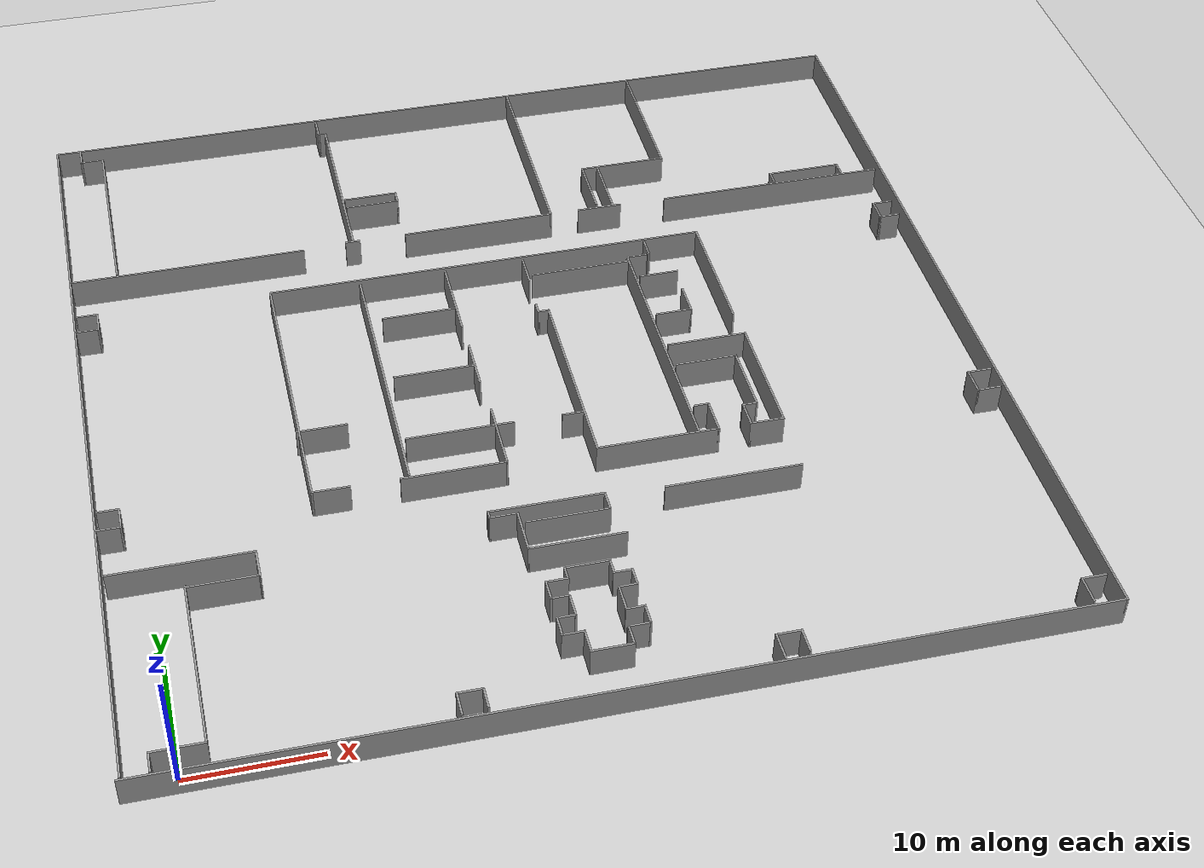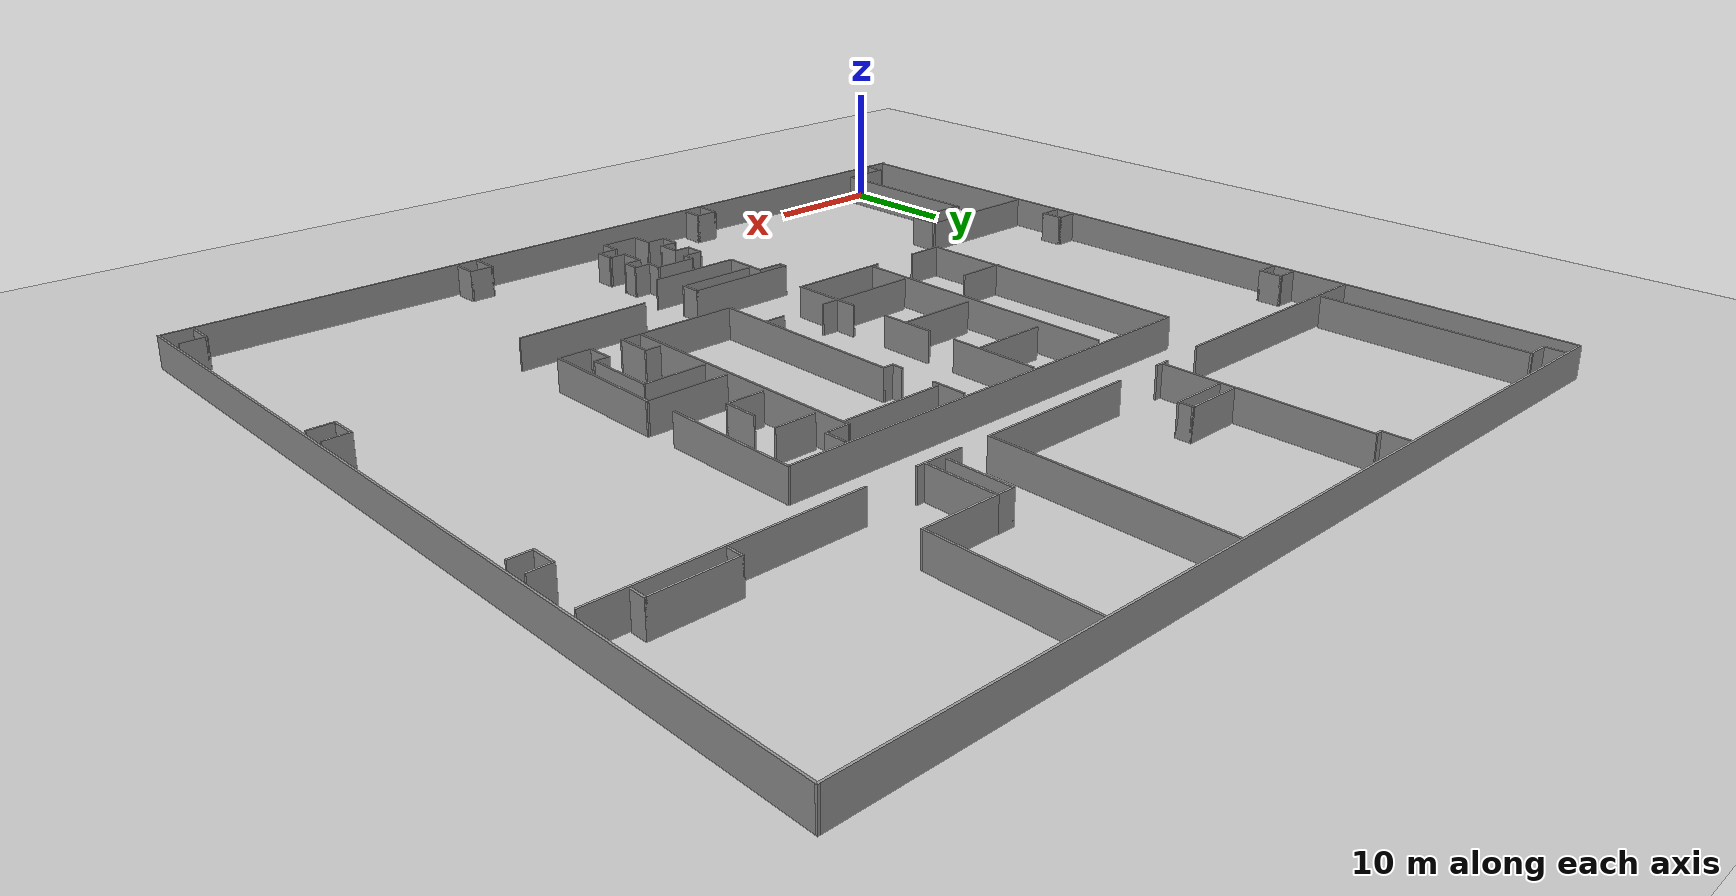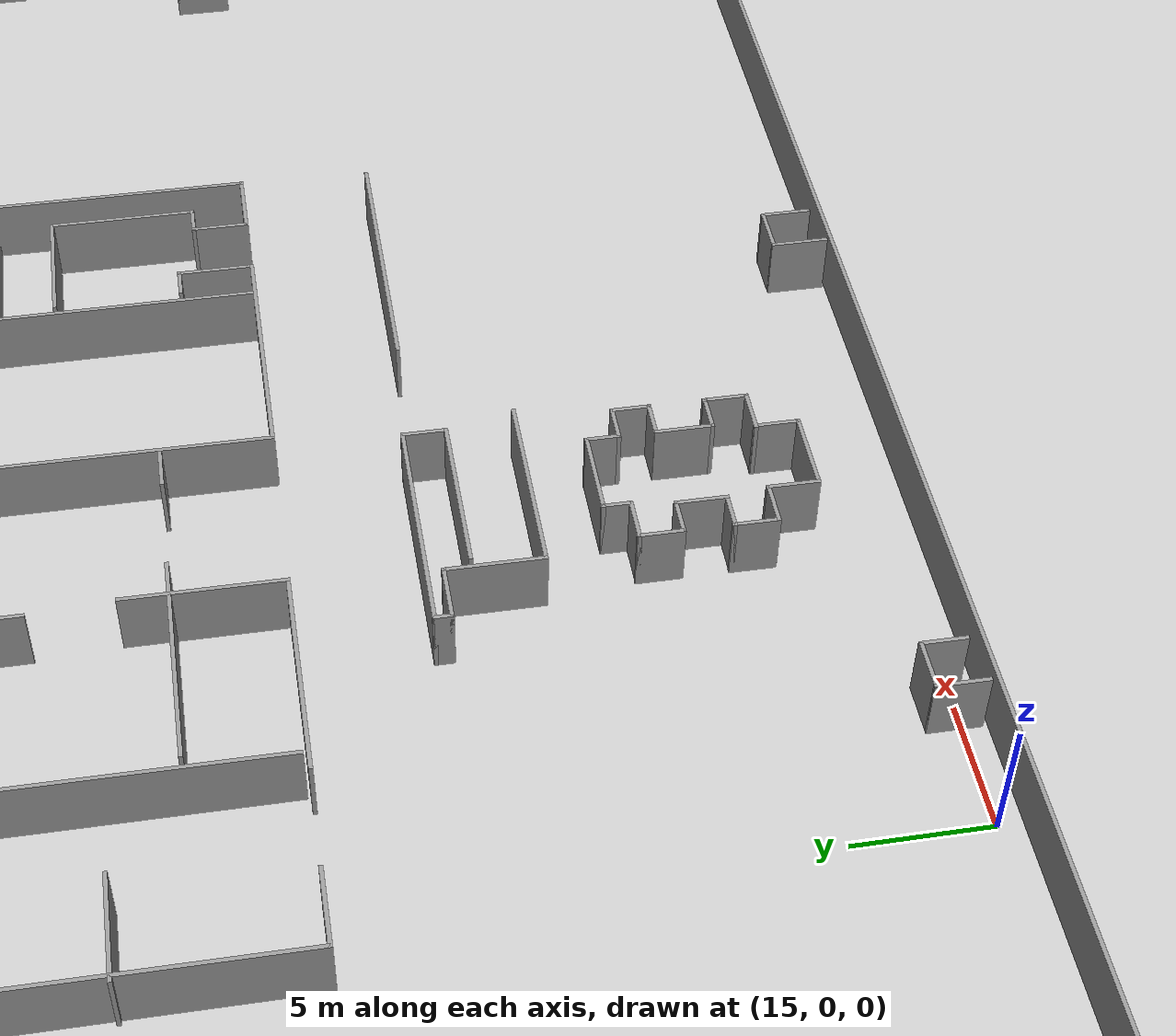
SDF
<sdf version="1.6">
 <world name="default">
  <light name="sun" type="directional">
   <pose>0 0 10 0 -0 0</pose>
   <diffuse>0.8 0.8 0.8 1</diffuse>
   <specular>0.1 0.1 0.1 1</specular>
   <attenuation>
    <range>1000</range>
    <constant>0.9</constant>
    <linear>0.01</linear>
    <quadratic>0.001</quadratic>
   </attenuation>
   <direction>-0.5 0.5 -1</direction>
  </light>
  <model name="ground_plane">
   <static>1</static>
   <link name="link">
    <collision name="collision">
     <geometry><plane><normal>0 0 1</normal><size>100 100</size></plane></geometry>
     <surface><friction><ode><mu>100</mu><mu2>50</mu2></ode></friction></surface>
    </collision>
    <visual name="visual">
     <cast_shadows>0</cast_shadows>
     <geometry><plane><normal>0 0 1</normal><size>100 100</size></plane></geometry>
     <material>
      <script><uri>file://media/materials/scripts/gazebo.material</uri><name>Gazebo/Grey</name></script>
     </material>
    </visual>
   </link>
  </model>
  <gravity>0 0 -9.8</gravity>
  <magnetic_field>6e-06 2.3e-05 -4.2e-05</magnetic_field>
  <atmosphere type="adiabatic"/>
  <physics name="default_physics" default="0" type="ode">
   <max_step_size>0.001</max_step_size>
   <real_time_factor>1</real_time_factor>
   <real_time_update_rate>1000</real_time_update_rate>
  </physics>
  <scene><ambient>0.4 0.4 0.4 1</ambient><background>0.7 0.7 0.7 1</background><shadows>1</shadows></scene>
  <spherical_coordinates>
   <surface_model>EARTH_WGS84</surface_model>
   <latitude_deg>0</latitude_deg>
   <longitude_deg>0</longitude_deg>
   <elevation>0</elevation>
   <heading_deg>0</heading_deg>
  </spherical_coordinates>
  <model name="chengdu_office_0">
   <link name="Wall_0">
    <pose>-2e-06 -34.675 0 0 -0 0</pose>
    <visual name="Wall_0_Visual">
     <pose>0 0 1.25 0 -0 0</pose>
     <geometry><box><size>71 0.15 2.5</size></box></geometry>
     <material>
      <script><uri>file://media/materials/scripts/gazebo.material</uri><name>Gazebo/Grey</name></script>
      <ambient>1 1 1 1</ambient>
      <diffuse>0.7 0.7 0.7 1</diffuse>
      <specular>0.01 0.01 0.01 1</specular>
      <emissive>0 0 0 1</emissive>
     </material>
    </visual>
    <collision name="Wall_0_Collision">
     <pose>0 0 1.25 0 -0 0</pose>
     <geometry><box><size>71 0.15 2.5</size></box></geometry>
     <surface>
      <friction>
       <ode><mu>1</mu><mu2>1</mu2><fdir1>0 0 0</fdir1><slip1>0</slip1><slip2>0</slip2></ode>
       <torsional>
        <coefficient>1</coefficient>
        <patch_radius>0</patch_radius>
        <surface_radius>0</surface_radius>
        <use_patch_radius>1</use_patch_radius>
        <ode><slip>0</slip></ode>
       </torsional>
      </friction>
      <bounce><restitution_coefficient>0</restitution_coefficient><threshold>1e+06</threshold></bounce>
      <contact>
       <collide_without_contact>0</collide_without_contact>
       <collide_without_contact_bitmask>1</collide_without_contact_bitmask>
       <collide_bitmask>1</collide_bitmask>
       <ode>
        <soft_cfm>0</soft_cfm>
        <soft_erp>0.2</soft_erp>
        <kp>1e+13</kp>
        <kd>1</kd>
        <max_vel>0.01</max_vel>
        <min_depth>0</min_depth>
       </ode>
       <bullet>
        <split_impulse>1</split_impulse>
        <split_impulse_penetration_threshold>-0.01</split_impulse_penetration_threshold>
        <soft_cfm>0</soft_cfm>
        <soft_erp>0.2</soft_erp>
        <kp>1e+13</kp>
        <kd>1</kd>
       </bullet>
      </contact>
     </surface>
    </collision>
   </link>
   <link name="Wall_1">
    <pose>35.425 0 0 0 -0 1.5708</pose>
    <visual name="Wall_1_Visual">
     <pose>0 0 1.25 0 -0 0</pose>
     <geometry><box><size>69.5 0.15 2.5</size></box></geometry>
     <material>
      <script><uri>file://media/materials/scripts/gazebo.material</uri><name>Gazebo/Grey</name></script>
      <ambient>1 1 1 1</ambient>
      <diffuse>0.7 0.7 0.7 1</diffuse>
      <specular>0.01 0.01 0.01 1</specular>
      <emissive>0 0 0 1</emissive>
     </material>
    </visual>
    <collision name="Wall_1_Collision">
     <pose>0 0 1.25 0 -0 0</pose>
     <geometry><box><size>69.5 0.15 2.5</size></box></geometry>
     <surface>
      <friction>
       <ode><mu>1</mu><mu2>1</mu2><fdir1>0 0 0</fdir1><slip1>0</slip1><slip2>0</slip2></ode>
       <torsional>
        <coefficient>1</coefficient>
        <patch_radius>0</patch_radius>
        <surface_radius>0</surface_radius>
        <use_patch_radius>1</use_patch_radius>
        <ode><slip>0</slip></ode>
       </torsional>
      </friction>
      <bounce><restitution_coefficient>0</restitution_coefficient><threshold>1e+06</threshold></bounce>
      <contact>
       <collide_without_contact>0</collide_without_contact>
       <collide_without_contact_bitmask>1</collide_without_contact_bitmask>
       <collide_bitmask>1</collide_bitmask>
       <ode>
        <soft_cfm>0</soft_cfm>
        <soft_erp>0.2</soft_erp>
        <kp>1e+13</kp>
        <kd>1</kd>
        <max_vel>0.01</max_vel>
        <min_depth>0</min_depth>
       </ode>
       <bullet>
        <split_impulse>1</split_impulse>
        <split_impulse_penetration_threshold>-0.01</split_impulse_penetration_threshold>
        <soft_cfm>0</soft_cfm>
        <soft_erp>0.2</soft_erp>
        <kp>1e+13</kp>
        <kd>1</kd>
       </bullet>
      </contact>
     </surface>
    </collision>
   </link>
   <link name="Wall_10">
    <pose>-23.9919 -17.7709 0 0 -0 1.5708</pose>
    <visual name="Wall_10_Visual">
     <pose>0 0 1.25 0 -0 0</pose>
     <geometry><box><size>2.5 0.15 2.5</size></box></geometry>
     <material>
      <script><uri>file://media/materials/scripts/gazebo.material</uri><name>Gazebo/Grey</name></script>
      <ambient>1 1 1 1</ambient>
      <diffuse>0.7 0.7 0.7 1</diffuse>
      <specular>0.01 0.01 0.01 1</specular>
      <emissive>0 0 0 1</emissive>
     </material>
    </visual>
    <collision name="Wall_10_Collision">
     <pose>0 0 1.25 0 -0 0</pose>
     <geometry><box><size>2.5 0.15 2.5</size></box></geometry>
     <surface>
      <friction>
       <ode><mu>1</mu><mu2>1</mu2><fdir1>0 0 0</fdir1><slip1>0</slip1><slip2>0</slip2></ode>
       <torsional>
        <coefficient>1</coefficient>
        <patch_radius>0</patch_radius>
        <surface_radius>0</surface_radius>
        <use_patch_radius>1</use_patch_radius>
        <ode><slip>0</slip></ode>
       </torsional>
      </friction>
      <bounce><restitution_coefficient>0</restitution_coefficient><threshold>1e+06</threshold></bounce>
      <contact>
       <collide_without_contact>0</collide_without_contact>
       <collide_without_contact_bitmask>1</collide_without_contact_bitmask>
       <collide_bitmask>1</collide_bitmask>
       <ode>
        <soft_cfm>0</soft_cfm>
        <soft_erp>0.2</soft_erp>
        <kp>1e+13</kp>
        <kd>1</kd>
        <max_vel>0.01</max_vel>
        <min_depth>0</min_depth>
       </ode>
       <bullet>
        <split_impulse>1</split_impulse>
        <split_impulse_penetration_threshold>-0.01</split_impulse_penetration_threshold>
        <soft_cfm>0</soft_cfm>
        <soft_erp>0.2</soft_erp>
        <kp>1e+13</kp>
        <kd>1</kd>
       </bullet>
      </contact>
     </surface>
    </collision>
   </link>
   <link name="Wall_100">
    <pose>14.2089 -1.63326 0 0 -0 3.14159</pose>
    <visual name="Wall_100_Visual">
     <pose>0 0 1.25 0 -0 0</pose>
     <geometry><box><size>6.5 0.15 2.5</size></box></geometry>
     <material>
      <script><uri>file://media/materials/scripts/gazebo.material</uri><name>Gazebo/Grey</name></script>
      <ambient>1 1 1 1</ambient>
      <diffuse>0.7 0.7 0.7 1</diffuse>
      <specular>0.01 0.01 0.01 1</specular>
      <emissive>0 0 0 1</emissive>
     </material>
    </visual>
    <collision name="Wall_100_Collision">
     <pose>0 0 1.25 0 -0 0</pose>
     <geometry><box><size>6.5 0.15 2.5</size></box></geometry>
     <surface>
      <friction>
       <ode><mu>1</mu><mu2>1</mu2><fdir1>0 0 0</fdir1><slip1>0</slip1><slip2>0</slip2></ode>
       <torsional>
        <coefficient>1</coefficient>
        <patch_radius>0</patch_radius>
        <surface_radius>0</surface_radius>
        <use_patch_radius>1</use_patch_radius>
        <ode><slip>0</slip></ode>
       </torsional>
      </friction>
      <bounce><restitution_coefficient>0</restitution_coefficient><threshold>1e+06</threshold></bounce>
      <contact>
       <collide_without_contact>0</collide_without_contact>
       <collide_without_contact_bitmask>1</collide_without_contact_bitmask>
       <collide_bitmask>1</collide_bitmask>
       <ode>
        <soft_cfm>0</soft_cfm>
        <soft_erp>0.2</soft_erp>
        <kp>1e+13</kp>
        <kd>1</kd>
        <max_vel>0.01</max_vel>
        <min_depth>0</min_depth>
       </ode>
       <bullet>
        <split_impulse>1</split_impulse>
        <split_impulse_penetration_threshold>-0.01</split_impulse_penetration_threshold>
        <soft_cfm>0</soft_cfm>
        <soft_erp>0.2</soft_erp>
        <kp>1e+13</kp>
        <kd>1</kd>
       </bullet>
      </contact>
     </surface>
    </collision>
   </link>
   <link name="Wall_102">
    <pose>12.5839 7.08674 0 0 -0 0</pose>
    <visual name="Wall_102_Visual">
     <pose>0 0 1.25 0 -0 0</pose>
     <geometry><box><size>3.25 0.15 2.5</size></box></geometry>
     <material>
      <script><uri>file://media/materials/scripts/gazebo.material</uri><name>Gazebo/Grey</name></script>
      <ambient>1 1 1 1</ambient>
      <diffuse>0.7 0.7 0.7 1</diffuse>
      <specular>0.01 0.01 0.01 1</specular>
      <emissive>0 0 0 1</emissive>
     </material>
    </visual>
    <collision name="Wall_102_Collision">
     <pose>0 0 1.25 0 -0 0</pose>
     <geometry><box><size>3.25 0.15 2.5</size></box></geometry>
     <surface>
      <friction>
       <ode><mu>1</mu><mu2>1</mu2><fdir1>0 0 0</fdir1><slip1>0</slip1><slip2>0</slip2></ode>
       <torsional>
        <coefficient>1</coefficient>
        <patch_radius>0</patch_radius>
        <surface_radius>0</surface_radius>
        <use_patch_radius>1</use_patch_radius>
        <ode><slip>0</slip></ode>
       </torsional>
      </friction>
      <bounce><restitution_coefficient>0</restitution_coefficient><threshold>1e+06</threshold></bounce>
      <contact>
       <collide_without_contact>0</collide_without_contact>
       <collide_without_contact_bitmask>1</collide_without_contact_bitmask>
       <collide_bitmask>1</collide_bitmask>
       <ode>
        <soft_cfm>0</soft_cfm>
        <soft_erp>0.2</soft_erp>
        <kp>1e+13</kp>
        <kd>1</kd>
        <max_vel>0.01</max_vel>
        <min_depth>0</min_depth>
       </ode>
       <bullet>
        <split_impulse>1</split_impulse>
        <split_impulse_penetration_threshold>-0.01</split_impulse_penetration_threshold>
        <soft_cfm>0</soft_cfm>
        <soft_erp>0.2</soft_erp>
        <kp>1e+13</kp>
        <kd>1</kd>
       </bullet>
      </contact>
     </surface>
    </collision>
   </link>
   <link name="Wall_104">
    <pose>13.9539 3.46674 0 0 0 -1.5708</pose>
    <visual name="Wall_104_Visual">
     <pose>0 0 1.25 0 -0 0</pose>
     <geometry><box><size>2.75 0.15 2.5</size></box></geometry>
     <material>
      <script><uri>file://media/materials/scripts/gazebo.material</uri><name>Gazebo/Grey</name></script>
      <ambient>1 1 1 1</ambient>
      <diffuse>0.7 0.7 0.7 1</diffuse>
      <specular>0.01 0.01 0.01 1</specular>
      <emissive>0 0 0 1</emissive>
     </material>
    </visual>
    <collision name="Wall_104_Collision">
     <pose>0 0 1.25 0 -0 0</pose>
     <geometry><box><size>2.75 0.15 2.5</size></box></geometry>
     <surface>
      <friction>
       <ode><mu>1</mu><mu2>1</mu2><fdir1>0 0 0</fdir1><slip1>0</slip1><slip2>0</slip2></ode>
       <torsional>
        <coefficient>1</coefficient>
        <patch_radius>0</patch_radius>
        <surface_radius>0</surface_radius>
        <use_patch_radius>1</use_patch_radius>
        <ode><slip>0</slip></ode>
       </torsional>
      </friction>
      <bounce><restitution_coefficient>0</restitution_coefficient><threshold>1e+06</threshold></bounce>
      <contact>
       <collide_without_contact>0</collide_without_contact>
       <collide_without_contact_bitmask>1</collide_without_contact_bitmask>
       <collide_bitmask>1</collide_bitmask>
       <ode>
        <soft_cfm>0</soft_cfm>
        <soft_erp>0.2</soft_erp>
        <kp>1e+13</kp>
        <kd>1</kd>
        <max_vel>0.01</max_vel>
        <min_depth>0</min_depth>
       </ode>
       <bullet>
        <split_impulse>1</split_impulse>
        <split_impulse_penetration_threshold>-0.01</split_impulse_penetration_threshold>
        <soft_cfm>0</soft_cfm>
        <soft_erp>0.2</soft_erp>
        <kp>1e+13</kp>
        <kd>1</kd>
       </bullet>
      </contact>
     </surface>
    </collision>
   </link>
   <link name="Wall_105">
    <pose>12.5289 2.16674 0 0 -0 3.14159</pose>
    <visual name="Wall_105_Visual">
     <pose>0 0 1.25 0 -0 0</pose>
     <geometry><box><size>3 0.15 2.5</size></box></geometry>
     <material>
      <script><uri>file://media/materials/scripts/gazebo.material</uri><name>Gazebo/Grey</name></script>
      <ambient>1 1 1 1</ambient>
      <diffuse>0.7 0.7 0.7 1</diffuse>
      <specular>0.01 0.01 0.01 1</specular>
      <emissive>0 0 0 1</emissive>
     </material>
    </visual>
    <collision name="Wall_105_Collision">
     <pose>0 0 1.25 0 -0 0</pose>
     <geometry><box><size>3 0.15 2.5</size></box></geometry>
     <surface>
      <friction>
       <ode><mu>1</mu><mu2>1</mu2><fdir1>0 0 0</fdir1><slip1>0</slip1><slip2>0</slip2></ode>
       <torsional>
        <coefficient>1</coefficient>
        <patch_radius>0</patch_radius>
        <surface_radius>0</surface_radius>
        <use_patch_radius>1</use_patch_radius>
        <ode><slip>0</slip></ode>
       </torsional>
      </friction>
      <bounce><restitution_coefficient>0</restitution_coefficient><threshold>1e+06</threshold></bounce>
      <contact>
       <collide_without_contact>0</collide_without_contact>
       <collide_without_contact_bitmask>1</collide_without_contact_bitmask>
       <collide_bitmask>1</collide_bitmask>
       <ode>
        <soft_cfm>0</soft_cfm>
        <soft_erp>0.2</soft_erp>
        <kp>1e+13</kp>
        <kd>1</kd>
        <max_vel>0.01</max_vel>
        <min_depth>0</min_depth>
       </ode>
       <bullet>
        <split_impulse>1</split_impulse>
        <split_impulse_penetration_threshold>-0.01</split_impulse_penetration_threshold>
        <soft_cfm>0</soft_cfm>
        <soft_erp>0.2</soft_erp>
        <kp>1e+13</kp>
        <kd>1</kd>
       </bullet>
      </contact>
     </surface>
    </collision>
   </link>
   <link name="Wall_11">
    <pose>-29.4169 -16.5959 0 0 -0 3.14159</pose>
    <visual name="Wall_11_Visual">
     <pose>0 0 1.25 0 -0 0</pose>
     <geometry><box><size>11 0.15 2.5</size></box></geometry>
     <material>
      <script><uri>file://media/materials/scripts/gazebo.material</uri><name>Gazebo/Grey</name></script>
      <ambient>1 1 1 1</ambient>
      <diffuse>0.7 0.7 0.7 1</diffuse>
      <specular>0.01 0.01 0.01 1</specular>
      <emissive>0 0 0 1</emissive>
     </material>
    </visual>
    <collision name="Wall_11_Collision">
     <pose>0 0 1.25 0 -0 0</pose>
     <geometry><box><size>11 0.15 2.5</size></box></geometry>
     <surface>
      <friction>
       <ode><mu>1</mu><mu2>1</mu2><fdir1>0 0 0</fdir1><slip1>0</slip1><slip2>0</slip2></ode>
       <torsional>
        <coefficient>1</coefficient>
        <patch_radius>0</patch_radius>
        <surface_radius>0</surface_radius>
        <use_patch_radius>1</use_patch_radius>
        <ode><slip>0</slip></ode>
       </torsional>
      </friction>
      <bounce><restitution_coefficient>0</restitution_coefficient><threshold>1e+06</threshold></bounce>
      <contact>
       <collide_without_contact>0</collide_without_contact>
       <collide_without_contact_bitmask>1</collide_without_contact_bitmask>
       <collide_bitmask>1</collide_bitmask>
       <ode>
        <soft_cfm>0</soft_cfm>
        <soft_erp>0.2</soft_erp>
        <kp>1e+13</kp>
        <kd>1</kd>
        <max_vel>0.01</max_vel>
        <min_depth>0</min_depth>
       </ode>
       <bullet>
        <split_impulse>1</split_impulse>
        <split_impulse_penetration_threshold>-0.01</split_impulse_penetration_threshold>
        <soft_cfm>0</soft_cfm>
        <soft_erp>0.2</soft_erp>
        <kp>1e+13</kp>
        <kd>1</kd>
       </bullet>
      </contact>
     </surface>
    </collision>
   </link>
   <link name="Wall_114">
    <pose>11.3778 9.72671 0 0 -0 0</pose>
    <visual name="Wall_114_Visual">
     <pose>0 0 1.25 0 -0 0</pose>
     <geometry><box><size>1.75 0.15 2.5</size></box></geometry>
     <material>
      <script><uri>file://media/materials/scripts/gazebo.material</uri><name>Gazebo/Grey</name></script>
      <ambient>1 1 1 1</ambient>
      <diffuse>0.7 0.7 0.7 1</diffuse>
      <specular>0.01 0.01 0.01 1</specular>
      <emissive>0 0 0 1</emissive>
     </material>
    </visual>
    <collision name="Wall_114_Collision">
     <pose>0 0 1.25 0 -0 0</pose>
     <geometry><box><size>1.75 0.15 2.5</size></box></geometry>
     <surface>
      <friction>
       <ode><mu>1</mu><mu2>1</mu2><fdir1>0 0 0</fdir1><slip1>0</slip1><slip2>0</slip2></ode>
       <torsional>
        <coefficient>1</coefficient>
        <patch_radius>0</patch_radius>
        <surface_radius>0</surface_radius>
        <use_patch_radius>1</use_patch_radius>
        <ode><slip>0</slip></ode>
       </torsional>
      </friction>
      <bounce><restitution_coefficient>0</restitution_coefficient><threshold>1e+06</threshold></bounce>
      <contact>
       <collide_without_contact>0</collide_without_contact>
       <collide_without_contact_bitmask>1</collide_without_contact_bitmask>
       <collide_bitmask>1</collide_bitmask>
       <ode>
        <soft_cfm>0</soft_cfm>
        <soft_erp>0.2</soft_erp>
        <kp>1e+13</kp>
        <kd>1</kd>
        <max_vel>0.01</max_vel>
        <min_depth>0</min_depth>
       </ode>
       <bullet>
        <split_impulse>1</split_impulse>
        <split_impulse_penetration_threshold>-0.01</split_impulse_penetration_threshold>
        <soft_cfm>0</soft_cfm>
        <soft_erp>0.2</soft_erp>
        <kp>1e+13</kp>
        <kd>1</kd>
       </bullet>
      </contact>
     </surface>
    </collision>
   </link>
   <link name="Wall_116">
    <pose>-12.3754 -33.4342 0 0 -0 1.5708</pose>
    <visual name="Wall_116_Visual">
     <pose>0 0 1.25 0 -0 0</pose>
     <geometry><box><size>2 0.15 2.5</size></box></geometry>
     <material>
      <script><uri>file://media/materials/scripts/gazebo.material</uri><name>Gazebo/Grey</name></script>
      <ambient>1 1 1 1</ambient>
      <diffuse>0.7 0.7 0.7 1</diffuse>
      <specular>0.01 0.01 0.01 1</specular>
      <emissive>0 0 0 1</emissive>
     </material>
    </visual>
    <collision name="Wall_116_Collision">
     <pose>0 0 1.25 0 -0 0</pose>
     <geometry><box><size>2 0.15 2.5</size></box></geometry>
     <surface>
      <friction>
       <ode><mu>1</mu><mu2>1</mu2><fdir1>0 0 0</fdir1><slip1>0</slip1><slip2>0</slip2></ode>
       <torsional>
        <coefficient>1</coefficient>
        <patch_radius>0</patch_radius>
        <surface_radius>0</surface_radius>
        <use_patch_radius>1</use_patch_radius>
        <ode><slip>0</slip></ode>
       </torsional>
      </friction>
      <bounce><restitution_coefficient>0</restitution_coefficient><threshold>1e+06</threshold></bounce>
      <contact>
       <collide_without_contact>0</collide_without_contact>
       <collide_without_contact_bitmask>1</collide_without_contact_bitmask>
       <collide_bitmask>1</collide_bitmask>
       <ode>
        <soft_cfm>0</soft_cfm>
        <soft_erp>0.2</soft_erp>
        <kp>1e+13</kp>
        <kd>1</kd>
        <max_vel>0.01</max_vel>
        <min_depth>0</min_depth>
       </ode>
       <bullet>
        <split_impulse>1</split_impulse>
        <split_impulse_penetration_threshold>-0.01</split_impulse_penetration_threshold>
        <soft_cfm>0</soft_cfm>
        <soft_erp>0.2</soft_erp>
        <kp>1e+13</kp>
        <kd>1</kd>
       </bullet>
      </contact>
     </surface>
    </collision>
   </link>
   <link name="Wall_117">
    <pose>-11.4504 -32.5092 0 0 -0 0</pose>
    <visual name="Wall_117_Visual">
     <pose>0 0 1.25 0 -0 0</pose>
     <geometry><box><size>2 0.15 2.5</size></box></geometry>
     <material>
      <script><uri>file://media/materials/scripts/gazebo.material</uri><name>Gazebo/Grey</name></script>
      <ambient>1 1 1 1</ambient>
      <diffuse>0.7 0.7 0.7 1</diffuse>
      <specular>0.01 0.01 0.01 1</specular>
      <emissive>0 0 0 1</emissive>
     </material>
    </visual>
    <collision name="Wall_117_Collision">
     <pose>0 0 1.25 0 -0 0</pose>
     <geometry><box><size>2 0.15 2.5</size></box></geometry>
     <surface>
      <friction>
       <ode><mu>1</mu><mu2>1</mu2><fdir1>0 0 0</fdir1><slip1>0</slip1><slip2>0</slip2></ode>
       <torsional>
        <coefficient>1</coefficient>
        <patch_radius>0</patch_radius>
        <surface_radius>0</surface_radius>
        <use_patch_radius>1</use_patch_radius>
        <ode><slip>0</slip></ode>
       </torsional>
      </friction>
      <bounce><restitution_coefficient>0</restitution_coefficient><threshold>1e+06</threshold></bounce>
      <contact>
       <collide_without_contact>0</collide_without_contact>
       <collide_without_contact_bitmask>1</collide_without_contact_bitmask>
       <collide_bitmask>1</collide_bitmask>
       <ode>
        <soft_cfm>0</soft_cfm>
        <soft_erp>0.2</soft_erp>
        <kp>1e+13</kp>
        <kd>1</kd>
        <max_vel>0.01</max_vel>
        <min_depth>0</min_depth>
       </ode>
       <bullet>
        <split_impulse>1</split_impulse>
        <split_impulse_penetration_threshold>-0.01</split_impulse_penetration_threshold>
        <soft_cfm>0</soft_cfm>
        <soft_erp>0.2</soft_erp>
        <kp>1e+13</kp>
        <kd>1</kd>
       </bullet>
      </contact>
     </surface>
    </collision>
   </link>
   <link name="Wall_118">
    <pose>-10.5254 -33.3092 0 0 0 -1.5708</pose>
    <visual name="Wall_118_Visual">
     <pose>0 0 1.25 0 -0 0</pose>
     <geometry><box><size>1.75 0.15 2.5</size></box></geometry>
     <material>
      <script><uri>file://media/materials/scripts/gazebo.material</uri><name>Gazebo/Grey</name></script>
      <ambient>1 1 1 1</ambient>
      <diffuse>0.7 0.7 0.7 1</diffuse>
      <specular>0.01 0.01 0.01 1</specular>
      <emissive>0 0 0 1</emissive>
     </material>
    </visual>
    <collision name="Wall_118_Collision">
     <pose>0 0 1.25 0 -0 0</pose>
     <geometry><box><size>1.75 0.15 2.5</size></box></geometry>
     <surface>
      <friction>
       <ode><mu>1</mu><mu2>1</mu2><fdir1>0 0 0</fdir1><slip1>0</slip1><slip2>0</slip2></ode>
       <torsional>
        <coefficient>1</coefficient>
        <patch_radius>0</patch_radius>
        <surface_radius>0</surface_radius>
        <use_patch_radius>1</use_patch_radius>
        <ode><slip>0</slip></ode>
       </torsional>
      </friction>
      <bounce><restitution_coefficient>0</restitution_coefficient><threshold>1e+06</threshold></bounce>
      <contact>
       <collide_without_contact>0</collide_without_contact>
       <collide_without_contact_bitmask>1</collide_without_contact_bitmask>
       <collide_bitmask>1</collide_bitmask>
       <ode>
        <soft_cfm>0</soft_cfm>
        <soft_erp>0.2</soft_erp>
        <kp>1e+13</kp>
        <kd>1</kd>
        <max_vel>0.01</max_vel>
        <min_depth>0</min_depth>
       </ode>
       <bullet>
        <split_impulse>1</split_impulse>
        <split_impulse_penetration_threshold>-0.01</split_impulse_penetration_threshold>
        <soft_cfm>0</soft_cfm>
        <soft_erp>0.2</soft_erp>
        <kp>1e+13</kp>
        <kd>1</kd>
       </bullet>
      </contact>
     </surface>
    </collision>
   </link>
   <link name="Wall_120">
    <pose>10.2646 -33.3892 0 0 -0 1.5708</pose>
    <visual name="Wall_120_Visual">
     <pose>0 0 1.25 0 -0 0</pose>
     <geometry><box><size>2.25 0.15 2.5</size></box></geometry>
     <material>
      <script><uri>file://media/materials/scripts/gazebo.material</uri><name>Gazebo/Grey</name></script>
      <ambient>1 1 1 1</ambient>
      <diffuse>0.7 0.7 0.7 1</diffuse>
      <specular>0.01 0.01 0.01 1</specular>
      <emissive>0 0 0 1</emissive>
     </material>
    </visual>
    <collision name="Wall_120_Collision">
     <pose>0 0 1.25 0 -0 0</pose>
     <geometry><box><size>2.25 0.15 2.5</size></box></geometry>
     <surface>
      <friction>
       <ode><mu>1</mu><mu2>1</mu2><fdir1>0 0 0</fdir1><slip1>0</slip1><slip2>0</slip2></ode>
       <torsional>
        <coefficient>1</coefficient>
        <patch_radius>0</patch_radius>
        <surface_radius>0</surface_radius>
        <use_patch_radius>1</use_patch_radius>
        <ode><slip>0</slip></ode>
       </torsional>
      </friction>
      <bounce><restitution_coefficient>0</restitution_coefficient><threshold>1e+06</threshold></bounce>
      <contact>
       <collide_without_contact>0</collide_without_contact>
       <collide_without_contact_bitmask>1</collide_without_contact_bitmask>
       <collide_bitmask>1</collide_bitmask>
       <ode>
        <soft_cfm>0</soft_cfm>
        <soft_erp>0.2</soft_erp>
        <kp>1e+13</kp>
        <kd>1</kd>
        <max_vel>0.01</max_vel>
        <min_depth>0</min_depth>
       </ode>
       <bullet>
        <split_impulse>1</split_impulse>
        <split_impulse_penetration_threshold>-0.01</split_impulse_penetration_threshold>
        <soft_cfm>0</soft_cfm>
        <soft_erp>0.2</soft_erp>
        <kp>1e+13</kp>
        <kd>1</kd>
       </bullet>
      </contact>
     </surface>
    </collision>
   </link>
   <link name="Wall_121">
    <pose>11.1896 -32.3392 0 0 -0 0</pose>
    <visual name="Wall_121_Visual">
     <pose>0 0 1.25 0 -0 0</pose>
     <geometry><box><size>2 0.15 2.5</size></box></geometry>
     <material>
      <script><uri>file://media/materials/scripts/gazebo.material</uri><name>Gazebo/Grey</name></script>
      <ambient>1 1 1 1</ambient>
      <diffuse>0.7 0.7 0.7 1</diffuse>
      <specular>0.01 0.01 0.01 1</specular>
      <emissive>0 0 0 1</emissive>
     </material>
    </visual>
    <collision name="Wall_121_Collision">
     <pose>0 0 1.25 0 -0 0</pose>
     <geometry><box><size>2 0.15 2.5</size></box></geometry>
     <surface>
      <friction>
       <ode><mu>1</mu><mu2>1</mu2><fdir1>0 0 0</fdir1><slip1>0</slip1><slip2>0</slip2></ode>
       <torsional>
        <coefficient>1</coefficient>
        <patch_radius>0</patch_radius>
        <surface_radius>0</surface_radius>
        <use_patch_radius>1</use_patch_radius>
        <ode><slip>0</slip></ode>
       </torsional>
      </friction>
      <bounce><restitution_coefficient>0</restitution_coefficient><threshold>1e+06</threshold></bounce>
      <contact>
       <collide_without_contact>0</collide_without_contact>
       <collide_without_contact_bitmask>1</collide_without_contact_bitmask>
       <collide_bitmask>1</collide_bitmask>
       <ode>
        <soft_cfm>0</soft_cfm>
        <soft_erp>0.2</soft_erp>
        <kp>1e+13</kp>
        <kd>1</kd>
        <max_vel>0.01</max_vel>
        <min_depth>0</min_depth>
       </ode>
       <bullet>
        <split_impulse>1</split_impulse>
        <split_impulse_penetration_threshold>-0.01</split_impulse_penetration_threshold>
        <soft_cfm>0</soft_cfm>
        <soft_erp>0.2</soft_erp>
        <kp>1e+13</kp>
        <kd>1</kd>
       </bullet>
      </contact>
     </surface>
    </collision>
   </link>
   <link name="Wall_122">
    <pose>12.1146 -33.2642 0 0 0 -1.5708</pose>
    <visual name="Wall_122_Visual">
     <pose>0 0 1.25 0 -0 0</pose>
     <geometry><box><size>2 0.15 2.5</size></box></geometry>
     <material>
      <script><uri>file://media/materials/scripts/gazebo.material</uri><name>Gazebo/Grey</name></script>
      <ambient>1 1 1 1</ambient>
      <diffuse>0.7 0.7 0.7 1</diffuse>
      <specular>0.01 0.01 0.01 1</specular>
      <emissive>0 0 0 1</emissive>
     </material>
    </visual>
    <collision name="Wall_122_Collision">
     <pose>0 0 1.25 0 -0 0</pose>
     <geometry><box><size>2 0.15 2.5</size></box></geometry>
     <surface>
      <friction>
       <ode><mu>1</mu><mu2>1</mu2><fdir1>0 0 0</fdir1><slip1>0</slip1><slip2>0</slip2></ode>
       <torsional>
        <coefficient>1</coefficient>
        <patch_radius>0</patch_radius>
        <surface_radius>0</surface_radius>
        <use_patch_radius>1</use_patch_radius>
        <ode><slip>0</slip></ode>
       </torsional>
      </friction>
      <bounce><restitution_coefficient>0</restitution_coefficient><threshold>1e+06</threshold></bounce>
      <contact>
       <collide_without_contact>0</collide_without_contact>
       <collide_without_contact_bitmask>1</collide_without_contact_bitmask>
       <collide_bitmask>1</collide_bitmask>
       <ode>
        <soft_cfm>0</soft_cfm>
        <soft_erp>0.2</soft_erp>
        <kp>1e+13</kp>
        <kd>1</kd>
        <max_vel>0.01</max_vel>
        <min_depth>0</min_depth>
       </ode>
       <bullet>
        <split_impulse>1</split_impulse>
        <split_impulse_penetration_threshold>-0.01</split_impulse_penetration_threshold>
        <soft_cfm>0</soft_cfm>
        <soft_erp>0.2</soft_erp>
        <kp>1e+13</kp>
        <kd>1</kd>
       </bullet>
      </contact>
     </surface>
    </collision>
   </link>
   <link name="Wall_124">
    <pose>33.0646 -33.2292 0 0 -0 1.5708</pose>
    <visual name="Wall_124_Visual">
     <pose>0 0 1.25 0 -0 0</pose>
     <geometry><box><size>2.25 0.15 2.5</size></box></geometry>
     <material>
      <script><uri>file://media/materials/scripts/gazebo.material</uri><name>Gazebo/Grey</name></script>
      <ambient>1 1 1 1</ambient>
      <diffuse>0.7 0.7 0.7 1</diffuse>
      <specular>0.01 0.01 0.01 1</specular>
      <emissive>0 0 0 1</emissive>
     </material>
    </visual>
    <collision name="Wall_124_Collision">
     <pose>0 0 1.25 0 -0 0</pose>
     <geometry><box><size>2.25 0.15 2.5</size></box></geometry>
     <surface>
      <friction>
       <ode><mu>1</mu><mu2>1</mu2><fdir1>0 0 0</fdir1><slip1>0</slip1><slip2>0</slip2></ode>
       <torsional>
        <coefficient>1</coefficient>
        <patch_radius>0</patch_radius>
        <surface_radius>0</surface_radius>
        <use_patch_radius>1</use_patch_radius>
        <ode><slip>0</slip></ode>
       </torsional>
      </friction>
      <bounce><restitution_coefficient>0</restitution_coefficient><threshold>1e+06</threshold></bounce>
      <contact>
       <collide_without_contact>0</collide_without_contact>
       <collide_without_contact_bitmask>1</collide_without_contact_bitmask>
       <collide_bitmask>1</collide_bitmask>
       <ode>
        <soft_cfm>0</soft_cfm>
        <soft_erp>0.2</soft_erp>
        <kp>1e+13</kp>
        <kd>1</kd>
        <max_vel>0.01</max_vel>
        <min_depth>0</min_depth>
       </ode>
       <bullet>
        <split_impulse>1</split_impulse>
        <split_impulse_penetration_threshold>-0.01</split_impulse_penetration_threshold>
        <soft_cfm>0</soft_cfm>
        <soft_erp>0.2</soft_erp>
        <kp>1e+13</kp>
        <kd>1</kd>
       </bullet>
      </contact>
     </surface>
    </collision>
   </link>
   <link name="Wall_125">
    <pose>33.9896 -32.1792 0 0 -0 0</pose>
    <visual name="Wall_125_Visual">
     <pose>0 0 1.25 0 -0 0</pose>
     <geometry><box><size>2 0.15 2.5</size></box></geometry>
     <material>
      <script><uri>file://media/materials/scripts/gazebo.material</uri><name>Gazebo/Grey</name></script>
      <ambient>1 1 1 1</ambient>
      <diffuse>0.7 0.7 0.7 1</diffuse>
      <specular>0.01 0.01 0.01 1</specular>
      <emissive>0 0 0 1</emissive>
     </material>
    </visual>
    <collision name="Wall_125_Collision">
     <pose>0 0 1.25 0 -0 0</pose>
     <geometry><box><size>2 0.15 2.5</size></box></geometry>
     <surface>
      <friction>
       <ode><mu>1</mu><mu2>1</mu2><fdir1>0 0 0</fdir1><slip1>0</slip1><slip2>0</slip2></ode>
       <torsional>
        <coefficient>1</coefficient>
        <patch_radius>0</patch_radius>
        <surface_radius>0</surface_radius>
        <use_patch_radius>1</use_patch_radius>
        <ode><slip>0</slip></ode>
       </torsional>
      </friction>
      <bounce><restitution_coefficient>0</restitution_coefficient><threshold>1e+06</threshold></bounce>
      <contact>
       <collide_without_contact>0</collide_without_contact>
       <collide_without_contact_bitmask>1</collide_without_contact_bitmask>
       <collide_bitmask>1</collide_bitmask>
       <ode>
        <soft_cfm>0</soft_cfm>
        <soft_erp>0.2</soft_erp>
        <kp>1e+13</kp>
        <kd>1</kd>
        <max_vel>0.01</max_vel>
        <min_depth>0</min_depth>
       </ode>
       <bullet>
        <split_impulse>1</split_impulse>
        <split_impulse_penetration_threshold>-0.01</split_impulse_penetration_threshold>
        <soft_cfm>0</soft_cfm>
        <soft_erp>0.2</soft_erp>
        <kp>1e+13</kp>
        <kd>1</kd>
       </bullet>
      </contact>
     </surface>
    </collision>
   </link>
   <link name="Wall_127">
    <pose>-2.42216 -16.465 0 0 -0 0</pose>
    <visual name="Wall_127_Visual">
     <pose>0 0 1.25 0 -0 0</pose>
     <geometry><box><size>9 0.15 2.5</size></box></geometry>
     <material>
      <script><uri>file://media/materials/scripts/gazebo.material</uri><name>Gazebo/Grey</name></script>
      <ambient>1 1 1 1</ambient>
      <diffuse>0.7 0.7 0.7 1</diffuse>
      <specular>0.01 0.01 0.01 1</specular>
      <emissive>0 0 0 1</emissive>
     </material>
    </visual>
    <collision name="Wall_127_Collision">
     <pose>0 0 1.25 0 -0 0</pose>
     <geometry><box><size>9 0.15 2.5</size></box></geometry>
     <surface>
      <friction>
       <ode><mu>1</mu><mu2>1</mu2><fdir1>0 0 0</fdir1><slip1>0</slip1><slip2>0</slip2></ode>
       <torsional>
        <coefficient>1</coefficient>
        <patch_radius>0</patch_radius>
        <surface_radius>0</surface_radius>
        <use_patch_radius>1</use_patch_radius>
        <ode><slip>0</slip></ode>
       </torsional>
      </friction>
      <bounce><restitution_coefficient>0</restitution_coefficient><threshold>1e+06</threshold></bounce>
      <contact>
       <collide_without_contact>0</collide_without_contact>
       <collide_without_contact_bitmask>1</collide_without_contact_bitmask>
       <collide_bitmask>1</collide_bitmask>
       <ode>
        <soft_cfm>0</soft_cfm>
        <soft_erp>0.2</soft_erp>
        <kp>1e+13</kp>
        <kd>1</kd>
        <max_vel>0.01</max_vel>
        <min_depth>0</min_depth>
       </ode>
       <bullet>
        <split_impulse>1</split_impulse>
        <split_impulse_penetration_threshold>-0.01</split_impulse_penetration_threshold>
        <soft_cfm>0</soft_cfm>
        <soft_erp>0.2</soft_erp>
        <kp>1e+13</kp>
        <kd>1</kd>
       </bullet>
      </contact>
     </surface>
    </collision>
   </link>
   <link name="Wall_128">
    <pose>2.00284 -17.265 0 0 0 -1.5708</pose>
    <visual name="Wall_128_Visual">
     <pose>0 0 1.25 0 -0 0</pose>
     <geometry><box><size>1.75 0.15 2.5</size></box></geometry>
     <material>
      <script><uri>file://media/materials/scripts/gazebo.material</uri><name>Gazebo/Grey</name></script>
      <ambient>1 1 1 1</ambient>
      <diffuse>0.7 0.7 0.7 1</diffuse>
      <specular>0.01 0.01 0.01 1</specular>
      <emissive>0 0 0 1</emissive>
     </material>
    </visual>
    <collision name="Wall_128_Collision">
     <pose>0 0 1.25 0 -0 0</pose>
     <geometry><box><size>1.75 0.15 2.5</size></box></geometry>
     <surface>
      <friction>
       <ode><mu>1</mu><mu2>1</mu2><fdir1>0 0 0</fdir1><slip1>0</slip1><slip2>0</slip2></ode>
       <torsional>
        <coefficient>1</coefficient>
        <patch_radius>0</patch_radius>
        <surface_radius>0</surface_radius>
        <use_patch_radius>1</use_patch_radius>
        <ode><slip>0</slip></ode>
       </torsional>
      </friction>
      <bounce><restitution_coefficient>0</restitution_coefficient><threshold>1e+06</threshold></bounce>
      <contact>
       <collide_without_contact>0</collide_without_contact>
       <collide_without_contact_bitmask>1</collide_without_contact_bitmask>
       <collide_bitmask>1</collide_bitmask>
       <ode>
        <soft_cfm>0</soft_cfm>
        <soft_erp>0.2</soft_erp>
        <kp>1e+13</kp>
        <kd>1</kd>
        <max_vel>0.01</max_vel>
        <min_depth>0</min_depth>
       </ode>
       <bullet>
        <split_impulse>1</split_impulse>
        <split_impulse_penetration_threshold>-0.01</split_impulse_penetration_threshold>
        <soft_cfm>0</soft_cfm>
        <soft_erp>0.2</soft_erp>
        <kp>1e+13</kp>
        <kd>1</kd>
       </bullet>
      </contact>
     </surface>
    </collision>
   </link>
   <link name="Wall_129">
    <pose>-1.17216 -18.065 0 0 -0 3.14159</pose>
    <visual name="Wall_129_Visual">
     <pose>0 0 1.25 0 -0 0</pose>
     <geometry><box><size>6.5 0.15 2.5</size></box></geometry>
     <material>
      <script><uri>file://media/materials/scripts/gazebo.material</uri><name>Gazebo/Grey</name></script>
      <ambient>1 1 1 1</ambient>
      <diffuse>0.7 0.7 0.7 1</diffuse>
      <specular>0.01 0.01 0.01 1</specular>
      <emissive>0 0 0 1</emissive>
     </material>
    </visual>
    <collision name="Wall_129_Collision">
     <pose>0 0 1.25 0 -0 0</pose>
     <geometry><box><size>6.5 0.15 2.5</size></box></geometry>
     <surface>
      <friction>
       <ode><mu>1</mu><mu2>1</mu2><fdir1>0 0 0</fdir1><slip1>0</slip1><slip2>0</slip2></ode>
       <torsional>
        <coefficient>1</coefficient>
        <patch_radius>0</patch_radius>
        <surface_radius>0</surface_radius>
        <use_patch_radius>1</use_patch_radius>
        <ode><slip>0</slip></ode>
       </torsional>
      </friction>
      <bounce><restitution_coefficient>0</restitution_coefficient><threshold>1e+06</threshold></bounce>
      <contact>
       <collide_without_contact>0</collide_without_contact>
       <collide_without_contact_bitmask>1</collide_without_contact_bitmask>
       <collide_bitmask>1</collide_bitmask>
       <ode>
        <soft_cfm>0</soft_cfm>
        <soft_erp>0.2</soft_erp>
        <kp>1e+13</kp>
        <kd>1</kd>
        <max_vel>0.01</max_vel>
        <min_depth>0</min_depth>
       </ode>
       <bullet>
        <split_impulse>1</split_impulse>
        <split_impulse_penetration_threshold>-0.01</split_impulse_penetration_threshold>
        <soft_cfm>0</soft_cfm>
        <soft_erp>0.2</soft_erp>
        <kp>1e+13</kp>
        <kd>1</kd>
       </bullet>
      </contact>
     </surface>
    </collision>
   </link>
   <link name="Wall_13">
    <pose>-34.2261 -12.0538 0 0 -0 0</pose>
    <visual name="Wall_13_Visual">
     <pose>0 0 1.25 0 -0 0</pose>
     <geometry><box><size>2 0.15 2.5</size></box></geometry>
     <material>
      <script><uri>file://media/materials/scripts/gazebo.material</uri><name>Gazebo/Grey</name></script>
      <ambient>1 1 1 1</ambient>
      <diffuse>0.7 0.7 0.7 1</diffuse>
      <specular>0.01 0.01 0.01 1</specular>
      <emissive>0 0 0 1</emissive>
     </material>
    </visual>
    <collision name="Wall_13_Collision">
     <pose>0 0 1.25 0 -0 0</pose>
     <geometry><box><size>2 0.15 2.5</size></box></geometry>
     <surface>
      <friction>
       <ode><mu>1</mu><mu2>1</mu2><fdir1>0 0 0</fdir1><slip1>0</slip1><slip2>0</slip2></ode>
       <torsional>
        <coefficient>1</coefficient>
        <patch_radius>0</patch_radius>
        <surface_radius>0</surface_radius>
        <use_patch_radius>1</use_patch_radius>
        <ode><slip>0</slip></ode>
       </torsional>
      </friction>
      <bounce><restitution_coefficient>0</restitution_coefficient><threshold>1e+06</threshold></bounce>
      <contact>
       <collide_without_contact>0</collide_without_contact>
       <collide_without_contact_bitmask>1</collide_without_contact_bitmask>
       <collide_bitmask>1</collide_bitmask>
       <ode>
        <soft_cfm>0</soft_cfm>
        <soft_erp>0.2</soft_erp>
        <kp>1e+13</kp>
        <kd>1</kd>
        <max_vel>0.01</max_vel>
        <min_depth>0</min_depth>
       </ode>
       <bullet>
        <split_impulse>1</split_impulse>
        <split_impulse_penetration_threshold>-0.01</split_impulse_penetration_threshold>
        <soft_cfm>0</soft_cfm>
        <soft_erp>0.2</soft_erp>
        <kp>1e+13</kp>
        <kd>1</kd>
       </bullet>
      </contact>
     </surface>
    </collision>
   </link>
   <link name="Wall_131">
    <pose>-6.84716 -16.765 0 0 0 -1.5708</pose>
    <visual name="Wall_131_Visual">
     <pose>0 0 1.25 0 -0 0</pose>
     <geometry><box><size>0.75 0.15 2.5</size></box></geometry>
     <material>
      <script><uri>file://media/materials/scripts/gazebo.material</uri><name>Gazebo/Grey</name></script>
      <ambient>1 1 1 1</ambient>
      <diffuse>0.7 0.7 0.7 1</diffuse>
      <specular>0.01 0.01 0.01 1</specular>
      <emissive>0 0 0 1</emissive>
     </material>
    </visual>
    <collision name="Wall_131_Collision">
     <pose>0 0 1.25 0 -0 0</pose>
     <geometry><box><size>0.75 0.15 2.5</size></box></geometry>
     <surface>
      <friction>
       <ode><mu>1</mu><mu2>1</mu2><fdir1>0 0 0</fdir1><slip1>0</slip1><slip2>0</slip2></ode>
       <torsional>
        <coefficient>1</coefficient>
        <patch_radius>0</patch_radius>
        <surface_radius>0</surface_radius>
        <use_patch_radius>1</use_patch_radius>
        <ode><slip>0</slip></ode>
       </torsional>
      </friction>
      <bounce><restitution_coefficient>0</restitution_coefficient><threshold>1e+06</threshold></bounce>
      <contact>
       <collide_without_contact>0</collide_without_contact>
       <collide_without_contact_bitmask>1</collide_without_contact_bitmask>
       <collide_bitmask>1</collide_bitmask>
       <ode>
        <soft_cfm>0</soft_cfm>
        <soft_erp>0.2</soft_erp>
        <kp>1e+13</kp>
        <kd>1</kd>
        <max_vel>0.01</max_vel>
        <min_depth>0</min_depth>
       </ode>
       <bullet>
        <split_impulse>1</split_impulse>
        <split_impulse_penetration_threshold>-0.01</split_impulse_penetration_threshold>
        <soft_cfm>0</soft_cfm>
        <soft_erp>0.2</soft_erp>
        <kp>1e+13</kp>
        <kd>1</kd>
       </bullet>
      </contact>
     </surface>
    </collision>
   </link>
   <link name="Wall_132">
    <pose>-5.79716 -17.065 0 0 -0 0</pose>
    <visual name="Wall_132_Visual">
     <pose>0 0 1.25 0 -0 0</pose>
     <geometry><box><size>2.25 0.15 2.5</size></box></geometry>
     <material>
      <script><uri>file://media/materials/scripts/gazebo.material</uri><name>Gazebo/Grey</name></script>
      <ambient>1 1 1 1</ambient>
      <diffuse>0.7 0.7 0.7 1</diffuse>
      <specular>0.01 0.01 0.01 1</specular>
      <emissive>0 0 0 1</emissive>
     </material>
    </visual>
    <collision name="Wall_132_Collision">
     <pose>0 0 1.25 0 -0 0</pose>
     <geometry><box><size>2.25 0.15 2.5</size></box></geometry>
     <surface>
      <friction>
       <ode><mu>1</mu><mu2>1</mu2><fdir1>0 0 0</fdir1><slip1>0</slip1><slip2>0</slip2></ode>
       <torsional>
        <coefficient>1</coefficient>
        <patch_radius>0</patch_radius>
        <surface_radius>0</surface_radius>
        <use_patch_radius>1</use_patch_radius>
        <ode><slip>0</slip></ode>
       </torsional>
      </friction>
      <bounce><restitution_coefficient>0</restitution_coefficient><threshold>1e+06</threshold></bounce>
      <contact>
       <collide_without_contact>0</collide_without_contact>
       <collide_without_contact_bitmask>1</collide_without_contact_bitmask>
       <collide_bitmask>1</collide_bitmask>
       <ode>
        <soft_cfm>0</soft_cfm>
        <soft_erp>0.2</soft_erp>
        <kp>1e+13</kp>
        <kd>1</kd>
        <max_vel>0.01</max_vel>
        <min_depth>0</min_depth>
       </ode>
       <bullet>
        <split_impulse>1</split_impulse>
        <split_impulse_penetration_threshold>-0.01</split_impulse_penetration_threshold>
        <soft_cfm>0</soft_cfm>
        <soft_erp>0.2</soft_erp>
        <kp>1e+13</kp>
        <kd>1</kd>
       </bullet>
      </contact>
     </surface>
    </collision>
   </link>
   <link name="Wall_133">
    <pose>-4.74716 -18.865 0 0 0 -1.5708</pose>
    <visual name="Wall_133_Visual">
     <pose>0 0 1.25 0 -0 0</pose>
     <geometry><box><size>3.75 0.15 2.5</size></box></geometry>
     <material>
      <script><uri>file://media/materials/scripts/gazebo.material</uri><name>Gazebo/Grey</name></script>
      <ambient>1 1 1 1</ambient>
      <diffuse>0.7 0.7 0.7 1</diffuse>
      <specular>0.01 0.01 0.01 1</specular>
      <emissive>0 0 0 1</emissive>
     </material>
    </visual>
    <collision name="Wall_133_Collision">
     <pose>0 0 1.25 0 -0 0</pose>
     <geometry><box><size>3.75 0.15 2.5</size></box></geometry>
     <surface>
      <friction>
       <ode><mu>1</mu><mu2>1</mu2><fdir1>0 0 0</fdir1><slip1>0</slip1><slip2>0</slip2></ode>
       <torsional>
        <coefficient>1</coefficient>
        <patch_radius>0</patch_radius>
        <surface_radius>0</surface_radius>
        <use_patch_radius>1</use_patch_radius>
        <ode><slip>0</slip></ode>
       </torsional>
      </friction>
      <bounce><restitution_coefficient>0</restitution_coefficient><threshold>1e+06</threshold></bounce>
      <contact>
       <collide_without_contact>0</collide_without_contact>
       <collide_without_contact_bitmask>1</collide_without_contact_bitmask>
       <collide_bitmask>1</collide_bitmask>
       <ode>
        <soft_cfm>0</soft_cfm>
        <soft_erp>0.2</soft_erp>
        <kp>1e+13</kp>
        <kd>1</kd>
        <max_vel>0.01</max_vel>
        <min_depth>0</min_depth>
       </ode>
       <bullet>
        <split_impulse>1</split_impulse>
        <split_impulse_penetration_threshold>-0.01</split_impulse_penetration_threshold>
        <soft_cfm>0</soft_cfm>
        <soft_erp>0.2</soft_erp>
        <kp>1e+13</kp>
        <kd>1</kd>
       </bullet>
      </contact>
     </surface>
    </collision>
   </link>
   <link name="Wall_134">
    <pose>-1.07216 -20.665 0 0 -0 0</pose>
    <visual name="Wall_134_Visual">
     <pose>0 0 1.25 0 -0 0</pose>
     <geometry><box><size>7.5 0.15 2.5</size></box></geometry>
     <material>
      <script><uri>file://media/materials/scripts/gazebo.material</uri><name>Gazebo/Grey</name></script>
      <ambient>1 1 1 1</ambient>
      <diffuse>0.7 0.7 0.7 1</diffuse>
      <specular>0.01 0.01 0.01 1</specular>
      <emissive>0 0 0 1</emissive>
     </material>
    </visual>
    <collision name="Wall_134_Collision">
     <pose>0 0 1.25 0 -0 0</pose>
     <geometry><box><size>7.5 0.15 2.5</size></box></geometry>
     <surface>
      <friction>
       <ode><mu>1</mu><mu2>1</mu2><fdir1>0 0 0</fdir1><slip1>0</slip1><slip2>0</slip2></ode>
       <torsional>
        <coefficient>1</coefficient>
        <patch_radius>0</patch_radius>
        <surface_radius>0</surface_radius>
        <use_patch_radius>1</use_patch_radius>
        <ode><slip>0</slip></ode>
       </torsional>
      </friction>
      <bounce><restitution_coefficient>0</restitution_coefficient><threshold>1e+06</threshold></bounce>
      <contact>
       <collide_without_contact>0</collide_without_contact>
       <collide_without_contact_bitmask>1</collide_without_contact_bitmask>
       <collide_bitmask>1</collide_bitmask>
       <ode>
        <soft_cfm>0</soft_cfm>
        <soft_erp>0.2</soft_erp>
        <kp>1e+13</kp>
        <kd>1</kd>
        <max_vel>0.01</max_vel>
        <min_depth>0</min_depth>
       </ode>
       <bullet>
        <split_impulse>1</split_impulse>
        <split_impulse_penetration_threshold>-0.01</split_impulse_penetration_threshold>
        <soft_cfm>0</soft_cfm>
        <soft_erp>0.2</soft_erp>
        <kp>1e+13</kp>
        <kd>1</kd>
       </bullet>
      </contact>
     </surface>
    </collision>
   </link>
   <link name="Wall_136">
    <pose>11.902 -16.8434 0 0 -0 0</pose>
    <visual name="Wall_136_Visual">
     <pose>0 0 1.25 0 -0 0</pose>
     <geometry><box><size>10.75 0.15 2.5</size></box></geometry>
     <material>
      <script><uri>file://media/materials/scripts/gazebo.material</uri><name>Gazebo/Grey</name></script>
      <ambient>1 1 1 1</ambient>
      <diffuse>0.7 0.7 0.7 1</diffuse>
      <specular>0.01 0.01 0.01 1</specular>
      <emissive>0 0 0 1</emissive>
     </material>
    </visual>
    <collision name="Wall_136_Collision">
     <pose>0 0 1.25 0 -0 0</pose>
     <geometry><box><size>10.75 0.15 2.5</size></box></geometry>
     <surface>
      <friction>
       <ode><mu>1</mu><mu2>1</mu2><fdir1>0 0 0</fdir1><slip1>0</slip1><slip2>0</slip2></ode>
       <torsional>
        <coefficient>1</coefficient>
        <patch_radius>0</patch_radius>
        <surface_radius>0</surface_radius>
        <use_patch_radius>1</use_patch_radius>
        <ode><slip>0</slip></ode>
       </torsional>
      </friction>
      <bounce><restitution_coefficient>0</restitution_coefficient><threshold>1e+06</threshold></bounce>
      <contact>
       <collide_without_contact>0</collide_without_contact>
       <collide_without_contact_bitmask>1</collide_without_contact_bitmask>
       <collide_bitmask>1</collide_bitmask>
       <ode>
        <soft_cfm>0</soft_cfm>
        <soft_erp>0.2</soft_erp>
        <kp>1e+13</kp>
        <kd>1</kd>
        <max_vel>0.01</max_vel>
        <min_depth>0</min_depth>
       </ode>
       <bullet>
        <split_impulse>1</split_impulse>
        <split_impulse_penetration_threshold>-0.01</split_impulse_penetration_threshold>
        <soft_cfm>0</soft_cfm>
        <soft_erp>0.2</soft_erp>
        <kp>1e+13</kp>
        <kd>1</kd>
       </bullet>
      </contact>
     </surface>
    </collision>
   </link>
   <link name="Wall_138">
    <pose>34.1169 -9.96068 0 0 -0 3.14159</pose>
    <visual name="Wall_138_Visual">
     <pose>0 0 1.25 0 -0 0</pose>
     <geometry><box><size>2 0.15 2.5</size></box></geometry>
     <material>
      <script><uri>file://media/materials/scripts/gazebo.material</uri><name>Gazebo/Grey</name></script>
      <ambient>1 1 1 1</ambient>
      <diffuse>0.7 0.7 0.7 1</diffuse>
      <specular>0.01 0.01 0.01 1</specular>
      <emissive>0 0 0 1</emissive>
     </material>
    </visual>
    <collision name="Wall_138_Collision">
     <pose>0 0 1.25 0 -0 0</pose>
     <geometry><box><size>2 0.15 2.5</size></box></geometry>
     <surface>
      <friction>
       <ode><mu>1</mu><mu2>1</mu2><fdir1>0 0 0</fdir1><slip1>0</slip1><slip2>0</slip2></ode>
       <torsional>
        <coefficient>1</coefficient>
        <patch_radius>0</patch_radius>
        <surface_radius>0</surface_radius>
        <use_patch_radius>1</use_patch_radius>
        <ode><slip>0</slip></ode>
       </torsional>
      </friction>
      <bounce><restitution_coefficient>0</restitution_coefficient><threshold>1e+06</threshold></bounce>
      <contact>
       <collide_without_contact>0</collide_without_contact>
       <collide_without_contact_bitmask>1</collide_without_contact_bitmask>
       <collide_bitmask>1</collide_bitmask>
       <ode>
        <soft_cfm>0</soft_cfm>
        <soft_erp>0.2</soft_erp>
        <kp>1e+13</kp>
        <kd>1</kd>
        <max_vel>0.01</max_vel>
        <min_depth>0</min_depth>
       </ode>
       <bullet>
        <split_impulse>1</split_impulse>
        <split_impulse_penetration_threshold>-0.01</split_impulse_penetration_threshold>
        <soft_cfm>0</soft_cfm>
        <soft_erp>0.2</soft_erp>
        <kp>1e+13</kp>
        <kd>1</kd>
       </bullet>
      </contact>
     </surface>
    </collision>
   </link>
   <link name="Wall_139">
    <pose>33.1919 -11.0107 0 0 0 -1.5708</pose>
    <visual name="Wall_139_Visual">
     <pose>0 0 1.25 0 -0 0</pose>
     <geometry><box><size>2.25 0.15 2.5</size></box></geometry>
     <material>
      <script><uri>file://media/materials/scripts/gazebo.material</uri><name>Gazebo/Grey</name></script>
      <ambient>1 1 1 1</ambient>
      <diffuse>0.7 0.7 0.7 1</diffuse>
      <specular>0.01 0.01 0.01 1</specular>
      <emissive>0 0 0 1</emissive>
     </material>
    </visual>
    <collision name="Wall_139_Collision">
     <pose>0 0 1.25 0 -0 0</pose>
     <geometry><box><size>2.25 0.15 2.5</size></box></geometry>
     <surface>
      <friction>
       <ode><mu>1</mu><mu2>1</mu2><fdir1>0 0 0</fdir1><slip1>0</slip1><slip2>0</slip2></ode>
       <torsional>
        <coefficient>1</coefficient>
        <patch_radius>0</patch_radius>
        <surface_radius>0</surface_radius>
        <use_patch_radius>1</use_patch_radius>
        <ode><slip>0</slip></ode>
       </torsional>
      </friction>
      <bounce><restitution_coefficient>0</restitution_coefficient><threshold>1e+06</threshold></bounce>
      <contact>
       <collide_without_contact>0</collide_without_contact>
       <collide_without_contact_bitmask>1</collide_without_contact_bitmask>
       <collide_bitmask>1</collide_bitmask>
       <ode>
        <soft_cfm>0</soft_cfm>
        <soft_erp>0.2</soft_erp>
        <kp>1e+13</kp>
        <kd>1</kd>
        <max_vel>0.01</max_vel>
        <min_depth>0</min_depth>
       </ode>
       <bullet>
        <split_impulse>1</split_impulse>
        <split_impulse_penetration_threshold>-0.01</split_impulse_penetration_threshold>
        <soft_cfm>0</soft_cfm>
        <soft_erp>0.2</soft_erp>
        <kp>1e+13</kp>
        <kd>1</kd>
       </bullet>
      </contact>
     </surface>
    </collision>
   </link>
   <link name="Wall_14">
    <pose>-33.3011 -11.1288 0 0 -0 1.5708</pose>
    <visual name="Wall_14_Visual">
     <pose>0 0 1.25 0 -0 0</pose>
     <geometry><box><size>2 0.15 2.5</size></box></geometry>
     <material>
      <script><uri>file://media/materials/scripts/gazebo.material</uri><name>Gazebo/Grey</name></script>
      <ambient>1 1 1 1</ambient>
      <diffuse>0.7 0.7 0.7 1</diffuse>
      <specular>0.01 0.01 0.01 1</specular>
      <emissive>0 0 0 1</emissive>
     </material>
    </visual>
    <collision name="Wall_14_Collision">
     <pose>0 0 1.25 0 -0 0</pose>
     <geometry><box><size>2 0.15 2.5</size></box></geometry>
     <surface>
      <friction>
       <ode><mu>1</mu><mu2>1</mu2><fdir1>0 0 0</fdir1><slip1>0</slip1><slip2>0</slip2></ode>
       <torsional>
        <coefficient>1</coefficient>
        <patch_radius>0</patch_radius>
        <surface_radius>0</surface_radius>
        <use_patch_radius>1</use_patch_radius>
        <ode><slip>0</slip></ode>
       </torsional>
      </friction>
      <bounce><restitution_coefficient>0</restitution_coefficient><threshold>1e+06</threshold></bounce>
      <contact>
       <collide_without_contact>0</collide_without_contact>
       <collide_without_contact_bitmask>1</collide_without_contact_bitmask>
       <collide_bitmask>1</collide_bitmask>
       <ode>
        <soft_cfm>0</soft_cfm>
        <soft_erp>0.2</soft_erp>
        <kp>1e+13</kp>
        <kd>1</kd>
        <max_vel>0.01</max_vel>
        <min_depth>0</min_depth>
       </ode>
       <bullet>
        <split_impulse>1</split_impulse>
        <split_impulse_penetration_threshold>-0.01</split_impulse_penetration_threshold>
        <soft_cfm>0</soft_cfm>
        <soft_erp>0.2</soft_erp>
        <kp>1e+13</kp>
        <kd>1</kd>
       </bullet>
      </contact>
     </surface>
    </collision>
   </link>
   <link name="Wall_140">
    <pose>34.1169 -12.0607 0 0 -0 0</pose>
    <visual name="Wall_140_Visual">
     <pose>0 0 1.25 0 -0 0</pose>
     <geometry><box><size>2 0.15 2.5</size></box></geometry>
     <material>
      <script><uri>file://media/materials/scripts/gazebo.material</uri><name>Gazebo/Grey</name></script>
      <ambient>1 1 1 1</ambient>
      <diffuse>0.7 0.7 0.7 1</diffuse>
      <specular>0.01 0.01 0.01 1</specular>
      <emissive>0 0 0 1</emissive>
     </material>
    </visual>
    <collision name="Wall_140_Collision">
     <pose>0 0 1.25 0 -0 0</pose>
     <geometry><box><size>2 0.15 2.5</size></box></geometry>
     <surface>
      <friction>
       <ode><mu>1</mu><mu2>1</mu2><fdir1>0 0 0</fdir1><slip1>0</slip1><slip2>0</slip2></ode>
       <torsional>
        <coefficient>1</coefficient>
        <patch_radius>0</patch_radius>
        <surface_radius>0</surface_radius>
        <use_patch_radius>1</use_patch_radius>
        <ode><slip>0</slip></ode>
       </torsional>
      </friction>
      <bounce><restitution_coefficient>0</restitution_coefficient><threshold>1e+06</threshold></bounce>
      <contact>
       <collide_without_contact>0</collide_without_contact>
       <collide_without_contact_bitmask>1</collide_without_contact_bitmask>
       <collide_bitmask>1</collide_bitmask>
       <ode>
        <soft_cfm>0</soft_cfm>
        <soft_erp>0.2</soft_erp>
        <kp>1e+13</kp>
        <kd>1</kd>
        <max_vel>0.01</max_vel>
        <min_depth>0</min_depth>
       </ode>
       <bullet>
        <split_impulse>1</split_impulse>
        <split_impulse_penetration_threshold>-0.01</split_impulse_penetration_threshold>
        <soft_cfm>0</soft_cfm>
        <soft_erp>0.2</soft_erp>
        <kp>1e+13</kp>
        <kd>1</kd>
       </bullet>
      </contact>
     </surface>
    </collision>
   </link>
   <link name="Wall_142">
    <pose>33.9307 12.0738 0 0 -0 3.14159</pose>
    <visual name="Wall_142_Visual">
     <pose>0 0 1.25 0 -0 0</pose>
     <geometry><box><size>1.75 0.15 2.5</size></box></geometry>
     <material>
      <script><uri>file://media/materials/scripts/gazebo.material</uri><name>Gazebo/Grey</name></script>
      <ambient>1 1 1 1</ambient>
      <diffuse>0.7 0.7 0.7 1</diffuse>
      <specular>0.01 0.01 0.01 1</specular>
      <emissive>0 0 0 1</emissive>
     </material>
    </visual>
    <collision name="Wall_142_Collision">
     <pose>0 0 1.25 0 -0 0</pose>
     <geometry><box><size>1.75 0.15 2.5</size></box></geometry>
     <surface>
      <friction>
       <ode><mu>1</mu><mu2>1</mu2><fdir1>0 0 0</fdir1><slip1>0</slip1><slip2>0</slip2></ode>
       <torsional>
        <coefficient>1</coefficient>
        <patch_radius>0</patch_radius>
        <surface_radius>0</surface_radius>
        <use_patch_radius>1</use_patch_radius>
        <ode><slip>0</slip></ode>
       </torsional>
      </friction>
      <bounce><restitution_coefficient>0</restitution_coefficient><threshold>1e+06</threshold></bounce>
      <contact>
       <collide_without_contact>0</collide_without_contact>
       <collide_without_contact_bitmask>1</collide_without_contact_bitmask>
       <collide_bitmask>1</collide_bitmask>
       <ode>
        <soft_cfm>0</soft_cfm>
        <soft_erp>0.2</soft_erp>
        <kp>1e+13</kp>
        <kd>1</kd>
        <max_vel>0.01</max_vel>
        <min_depth>0</min_depth>
       </ode>
       <bullet>
        <split_impulse>1</split_impulse>
        <split_impulse_penetration_threshold>-0.01</split_impulse_penetration_threshold>
        <soft_cfm>0</soft_cfm>
        <soft_erp>0.2</soft_erp>
        <kp>1e+13</kp>
        <kd>1</kd>
       </bullet>
      </contact>
     </surface>
    </collision>
   </link>
   <link name="Wall_143">
    <pose>33.1307 11.1488 0 0 0 -1.5708</pose>
    <visual name="Wall_143_Visual">
     <pose>0 0 1.25 0 -0 0</pose>
     <geometry><box><size>2 0.15 2.5</size></box></geometry>
     <material>
      <script><uri>file://media/materials/scripts/gazebo.material</uri><name>Gazebo/Grey</name></script>
      <ambient>1 1 1 1</ambient>
      <diffuse>0.7 0.7 0.7 1</diffuse>
      <specular>0.01 0.01 0.01 1</specular>
      <emissive>0 0 0 1</emissive>
     </material>
    </visual>
    <collision name="Wall_143_Collision">
     <pose>0 0 1.25 0 -0 0</pose>
     <geometry><box><size>2 0.15 2.5</size></box></geometry>
     <surface>
      <friction>
       <ode><mu>1</mu><mu2>1</mu2><fdir1>0 0 0</fdir1><slip1>0</slip1><slip2>0</slip2></ode>
       <torsional>
        <coefficient>1</coefficient>
        <patch_radius>0</patch_radius>
        <surface_radius>0</surface_radius>
        <use_patch_radius>1</use_patch_radius>
        <ode><slip>0</slip></ode>
       </torsional>
      </friction>
      <bounce><restitution_coefficient>0</restitution_coefficient><threshold>1e+06</threshold></bounce>
      <contact>
       <collide_without_contact>0</collide_without_contact>
       <collide_without_contact_bitmask>1</collide_without_contact_bitmask>
       <collide_bitmask>1</collide_bitmask>
       <ode>
        <soft_cfm>0</soft_cfm>
        <soft_erp>0.2</soft_erp>
        <kp>1e+13</kp>
        <kd>1</kd>
        <max_vel>0.01</max_vel>
        <min_depth>0</min_depth>
       </ode>
       <bullet>
        <split_impulse>1</split_impulse>
        <split_impulse_penetration_threshold>-0.01</split_impulse_penetration_threshold>
        <soft_cfm>0</soft_cfm>
        <soft_erp>0.2</soft_erp>
        <kp>1e+13</kp>
        <kd>1</kd>
       </bullet>
      </contact>
     </surface>
    </collision>
   </link>
   <link name="Wall_144">
    <pose>33.9307 10.2238 0 0 -0 0</pose>
    <visual name="Wall_144_Visual">
     <pose>0 0 1.25 0 -0 0</pose>
     <geometry><box><size>1.75 0.15 2.5</size></box></geometry>
     <material>
      <script><uri>file://media/materials/scripts/gazebo.material</uri><name>Gazebo/Grey</name></script>
      <ambient>1 1 1 1</ambient>
      <diffuse>0.7 0.7 0.7 1</diffuse>
      <specular>0.01 0.01 0.01 1</specular>
      <emissive>0 0 0 1</emissive>
     </material>
    </visual>
    <collision name="Wall_144_Collision">
     <pose>0 0 1.25 0 -0 0</pose>
     <geometry><box><size>1.75 0.15 2.5</size></box></geometry>
     <surface>
      <friction>
       <ode><mu>1</mu><mu2>1</mu2><fdir1>0 0 0</fdir1><slip1>0</slip1><slip2>0</slip2></ode>
       <torsional>
        <coefficient>1</coefficient>
        <patch_radius>0</patch_radius>
        <surface_radius>0</surface_radius>
        <use_patch_radius>1</use_patch_radius>
        <ode><slip>0</slip></ode>
       </torsional>
      </friction>
      <bounce><restitution_coefficient>0</restitution_coefficient><threshold>1e+06</threshold></bounce>
      <contact>
       <collide_without_contact>0</collide_without_contact>
       <collide_without_contact_bitmask>1</collide_without_contact_bitmask>
       <collide_bitmask>1</collide_bitmask>
       <ode>
        <soft_cfm>0</soft_cfm>
        <soft_erp>0.2</soft_erp>
        <kp>1e+13</kp>
        <kd>1</kd>
        <max_vel>0.01</max_vel>
        <min_depth>0</min_depth>
       </ode>
       <bullet>
        <split_impulse>1</split_impulse>
        <split_impulse_penetration_threshold>-0.01</split_impulse_penetration_threshold>
        <soft_cfm>0</soft_cfm>
        <soft_erp>0.2</soft_erp>
        <kp>1e+13</kp>
        <kd>1</kd>
       </bullet>
      </contact>
     </surface>
    </collision>
   </link>
   <link name="Wall_147">
    <pose>-2.63965 -23.5276 0 0 0 -1.5708</pose>
    <inertial>
     <inertia><ixx>nan</ixx><ixy>0</ixy><ixz>0</ixz><iyy>nan</iyy><iyz>0</iyz><izz>nan</izz></inertia>
     <mass>0</mass>
    </inertial>
    <visual name="Wall_147_Visual">
     <pose>0 0 1.25 0 -0 0</pose>
     <geometry><box><size>1.05378 0.15 2.5</size></box></geometry>
     <material>
      <script><uri>file://media/materials/scripts/gazebo.material</uri><name>Gazebo/Grey</name></script>
      <ambient>1 1 1 1</ambient>
      <diffuse>0.7 0.7 0.7 1</diffuse>
      <specular>0.01 0.01 0.01 1</specular>
      <emissive>0 0 0 1</emissive>
     </material>
    </visual>
    <collision name="Wall_147_Collision">
     <pose>0 0 1.25 0 -0 0</pose>
     <geometry><box><size>1.05378 0.15 2.5</size></box></geometry>
     <surface>
      <friction>
       <ode><mu>1</mu><mu2>1</mu2><fdir1>0 0 0</fdir1><slip1>0</slip1><slip2>0</slip2></ode>
       <torsional>
        <coefficient>1</coefficient>
        <patch_radius>0</patch_radius>
        <surface_radius>0</surface_radius>
        <use_patch_radius>1</use_patch_radius>
        <ode><slip>0</slip></ode>
       </torsional>
      </friction>
      <bounce><restitution_coefficient>0</restitution_coefficient><threshold>1e+06</threshold></bounce>
      <contact>
       <collide_without_contact>0</collide_without_contact>
       <collide_without_contact_bitmask>1</collide_without_contact_bitmask>
       <collide_bitmask>1</collide_bitmask>
       <ode>
        <soft_cfm>0</soft_cfm>
        <soft_erp>0.2</soft_erp>
        <kp>1e+13</kp>
        <kd>1</kd>
        <max_vel>0.01</max_vel>
        <min_depth>0</min_depth>
       </ode>
       <bullet>
        <split_impulse>1</split_impulse>
        <split_impulse_penetration_threshold>-0.01</split_impulse_penetration_threshold>
        <soft_cfm>0</soft_cfm>
        <soft_erp>0.2</soft_erp>
        <kp>1e+13</kp>
        <kd>1</kd>
       </bullet>
      </contact>
     </surface>
    </collision>
   </link>
   <link name="Wall_148">
    <pose>-3.43965 -24.0798 0 0 -0 3.14159</pose>
    <visual name="Wall_148_Visual">
     <pose>0 0 1.25 0 -0 0</pose>
     <geometry><box><size>1.75 0.15 2.5</size></box></geometry>
     <material>
      <script><uri>file://media/materials/scripts/gazebo.material</uri><name>Gazebo/Grey</name></script>
      <ambient>1 1 1 1</ambient>
      <diffuse>0.7 0.7 0.7 1</diffuse>
      <specular>0.01 0.01 0.01 1</specular>
      <emissive>0 0 0 1</emissive>
     </material>
    </visual>
    <collision name="Wall_148_Collision">
     <pose>0 0 1.25 0 -0 0</pose>
     <geometry><box><size>1.75 0.15 2.5</size></box></geometry>
     <surface>
      <friction>
       <ode><mu>1</mu><mu2>1</mu2><fdir1>0 0 0</fdir1><slip1>0</slip1><slip2>0</slip2></ode>
       <torsional>
        <coefficient>1</coefficient>
        <patch_radius>0</patch_radius>
        <surface_radius>0</surface_radius>
        <use_patch_radius>1</use_patch_radius>
        <ode><slip>0</slip></ode>
       </torsional>
      </friction>
      <bounce><restitution_coefficient>0</restitution_coefficient><threshold>1e+06</threshold></bounce>
      <contact>
       <collide_without_contact>0</collide_without_contact>
       <collide_without_contact_bitmask>1</collide_without_contact_bitmask>
       <collide_bitmask>1</collide_bitmask>
       <ode>
        <soft_cfm>0</soft_cfm>
        <soft_erp>0.2</soft_erp>
        <kp>1e+13</kp>
        <kd>1</kd>
        <max_vel>0.01</max_vel>
        <min_depth>0</min_depth>
       </ode>
       <bullet>
        <split_impulse>1</split_impulse>
        <split_impulse_penetration_threshold>-0.01</split_impulse_penetration_threshold>
        <soft_cfm>0</soft_cfm>
        <soft_erp>0.2</soft_erp>
        <kp>1e+13</kp>
        <kd>1</kd>
       </bullet>
      </contact>
     </surface>
    </collision>
   </link>
   <link name="Wall_149">
    <pose>-4.23965 -24.8644 0 0 0 -1.5708</pose>
    <visual name="Wall_149_Visual">
     <pose>0 0 1.25 0 -0 0</pose>
     <geometry><box><size>1.75 0.15 2.5</size></box></geometry>
     <material>
      <script><uri>file://media/materials/scripts/gazebo.material</uri><name>Gazebo/Grey</name></script>
      <ambient>1 1 1 1</ambient>
      <diffuse>0.7 0.7 0.7 1</diffuse>
      <specular>0.01 0.01 0.01 1</specular>
      <emissive>0 0 0 1</emissive>
     </material>
    </visual>
    <collision name="Wall_149_Collision">
     <pose>0 0 1.25 0 -0 0</pose>
     <geometry><box><size>1.75 0.15 2.5</size></box></geometry>
     <surface>
      <friction>
       <ode><mu>1</mu><mu2>1</mu2><fdir1>0 0 0</fdir1><slip1>0</slip1><slip2>0</slip2></ode>
       <torsional>
        <coefficient>1</coefficient>
        <patch_radius>0</patch_radius>
        <surface_radius>0</surface_radius>
        <use_patch_radius>1</use_patch_radius>
        <ode><slip>0</slip></ode>
       </torsional>
      </friction>
      <bounce><restitution_coefficient>0</restitution_coefficient><threshold>1e+06</threshold></bounce>
      <contact>
       <collide_without_contact>0</collide_without_contact>
       <collide_without_contact_bitmask>1</collide_without_contact_bitmask>
       <collide_bitmask>1</collide_bitmask>
       <ode>
        <soft_cfm>0</soft_cfm>
        <soft_erp>0.2</soft_erp>
        <kp>1e+13</kp>
        <kd>1</kd>
        <max_vel>0.01</max_vel>
        <min_depth>0</min_depth>
       </ode>
       <bullet>
        <split_impulse>1</split_impulse>
        <split_impulse_penetration_threshold>-0.01</split_impulse_penetration_threshold>
        <soft_cfm>0</soft_cfm>
        <soft_erp>0.2</soft_erp>
        <kp>1e+13</kp>
        <kd>1</kd>
       </bullet>
      </contact>
     </surface>
    </collision>
   </link>
   <link name="Wall_15">
    <pose>-34.1011 -10.2038 0 0 -0 3.14159</pose>
    <visual name="Wall_15_Visual">
     <pose>0 0 1.25 0 -0 0</pose>
     <geometry><box><size>1.75 0.15 2.5</size></box></geometry>
     <material>
      <script><uri>file://media/materials/scripts/gazebo.material</uri><name>Gazebo/Grey</name></script>
      <ambient>1 1 1 1</ambient>
      <diffuse>0.7 0.7 0.7 1</diffuse>
      <specular>0.01 0.01 0.01 1</specular>
      <emissive>0 0 0 1</emissive>
     </material>
    </visual>
    <collision name="Wall_15_Collision">
     <pose>0 0 1.25 0 -0 0</pose>
     <geometry><box><size>1.75 0.15 2.5</size></box></geometry>
     <surface>
      <friction>
       <ode><mu>1</mu><mu2>1</mu2><fdir1>0 0 0</fdir1><slip1>0</slip1><slip2>0</slip2></ode>
       <torsional>
        <coefficient>1</coefficient>
        <patch_radius>0</patch_radius>
        <surface_radius>0</surface_radius>
        <use_patch_radius>1</use_patch_radius>
        <ode><slip>0</slip></ode>
       </torsional>
      </friction>
      <bounce><restitution_coefficient>0</restitution_coefficient><threshold>1e+06</threshold></bounce>
      <contact>
       <collide_without_contact>0</collide_without_contact>
       <collide_without_contact_bitmask>1</collide_without_contact_bitmask>
       <collide_bitmask>1</collide_bitmask>
       <ode>
        <soft_cfm>0</soft_cfm>
        <soft_erp>0.2</soft_erp>
        <kp>1e+13</kp>
        <kd>1</kd>
        <max_vel>0.01</max_vel>
        <min_depth>0</min_depth>
       </ode>
       <bullet>
        <split_impulse>1</split_impulse>
        <split_impulse_penetration_threshold>-0.01</split_impulse_penetration_threshold>
        <soft_cfm>0</soft_cfm>
        <soft_erp>0.2</soft_erp>
        <kp>1e+13</kp>
        <kd>1</kd>
       </bullet>
      </contact>
     </surface>
    </collision>
   </link>
   <link name="Wall_150">
    <pose>-3.56465 -25.6618 0 0 -0 0</pose>
    <visual name="Wall_150_Visual">
     <pose>0 0 1.25 0 -0 0</pose>
     <geometry><box><size>1.5 0.15 2.5</size></box></geometry>
     <material>
      <script><uri>file://media/materials/scripts/gazebo.material</uri><name>Gazebo/Grey</name></script>
      <ambient>1 1 1 1</ambient>
      <diffuse>0.7 0.7 0.7 1</diffuse>
      <specular>0.01 0.01 0.01 1</specular>
      <emissive>0 0 0 1</emissive>
     </material>
    </visual>
    <collision name="Wall_150_Collision">
     <pose>0 0 1.25 0 -0 0</pose>
     <geometry><box><size>1.5 0.15 2.5</size></box></geometry>
     <surface>
      <friction>
       <ode><mu>1</mu><mu2>1</mu2><fdir1>0 0 0</fdir1><slip1>0</slip1><slip2>0</slip2></ode>
       <torsional>
        <coefficient>1</coefficient>
        <patch_radius>0</patch_radius>
        <surface_radius>0</surface_radius>
        <use_patch_radius>1</use_patch_radius>
        <ode><slip>0</slip></ode>
       </torsional>
      </friction>
      <bounce><restitution_coefficient>0</restitution_coefficient><threshold>1e+06</threshold></bounce>
      <contact>
       <collide_without_contact>0</collide_without_contact>
       <collide_without_contact_bitmask>1</collide_without_contact_bitmask>
       <collide_bitmask>1</collide_bitmask>
       <ode>
        <soft_cfm>0</soft_cfm>
        <soft_erp>0.2</soft_erp>
        <kp>1e+13</kp>
        <kd>1</kd>
        <max_vel>0.01</max_vel>
        <min_depth>0</min_depth>
       </ode>
       <bullet>
        <split_impulse>1</split_impulse>
        <split_impulse_penetration_threshold>-0.01</split_impulse_penetration_threshold>
        <soft_cfm>0</soft_cfm>
        <soft_erp>0.2</soft_erp>
        <kp>1e+13</kp>
        <kd>1</kd>
       </bullet>
      </contact>
     </surface>
    </collision>
   </link>
   <link name="Wall_151">
    <pose>-2.88965 -26.6029 0 0 0 -1.5708</pose>
    <visual name="Wall_151_Visual">
     <pose>0 0 1.25 0 -0 0</pose>
     <geometry><box><size>2 0.15 2.5</size></box></geometry>
     <material>
      <script><uri>file://media/materials/scripts/gazebo.material</uri><name>Gazebo/Grey</name></script>
      <ambient>1 1 1 1</ambient>
      <diffuse>0.7 0.7 0.7 1</diffuse>
      <specular>0.01 0.01 0.01 1</specular>
      <emissive>0 0 0 1</emissive>
     </material>
    </visual>
    <collision name="Wall_151_Collision">
     <pose>0 0 1.25 0 -0 0</pose>
     <geometry><box><size>2 0.15 2.5</size></box></geometry>
     <surface>
      <friction>
       <ode><mu>1</mu><mu2>1</mu2><fdir1>0 0 0</fdir1><slip1>0</slip1><slip2>0</slip2></ode>
       <torsional>
        <coefficient>1</coefficient>
        <patch_radius>0</patch_radius>
        <surface_radius>0</surface_radius>
        <use_patch_radius>1</use_patch_radius>
        <ode><slip>0</slip></ode>
       </torsional>
      </friction>
      <bounce><restitution_coefficient>0</restitution_coefficient><threshold>1e+06</threshold></bounce>
      <contact>
       <collide_without_contact>0</collide_without_contact>
       <collide_without_contact_bitmask>1</collide_without_contact_bitmask>
       <collide_bitmask>1</collide_bitmask>
       <ode>
        <soft_cfm>0</soft_cfm>
        <soft_erp>0.2</soft_erp>
        <kp>1e+13</kp>
        <kd>1</kd>
        <max_vel>0.01</max_vel>
        <min_depth>0</min_depth>
       </ode>
       <bullet>
        <split_impulse>1</split_impulse>
        <split_impulse_penetration_threshold>-0.01</split_impulse_penetration_threshold>
        <soft_cfm>0</soft_cfm>
        <soft_erp>0.2</soft_erp>
        <kp>1e+13</kp>
        <kd>1</kd>
       </bullet>
      </contact>
     </surface>
    </collision>
   </link>
   <link name="Wall_152">
    <pose>-3.56465 -27.5163 0 0 -0 3.14159</pose>
    <visual name="Wall_152_Visual">
     <pose>0 0 1.25 0 -0 0</pose>
     <geometry><box><size>1.5 0.15 2.5</size></box></geometry>
     <material>
      <script><uri>file://media/materials/scripts/gazebo.material</uri><name>Gazebo/Grey</name></script>
      <ambient>1 1 1 1</ambient>
      <diffuse>0.7 0.7 0.7 1</diffuse>
      <specular>0.01 0.01 0.01 1</specular>
      <emissive>0 0 0 1</emissive>
     </material>
    </visual>
    <collision name="Wall_152_Collision">
     <pose>0 0 1.25 0 -0 0</pose>
     <geometry><box><size>1.5 0.15 2.5</size></box></geometry>
     <surface>
      <friction>
       <ode><mu>1</mu><mu2>1</mu2><fdir1>0 0 0</fdir1><slip1>0</slip1><slip2>0</slip2></ode>
       <torsional>
        <coefficient>1</coefficient>
        <patch_radius>0</patch_radius>
        <surface_radius>0</surface_radius>
        <use_patch_radius>1</use_patch_radius>
        <ode><slip>0</slip></ode>
       </torsional>
      </friction>
      <bounce><restitution_coefficient>0</restitution_coefficient><threshold>1e+06</threshold></bounce>
      <contact>
       <collide_without_contact>0</collide_without_contact>
       <collide_without_contact_bitmask>1</collide_without_contact_bitmask>
       <collide_bitmask>1</collide_bitmask>
       <ode>
        <soft_cfm>0</soft_cfm>
        <soft_erp>0.2</soft_erp>
        <kp>1e+13</kp>
        <kd>1</kd>
        <max_vel>0.01</max_vel>
        <min_depth>0</min_depth>
       </ode>
       <bullet>
        <split_impulse>1</split_impulse>
        <split_impulse_penetration_threshold>-0.01</split_impulse_penetration_threshold>
        <soft_cfm>0</soft_cfm>
        <soft_erp>0.2</soft_erp>
        <kp>1e+13</kp>
        <kd>1</kd>
       </bullet>
      </contact>
     </surface>
    </collision>
   </link>
   <link name="Wall_154">
    <pose>-4.23965 -28.2949 0 0 0 -1.5708</pose>
    <visual name="Wall_154_Visual">
     <pose>0 0 1.25 0 -0 0</pose>
     <geometry><box><size>1.75 0.15 2.5</size></box></geometry>
     <material>
      <script><uri>file://media/materials/scripts/gazebo.material</uri><name>Gazebo/Grey</name></script>
      <ambient>1 1 1 1</ambient>
      <diffuse>0.7 0.7 0.7 1</diffuse>
      <specular>0.01 0.01 0.01 1</specular>
      <emissive>0 0 0 1</emissive>
     </material>
    </visual>
    <collision name="Wall_154_Collision">
     <pose>0 0 1.25 0 -0 0</pose>
     <geometry><box><size>1.75 0.15 2.5</size></box></geometry>
     <surface>
      <friction>
       <ode><mu>1</mu><mu2>1</mu2><fdir1>0 0 0</fdir1><slip1>0</slip1><slip2>0</slip2></ode>
       <torsional>
        <coefficient>1</coefficient>
        <patch_radius>0</patch_radius>
        <surface_radius>0</surface_radius>
        <use_patch_radius>1</use_patch_radius>
        <ode><slip>0</slip></ode>
       </torsional>
      </friction>
      <bounce><restitution_coefficient>0</restitution_coefficient><threshold>1e+06</threshold></bounce>
      <contact>
       <collide_without_contact>0</collide_without_contact>
       <collide_without_contact_bitmask>1</collide_without_contact_bitmask>
       <collide_bitmask>1</collide_bitmask>
       <ode>
        <soft_cfm>0</soft_cfm>
        <soft_erp>0.2</soft_erp>
        <kp>1e+13</kp>
        <kd>1</kd>
        <max_vel>0.01</max_vel>
        <min_depth>0</min_depth>
       </ode>
       <bullet>
        <split_impulse>1</split_impulse>
        <split_impulse_penetration_threshold>-0.01</split_impulse_penetration_threshold>
        <soft_cfm>0</soft_cfm>
        <soft_erp>0.2</soft_erp>
        <kp>1e+13</kp>
        <kd>1</kd>
       </bullet>
      </contact>
     </surface>
    </collision>
   </link>
   <link name="Wall_155">
    <pose>-3.43965 -29.0982 0 0 -0 0</pose>
    <visual name="Wall_155_Visual">
     <pose>0 0 1.25 0 -0 0</pose>
     <geometry><box><size>1.75 0.15 2.5</size></box></geometry>
     <material>
      <script><uri>file://media/materials/scripts/gazebo.material</uri><name>Gazebo/Grey</name></script>
      <ambient>1 1 1 1</ambient>
      <diffuse>0.7 0.7 0.7 1</diffuse>
      <specular>0.01 0.01 0.01 1</specular>
      <emissive>0 0 0 1</emissive>
     </material>
    </visual>
    <collision name="Wall_155_Collision">
     <pose>0 0 1.25 0 -0 0</pose>
     <geometry><box><size>1.75 0.15 2.5</size></box></geometry>
     <surface>
      <friction>
       <ode><mu>1</mu><mu2>1</mu2><fdir1>0 0 0</fdir1><slip1>0</slip1><slip2>0</slip2></ode>
       <torsional>
        <coefficient>1</coefficient>
        <patch_radius>0</patch_radius>
        <surface_radius>0</surface_radius>
        <use_patch_radius>1</use_patch_radius>
        <ode><slip>0</slip></ode>
       </torsional>
      </friction>
      <bounce><restitution_coefficient>0</restitution_coefficient><threshold>1e+06</threshold></bounce>
      <contact>
       <collide_without_contact>0</collide_without_contact>
       <collide_without_contact_bitmask>1</collide_without_contact_bitmask>
       <collide_bitmask>1</collide_bitmask>
       <ode>
        <soft_cfm>0</soft_cfm>
        <soft_erp>0.2</soft_erp>
        <kp>1e+13</kp>
        <kd>1</kd>
        <max_vel>0.01</max_vel>
        <min_depth>0</min_depth>
       </ode>
       <bullet>
        <split_impulse>1</split_impulse>
        <split_impulse_penetration_threshold>-0.01</split_impulse_penetration_threshold>
        <soft_cfm>0</soft_cfm>
        <soft_erp>0.2</soft_erp>
        <kp>1e+13</kp>
        <kd>1</kd>
       </bullet>
      </contact>
     </surface>
    </collision>
   </link>
   <link name="Wall_158">
    <pose>-2.63965 -30.0135 0 0 0 -1.5708</pose>
    <visual name="Wall_158_Visual">
     <pose>0 0 1.25 0 -0 0</pose>
     <geometry><box><size>2 0.15 2.5</size></box></geometry>
     <material>
      <script><uri>file://media/materials/scripts/gazebo.material</uri><name>Gazebo/Grey</name></script>
      <ambient>1 1 1 1</ambient>
      <diffuse>0.7 0.7 0.7 1</diffuse>
      <specular>0.01 0.01 0.01 1</specular>
      <emissive>0 0 0 1</emissive>
     </material>
    </visual>
    <collision name="Wall_158_Collision">
     <pose>0 0 1.25 0 -0 0</pose>
     <geometry><box><size>2 0.15 2.5</size></box></geometry>
     <surface>
      <friction>
       <ode><mu>1</mu><mu2>1</mu2><fdir1>0 0 0</fdir1><slip1>0</slip1><slip2>0</slip2></ode>
       <torsional>
        <coefficient>1</coefficient>
        <patch_radius>0</patch_radius>
        <surface_radius>0</surface_radius>
        <use_patch_radius>1</use_patch_radius>
        <ode><slip>0</slip></ode>
       </torsional>
      </friction>
      <bounce><restitution_coefficient>0</restitution_coefficient><threshold>1e+06</threshold></bounce>
      <contact>
       <collide_without_contact>0</collide_without_contact>
       <collide_without_contact_bitmask>1</collide_without_contact_bitmask>
       <collide_bitmask>1</collide_bitmask>
       <ode>
        <soft_cfm>0</soft_cfm>
        <soft_erp>0.2</soft_erp>
        <kp>1e+13</kp>
        <kd>1</kd>
        <max_vel>0.01</max_vel>
        <min_depth>0</min_depth>
       </ode>
       <bullet>
        <split_impulse>1</split_impulse>
        <split_impulse_penetration_threshold>-0.01</split_impulse_penetration_threshold>
        <soft_cfm>0</soft_cfm>
        <soft_erp>0.2</soft_erp>
        <kp>1e+13</kp>
        <kd>1</kd>
       </bullet>
      </contact>
     </surface>
    </collision>
   </link>
   <link name="Wall_159">
    <pose>-1.08965 -30.9396 0 0 -0 0</pose>
    <visual name="Wall_159_Visual">
     <pose>0 0 1.25 0 -0 0</pose>
     <geometry><box><size>3.25 0.15 2.5</size></box></geometry>
     <material>
      <script><uri>file://media/materials/scripts/gazebo.material</uri><name>Gazebo/Grey</name></script>
      <ambient>1 1 1 1</ambient>
      <diffuse>0.7 0.7 0.7 1</diffuse>
      <specular>0.01 0.01 0.01 1</specular>
      <emissive>0 0 0 1</emissive>
     </material>
    </visual>
    <collision name="Wall_159_Collision">
     <pose>0 0 1.25 0 -0 0</pose>
     <geometry><box><size>3.25 0.15 2.5</size></box></geometry>
     <surface>
      <friction>
       <ode><mu>1</mu><mu2>1</mu2><fdir1>0 0 0</fdir1><slip1>0</slip1><slip2>0</slip2></ode>
       <torsional>
        <coefficient>1</coefficient>
        <patch_radius>0</patch_radius>
        <surface_radius>0</surface_radius>
        <use_patch_radius>1</use_patch_radius>
        <ode><slip>0</slip></ode>
       </torsional>
      </friction>
      <bounce><restitution_coefficient>0</restitution_coefficient><threshold>1e+06</threshold></bounce>
      <contact>
       <collide_without_contact>0</collide_without_contact>
       <collide_without_contact_bitmask>1</collide_without_contact_bitmask>
       <collide_bitmask>1</collide_bitmask>
       <ode>
        <soft_cfm>0</soft_cfm>
        <soft_erp>0.2</soft_erp>
        <kp>1e+13</kp>
        <kd>1</kd>
        <max_vel>0.01</max_vel>
        <min_depth>0</min_depth>
       </ode>
       <bullet>
        <split_impulse>1</split_impulse>
        <split_impulse_penetration_threshold>-0.01</split_impulse_penetration_threshold>
        <soft_cfm>0</soft_cfm>
        <soft_erp>0.2</soft_erp>
        <kp>1e+13</kp>
        <kd>1</kd>
       </bullet>
      </contact>
     </surface>
    </collision>
   </link>
   <link name="Wall_160">
    <pose>0.460352 -30.1341 0 0 -0 1.5708</pose>
    <visual name="Wall_160_Visual">
     <pose>0 0 1.25 0 -0 0</pose>
     <geometry><box><size>1.75 0.15 2.5</size></box></geometry>
     <material>
      <script><uri>file://media/materials/scripts/gazebo.material</uri><name>Gazebo/Grey</name></script>
      <ambient>1 1 1 1</ambient>
      <diffuse>0.7 0.7 0.7 1</diffuse>
      <specular>0.01 0.01 0.01 1</specular>
      <emissive>0 0 0 1</emissive>
     </material>
    </visual>
    <collision name="Wall_160_Collision">
     <pose>0 0 1.25 0 -0 0</pose>
     <geometry><box><size>1.75 0.15 2.5</size></box></geometry>
     <surface>
      <friction>
       <ode><mu>1</mu><mu2>1</mu2><fdir1>0 0 0</fdir1><slip1>0</slip1><slip2>0</slip2></ode>
       <torsional>
        <coefficient>1</coefficient>
        <patch_radius>0</patch_radius>
        <surface_radius>0</surface_radius>
        <use_patch_radius>1</use_patch_radius>
        <ode><slip>0</slip></ode>
       </torsional>
      </friction>
      <bounce><restitution_coefficient>0</restitution_coefficient><threshold>1e+06</threshold></bounce>
      <contact>
       <collide_without_contact>0</collide_without_contact>
       <collide_without_contact_bitmask>1</collide_without_contact_bitmask>
       <collide_bitmask>1</collide_bitmask>
       <ode>
        <soft_cfm>0</soft_cfm>
        <soft_erp>0.2</soft_erp>
        <kp>1e+13</kp>
        <kd>1</kd>
        <max_vel>0.01</max_vel>
        <min_depth>0</min_depth>
       </ode>
       <bullet>
        <split_impulse>1</split_impulse>
        <split_impulse_penetration_threshold>-0.01</split_impulse_penetration_threshold>
        <soft_cfm>0</soft_cfm>
        <soft_erp>0.2</soft_erp>
        <kp>1e+13</kp>
        <kd>1</kd>
       </bullet>
      </contact>
     </surface>
    </collision>
   </link>
   <link name="Wall_161">
    <pose>1.23474 -29.3457 0 0 -0 0</pose>
    <visual name="Wall_161_Visual">
     <pose>0 0 1.25 0 -0 0</pose>
     <geometry><box><size>1.75 0.15 2.5</size></box></geometry>
     <material>
      <script><uri>file://media/materials/scripts/gazebo.material</uri><name>Gazebo/Grey</name></script>
      <ambient>1 1 1 1</ambient>
      <diffuse>0.7 0.7 0.7 1</diffuse>
      <specular>0.01 0.01 0.01 1</specular>
      <emissive>0 0 0 1</emissive>
     </material>
    </visual>
    <collision name="Wall_161_Collision">
     <pose>0 0 1.25 0 -0 0</pose>
     <geometry><box><size>1.75 0.15 2.5</size></box></geometry>
     <surface>
      <friction>
       <ode><mu>1</mu><mu2>1</mu2><fdir1>0 0 0</fdir1><slip1>0</slip1><slip2>0</slip2></ode>
       <torsional>
        <coefficient>1</coefficient>
        <patch_radius>0</patch_radius>
        <surface_radius>0</surface_radius>
        <use_patch_radius>1</use_patch_radius>
        <ode><slip>0</slip></ode>
       </torsional>
      </friction>
      <bounce><restitution_coefficient>0</restitution_coefficient><threshold>1e+06</threshold></bounce>
      <contact>
       <collide_without_contact>0</collide_without_contact>
       <collide_without_contact_bitmask>1</collide_without_contact_bitmask>
       <collide_bitmask>1</collide_bitmask>
       <ode>
        <soft_cfm>0</soft_cfm>
        <soft_erp>0.2</soft_erp>
        <kp>1e+13</kp>
        <kd>1</kd>
        <max_vel>0.01</max_vel>
        <min_depth>0</min_depth>
       </ode>
       <bullet>
        <split_impulse>1</split_impulse>
        <split_impulse_penetration_threshold>-0.01</split_impulse_penetration_threshold>
        <soft_cfm>0</soft_cfm>
        <soft_erp>0.2</soft_erp>
        <kp>1e+13</kp>
        <kd>1</kd>
       </bullet>
      </contact>
     </surface>
    </collision>
   </link>
   <link name="Wall_162">
    <pose>2.06035 -28.5507 0 0 -0 1.5708</pose>
    <visual name="Wall_162_Visual">
     <pose>0 0 1.25 0 -0 0</pose>
     <geometry><box><size>1.75 0.15 2.5</size></box></geometry>
     <material>
      <script><uri>file://media/materials/scripts/gazebo.material</uri><name>Gazebo/Grey</name></script>
      <ambient>1 1 1 1</ambient>
      <diffuse>0.7 0.7 0.7 1</diffuse>
      <specular>0.01 0.01 0.01 1</specular>
      <emissive>0 0 0 1</emissive>
     </material>
    </visual>
    <collision name="Wall_162_Collision">
     <pose>0 0 1.25 0 -0 0</pose>
     <geometry><box><size>1.75 0.15 2.5</size></box></geometry>
     <surface>
      <friction>
       <ode><mu>1</mu><mu2>1</mu2><fdir1>0 0 0</fdir1><slip1>0</slip1><slip2>0</slip2></ode>
       <torsional>
        <coefficient>1</coefficient>
        <patch_radius>0</patch_radius>
        <surface_radius>0</surface_radius>
        <use_patch_radius>1</use_patch_radius>
        <ode><slip>0</slip></ode>
       </torsional>
      </friction>
      <bounce><restitution_coefficient>0</restitution_coefficient><threshold>1e+06</threshold></bounce>
      <contact>
       <collide_without_contact>0</collide_without_contact>
       <collide_without_contact_bitmask>1</collide_without_contact_bitmask>
       <collide_bitmask>1</collide_bitmask>
       <ode>
        <soft_cfm>0</soft_cfm>
        <soft_erp>0.2</soft_erp>
        <kp>1e+13</kp>
        <kd>1</kd>
        <max_vel>0.01</max_vel>
        <min_depth>0</min_depth>
       </ode>
       <bullet>
        <split_impulse>1</split_impulse>
        <split_impulse_penetration_threshold>-0.01</split_impulse_penetration_threshold>
        <soft_cfm>0</soft_cfm>
        <soft_erp>0.2</soft_erp>
        <kp>1e+13</kp>
        <kd>1</kd>
       </bullet>
      </contact>
     </surface>
    </collision>
   </link>
   <link name="Wall_163">
    <pose>1.38535 -27.7701 0 0 -0 3.14159</pose>
    <visual name="Wall_163_Visual">
     <pose>0 0 1.25 0 -0 0</pose>
     <geometry><box><size>1.5 0.15 2.5</size></box></geometry>
     <material>
      <script><uri>file://media/materials/scripts/gazebo.material</uri><name>Gazebo/Grey</name></script>
      <ambient>1 1 1 1</ambient>
      <diffuse>0.7 0.7 0.7 1</diffuse>
      <specular>0.01 0.01 0.01 1</specular>
      <emissive>0 0 0 1</emissive>
     </material>
    </visual>
    <collision name="Wall_163_Collision">
     <pose>0 0 1.25 0 -0 0</pose>
     <geometry><box><size>1.5 0.15 2.5</size></box></geometry>
     <surface>
      <friction>
       <ode><mu>1</mu><mu2>1</mu2><fdir1>0 0 0</fdir1><slip1>0</slip1><slip2>0</slip2></ode>
       <torsional>
        <coefficient>1</coefficient>
        <patch_radius>0</patch_radius>
        <surface_radius>0</surface_radius>
        <use_patch_radius>1</use_patch_radius>
        <ode><slip>0</slip></ode>
       </torsional>
      </friction>
      <bounce><restitution_coefficient>0</restitution_coefficient><threshold>1e+06</threshold></bounce>
      <contact>
       <collide_without_contact>0</collide_without_contact>
       <collide_without_contact_bitmask>1</collide_without_contact_bitmask>
       <collide_bitmask>1</collide_bitmask>
       <ode>
        <soft_cfm>0</soft_cfm>
        <soft_erp>0.2</soft_erp>
        <kp>1e+13</kp>
        <kd>1</kd>
        <max_vel>0.01</max_vel>
        <min_depth>0</min_depth>
       </ode>
       <bullet>
        <split_impulse>1</split_impulse>
        <split_impulse_penetration_threshold>-0.01</split_impulse_penetration_threshold>
        <soft_cfm>0</soft_cfm>
        <soft_erp>0.2</soft_erp>
        <kp>1e+13</kp>
        <kd>1</kd>
       </bullet>
      </contact>
     </surface>
    </collision>
   </link>
   <link name="Wall_164">
    <pose>0.710356 -26.7182 0 0 -0 1.5708</pose>
    <visual name="Wall_164_Visual">
     <pose>0 0 1.25 0 -0 0</pose>
     <geometry><box><size>2.25 0.15 2.5</size></box></geometry>
     <material>
      <script><uri>file://media/materials/scripts/gazebo.material</uri><name>Gazebo/Grey</name></script>
      <ambient>1 1 1 1</ambient>
      <diffuse>0.7 0.7 0.7 1</diffuse>
      <specular>0.01 0.01 0.01 1</specular>
      <emissive>0 0 0 1</emissive>
     </material>
    </visual>
    <collision name="Wall_164_Collision">
     <pose>0 0 1.25 0 -0 0</pose>
     <geometry><box><size>2.25 0.15 2.5</size></box></geometry>
     <surface>
      <friction>
       <ode><mu>1</mu><mu2>1</mu2><fdir1>0 0 0</fdir1><slip1>0</slip1><slip2>0</slip2></ode>
       <torsional>
        <coefficient>1</coefficient>
        <patch_radius>0</patch_radius>
        <surface_radius>0</surface_radius>
        <use_patch_radius>1</use_patch_radius>
        <ode><slip>0</slip></ode>
       </torsional>
      </friction>
      <bounce><restitution_coefficient>0</restitution_coefficient><threshold>1e+06</threshold></bounce>
      <contact>
       <collide_without_contact>0</collide_without_contact>
       <collide_without_contact_bitmask>1</collide_without_contact_bitmask>
       <collide_bitmask>1</collide_bitmask>
       <ode>
        <soft_cfm>0</soft_cfm>
        <soft_erp>0.2</soft_erp>
        <kp>1e+13</kp>
        <kd>1</kd>
        <max_vel>0.01</max_vel>
        <min_depth>0</min_depth>
       </ode>
       <bullet>
        <split_impulse>1</split_impulse>
        <split_impulse_penetration_threshold>-0.01</split_impulse_penetration_threshold>
        <soft_cfm>0</soft_cfm>
        <soft_erp>0.2</soft_erp>
        <kp>1e+13</kp>
        <kd>1</kd>
       </bullet>
      </contact>
     </surface>
    </collision>
   </link>
   <link name="Wall_165">
    <pose>1.38975 -25.654 0 0 -0 0</pose>
    <visual name="Wall_165_Visual">
     <pose>0 0 1.25 0 -0 0</pose>
     <geometry><box><size>1.5 0.15 2.5</size></box></geometry>
     <material>
      <script><uri>file://media/materials/scripts/gazebo.material</uri><name>Gazebo/Grey</name></script>
      <ambient>1 1 1 1</ambient>
      <diffuse>0.7 0.7 0.7 1</diffuse>
      <specular>0.01 0.01 0.01 1</specular>
      <emissive>0 0 0 1</emissive>
     </material>
    </visual>
    <collision name="Wall_165_Collision">
     <pose>0 0 1.25 0 -0 0</pose>
     <geometry><box><size>1.5 0.15 2.5</size></box></geometry>
     <surface>
      <friction>
       <ode><mu>1</mu><mu2>1</mu2><fdir1>0 0 0</fdir1><slip1>0</slip1><slip2>0</slip2></ode>
       <torsional>
        <coefficient>1</coefficient>
        <patch_radius>0</patch_radius>
        <surface_radius>0</surface_radius>
        <use_patch_radius>1</use_patch_radius>
        <ode><slip>0</slip></ode>
       </torsional>
      </friction>
      <bounce><restitution_coefficient>0</restitution_coefficient><threshold>1e+06</threshold></bounce>
      <contact>
       <collide_without_contact>0</collide_without_contact>
       <collide_without_contact_bitmask>1</collide_without_contact_bitmask>
       <collide_bitmask>1</collide_bitmask>
       <ode>
        <soft_cfm>0</soft_cfm>
        <soft_erp>0.2</soft_erp>
        <kp>1e+13</kp>
        <kd>1</kd>
        <max_vel>0.01</max_vel>
        <min_depth>0</min_depth>
       </ode>
       <bullet>
        <split_impulse>1</split_impulse>
        <split_impulse_penetration_threshold>-0.01</split_impulse_penetration_threshold>
        <soft_cfm>0</soft_cfm>
        <soft_erp>0.2</soft_erp>
        <kp>1e+13</kp>
        <kd>1</kd>
       </bullet>
      </contact>
     </surface>
    </collision>
   </link>
   <link name="Wall_166">
    <pose>2.06035 -24.9625 0 0 -0 1.5708</pose>
    <visual name="Wall_166_Visual">
     <pose>0 0 1.25 0 -0 0</pose>
     <geometry><box><size>1.5 0.15 2.5</size></box></geometry>
     <material>
      <script><uri>file://media/materials/scripts/gazebo.material</uri><name>Gazebo/Grey</name></script>
      <ambient>1 1 1 1</ambient>
      <diffuse>0.7 0.7 0.7 1</diffuse>
      <specular>0.01 0.01 0.01 1</specular>
      <emissive>0 0 0 1</emissive>
     </material>
    </visual>
    <collision name="Wall_166_Collision">
     <pose>0 0 1.25 0 -0 0</pose>
     <geometry><box><size>1.5 0.15 2.5</size></box></geometry>
     <surface>
      <friction>
       <ode><mu>1</mu><mu2>1</mu2><fdir1>0 0 0</fdir1><slip1>0</slip1><slip2>0</slip2></ode>
       <torsional>
        <coefficient>1</coefficient>
        <patch_radius>0</patch_radius>
        <surface_radius>0</surface_radius>
        <use_patch_radius>1</use_patch_radius>
        <ode><slip>0</slip></ode>
       </torsional>
      </friction>
      <bounce><restitution_coefficient>0</restitution_coefficient><threshold>1e+06</threshold></bounce>
      <contact>
       <collide_without_contact>0</collide_without_contact>
       <collide_without_contact_bitmask>1</collide_without_contact_bitmask>
       <collide_bitmask>1</collide_bitmask>
       <ode>
        <soft_cfm>0</soft_cfm>
        <soft_erp>0.2</soft_erp>
        <kp>1e+13</kp>
        <kd>1</kd>
        <max_vel>0.01</max_vel>
        <min_depth>0</min_depth>
       </ode>
       <bullet>
        <split_impulse>1</split_impulse>
        <split_impulse_penetration_threshold>-0.01</split_impulse_penetration_threshold>
        <soft_cfm>0</soft_cfm>
        <soft_erp>0.2</soft_erp>
        <kp>1e+13</kp>
        <kd>1</kd>
       </bullet>
      </contact>
     </surface>
    </collision>
   </link>
   <link name="Wall_167">
    <pose>1.38535 -24.27 0 0 -0 3.14159</pose>
    <visual name="Wall_167_Visual">
     <pose>0 0 1.25 0 -0 0</pose>
     <geometry><box><size>1.5 0.15 2.5</size></box></geometry>
     <material>
      <script><uri>file://media/materials/scripts/gazebo.material</uri><name>Gazebo/Grey</name></script>
      <ambient>1 1 1 1</ambient>
      <diffuse>0.7 0.7 0.7 1</diffuse>
      <specular>0.01 0.01 0.01 1</specular>
      <emissive>0 0 0 1</emissive>
     </material>
    </visual>
    <collision name="Wall_167_Collision">
     <pose>0 0 1.25 0 -0 0</pose>
     <geometry><box><size>1.5 0.15 2.5</size></box></geometry>
     <surface>
      <friction>
       <ode><mu>1</mu><mu2>1</mu2><fdir1>0 0 0</fdir1><slip1>0</slip1><slip2>0</slip2></ode>
       <torsional>
        <coefficient>1</coefficient>
        <patch_radius>0</patch_radius>
        <surface_radius>0</surface_radius>
        <use_patch_radius>1</use_patch_radius>
        <ode><slip>0</slip></ode>
       </torsional>
      </friction>
      <bounce><restitution_coefficient>0</restitution_coefficient><threshold>1e+06</threshold></bounce>
      <contact>
       <collide_without_contact>0</collide_without_contact>
       <collide_without_contact_bitmask>1</collide_without_contact_bitmask>
       <collide_bitmask>1</collide_bitmask>
       <ode>
        <soft_cfm>0</soft_cfm>
        <soft_erp>0.2</soft_erp>
        <kp>1e+13</kp>
        <kd>1</kd>
        <max_vel>0.01</max_vel>
        <min_depth>0</min_depth>
       </ode>
       <bullet>
        <split_impulse>1</split_impulse>
        <split_impulse_penetration_threshold>-0.01</split_impulse_penetration_threshold>
        <soft_cfm>0</soft_cfm>
        <soft_erp>0.2</soft_erp>
        <kp>1e+13</kp>
        <kd>1</kd>
       </bullet>
      </contact>
     </surface>
    </collision>
   </link>
   <link name="Wall_168">
    <pose>0.710356 -23.6479 0 0 -0 1.5708</pose>
    <inertial>
     <inertia><ixx>nan</ixx><ixy>0</ixy><ixz>0</ixz><iyy>nan</iyy><iyz>0</iyz><izz>nan</izz></inertia>
     <mass>0</mass>
    </inertial>
    <visual name="Wall_168_Visual">
     <pose>0 0 1.25 0 -0 0</pose>
     <geometry><box><size>1.30716 0.15 2.5</size></box></geometry>
     <material>
      <script><uri>file://media/materials/scripts/gazebo.material</uri><name>Gazebo/Grey</name></script>
      <ambient>1 1 1 1</ambient>
      <diffuse>0.7 0.7 0.7 1</diffuse>
      <specular>0.01 0.01 0.01 1</specular>
      <emissive>0 0 0 1</emissive>
     </material>
    </visual>
    <collision name="Wall_168_Collision">
     <pose>0 0 1.25 0 -0 0</pose>
     <geometry><box><size>1.30716 0.15 2.5</size></box></geometry>
     <surface>
      <friction>
       <ode><mu>1</mu><mu2>1</mu2><fdir1>0 0 0</fdir1><slip1>0</slip1><slip2>0</slip2></ode>
       <torsional>
        <coefficient>1</coefficient>
        <patch_radius>0</patch_radius>
        <surface_radius>0</surface_radius>
        <use_patch_radius>1</use_patch_radius>
        <ode><slip>0</slip></ode>
       </torsional>
      </friction>
      <bounce><restitution_coefficient>0</restitution_coefficient><threshold>1e+06</threshold></bounce>
      <contact>
       <collide_without_contact>0</collide_without_contact>
       <collide_without_contact_bitmask>1</collide_without_contact_bitmask>
       <collide_bitmask>1</collide_bitmask>
       <ode>
        <soft_cfm>0</soft_cfm>
        <soft_erp>0.2</soft_erp>
        <kp>1e+13</kp>
        <kd>1</kd>
        <max_vel>0.01</max_vel>
        <min_depth>0</min_depth>
       </ode>
       <bullet>
        <split_impulse>1</split_impulse>
        <split_impulse_penetration_threshold>-0.01</split_impulse_penetration_threshold>
        <soft_cfm>0</soft_cfm>
        <soft_erp>0.2</soft_erp>
        <kp>1e+13</kp>
        <kd>1</kd>
       </bullet>
      </contact>
     </surface>
    </collision>
   </link>
   <link name="Wall_169">
    <pose>-0.964647 -23.0761 0 0 -0 3.14159</pose>
    <visual name="Wall_169_Visual">
     <pose>0 0 1.25 0 -0 0</pose>
     <geometry><box><size>3.5 0.15 2.5</size></box></geometry>
     <material>
      <script><uri>file://media/materials/scripts/gazebo.material</uri><name>Gazebo/Grey</name></script>
      <ambient>1 1 1 1</ambient>
      <diffuse>0.7 0.7 0.7 1</diffuse>
      <specular>0.01 0.01 0.01 1</specular>
      <emissive>0 0 0 1</emissive>
     </material>
    </visual>
    <collision name="Wall_169_Collision">
     <pose>0 0 1.25 0 -0 0</pose>
     <geometry><box><size>3.5 0.15 2.5</size></box></geometry>
     <surface>
      <friction>
       <ode><mu>1</mu><mu2>1</mu2><fdir1>0 0 0</fdir1><slip1>0</slip1><slip2>0</slip2></ode>
       <torsional>
        <coefficient>1</coefficient>
        <patch_radius>0</patch_radius>
        <surface_radius>0</surface_radius>
        <use_patch_radius>1</use_patch_radius>
        <ode><slip>0</slip></ode>
       </torsional>
      </friction>
      <bounce><restitution_coefficient>0</restitution_coefficient><threshold>1e+06</threshold></bounce>
      <contact>
       <collide_without_contact>0</collide_without_contact>
       <collide_without_contact_bitmask>1</collide_without_contact_bitmask>
       <collide_bitmask>1</collide_bitmask>
       <ode>
        <soft_cfm>0</soft_cfm>
        <soft_erp>0.2</soft_erp>
        <kp>1e+13</kp>
        <kd>1</kd>
        <max_vel>0.01</max_vel>
        <min_depth>0</min_depth>
       </ode>
       <bullet>
        <split_impulse>1</split_impulse>
        <split_impulse_penetration_threshold>-0.01</split_impulse_penetration_threshold>
        <soft_cfm>0</soft_cfm>
        <soft_erp>0.2</soft_erp>
        <kp>1e+13</kp>
        <kd>1</kd>
       </bullet>
      </contact>
     </surface>
    </collision>
   </link>
   <link name="Wall_17">
    <pose>-34.2267 10.2765 0 0 -0 0</pose>
    <visual name="Wall_17_Visual">
     <pose>0 0 1.25 0 -0 0</pose>
     <geometry><box><size>2 0.15 2.5</size></box></geometry>
     <material>
      <script><uri>file://media/materials/scripts/gazebo.material</uri><name>Gazebo/Grey</name></script>
      <ambient>1 1 1 1</ambient>
      <diffuse>0.7 0.7 0.7 1</diffuse>
      <specular>0.01 0.01 0.01 1</specular>
      <emissive>0 0 0 1</emissive>
     </material>
    </visual>
    <collision name="Wall_17_Collision">
     <pose>0 0 1.25 0 -0 0</pose>
     <geometry><box><size>2 0.15 2.5</size></box></geometry>
     <surface>
      <friction>
       <ode><mu>1</mu><mu2>1</mu2><fdir1>0 0 0</fdir1><slip1>0</slip1><slip2>0</slip2></ode>
       <torsional>
        <coefficient>1</coefficient>
        <patch_radius>0</patch_radius>
        <surface_radius>0</surface_radius>
        <use_patch_radius>1</use_patch_radius>
        <ode><slip>0</slip></ode>
       </torsional>
      </friction>
      <bounce><restitution_coefficient>0</restitution_coefficient><threshold>1e+06</threshold></bounce>
      <contact>
       <collide_without_contact>0</collide_without_contact>
       <collide_without_contact_bitmask>1</collide_without_contact_bitmask>
       <collide_bitmask>1</collide_bitmask>
       <ode>
        <soft_cfm>0</soft_cfm>
        <soft_erp>0.2</soft_erp>
        <kp>1e+13</kp>
        <kd>1</kd>
        <max_vel>0.01</max_vel>
        <min_depth>0</min_depth>
       </ode>
       <bullet>
        <split_impulse>1</split_impulse>
        <split_impulse_penetration_threshold>-0.01</split_impulse_penetration_threshold>
        <soft_cfm>0</soft_cfm>
        <soft_erp>0.2</soft_erp>
        <kp>1e+13</kp>
        <kd>1</kd>
       </bullet>
      </contact>
     </surface>
    </collision>
   </link>
   <link name="Wall_18">
    <pose>-33.3017 11.2015 0 0 -0 1.5708</pose>
    <visual name="Wall_18_Visual">
     <pose>0 0 1.25 0 -0 0</pose>
     <geometry><box><size>2 0.15 2.5</size></box></geometry>
     <material>
      <script><uri>file://media/materials/scripts/gazebo.material</uri><name>Gazebo/Grey</name></script>
      <ambient>1 1 1 1</ambient>
      <diffuse>0.7 0.7 0.7 1</diffuse>
      <specular>0.01 0.01 0.01 1</specular>
      <emissive>0 0 0 1</emissive>
     </material>
    </visual>
    <collision name="Wall_18_Collision">
     <pose>0 0 1.25 0 -0 0</pose>
     <geometry><box><size>2 0.15 2.5</size></box></geometry>
     <surface>
      <friction>
       <ode><mu>1</mu><mu2>1</mu2><fdir1>0 0 0</fdir1><slip1>0</slip1><slip2>0</slip2></ode>
       <torsional>
        <coefficient>1</coefficient>
        <patch_radius>0</patch_radius>
        <surface_radius>0</surface_radius>
        <use_patch_radius>1</use_patch_radius>
        <ode><slip>0</slip></ode>
       </torsional>
      </friction>
      <bounce><restitution_coefficient>0</restitution_coefficient><threshold>1e+06</threshold></bounce>
      <contact>
       <collide_without_contact>0</collide_without_contact>
       <collide_without_contact_bitmask>1</collide_without_contact_bitmask>
       <collide_bitmask>1</collide_bitmask>
       <ode>
        <soft_cfm>0</soft_cfm>
        <soft_erp>0.2</soft_erp>
        <kp>1e+13</kp>
        <kd>1</kd>
        <max_vel>0.01</max_vel>
        <min_depth>0</min_depth>
       </ode>
       <bullet>
        <split_impulse>1</split_impulse>
        <split_impulse_penetration_threshold>-0.01</split_impulse_penetration_threshold>
        <soft_cfm>0</soft_cfm>
        <soft_erp>0.2</soft_erp>
        <kp>1e+13</kp>
        <kd>1</kd>
       </bullet>
      </contact>
     </surface>
    </collision>
   </link>
   <link name="Wall_19">
    <pose>-34.1017 12.1265 0 0 -0 3.14159</pose>
    <visual name="Wall_19_Visual">
     <pose>0 0 1.25 0 -0 0</pose>
     <geometry><box><size>1.75 0.15 2.5</size></box></geometry>
     <material>
      <script><uri>file://media/materials/scripts/gazebo.material</uri><name>Gazebo/Grey</name></script>
      <ambient>1 1 1 1</ambient>
      <diffuse>0.7 0.7 0.7 1</diffuse>
      <specular>0.01 0.01 0.01 1</specular>
      <emissive>0 0 0 1</emissive>
     </material>
    </visual>
    <collision name="Wall_19_Collision">
     <pose>0 0 1.25 0 -0 0</pose>
     <geometry><box><size>1.75 0.15 2.5</size></box></geometry>
     <surface>
      <friction>
       <ode><mu>1</mu><mu2>1</mu2><fdir1>0 0 0</fdir1><slip1>0</slip1><slip2>0</slip2></ode>
       <torsional>
        <coefficient>1</coefficient>
        <patch_radius>0</patch_radius>
        <surface_radius>0</surface_radius>
        <use_patch_radius>1</use_patch_radius>
        <ode><slip>0</slip></ode>
       </torsional>
      </friction>
      <bounce><restitution_coefficient>0</restitution_coefficient><threshold>1e+06</threshold></bounce>
      <contact>
       <collide_without_contact>0</collide_without_contact>
       <collide_without_contact_bitmask>1</collide_without_contact_bitmask>
       <collide_bitmask>1</collide_bitmask>
       <ode>
        <soft_cfm>0</soft_cfm>
        <soft_erp>0.2</soft_erp>
        <kp>1e+13</kp>
        <kd>1</kd>
        <max_vel>0.01</max_vel>
        <min_depth>0</min_depth>
       </ode>
       <bullet>
        <split_impulse>1</split_impulse>
        <split_impulse_penetration_threshold>-0.01</split_impulse_penetration_threshold>
        <soft_cfm>0</soft_cfm>
        <soft_erp>0.2</soft_erp>
        <kp>1e+13</kp>
        <kd>1</kd>
       </bullet>
      </contact>
     </surface>
    </collision>
   </link>
   <link name="Wall_2">
    <pose>0.124998 34.675 0 0 -0 3.14159</pose>
    <visual name="Wall_2_Visual">
     <pose>0 0 1.25 0 -0 0</pose>
     <geometry><box><size>70.75 0.15 2.5</size></box></geometry>
     <material>
      <script><uri>file://media/materials/scripts/gazebo.material</uri><name>Gazebo/Grey</name></script>
      <ambient>1 1 1 1</ambient>
      <diffuse>0.7 0.7 0.7 1</diffuse>
      <specular>0.01 0.01 0.01 1</specular>
      <emissive>0 0 0 1</emissive>
     </material>
    </visual>
    <collision name="Wall_2_Collision">
     <pose>0 0 1.25 0 -0 0</pose>
     <geometry><box><size>70.75 0.15 2.5</size></box></geometry>
     <surface>
      <friction>
       <ode><mu>1</mu><mu2>1</mu2><fdir1>0 0 0</fdir1><slip1>0</slip1><slip2>0</slip2></ode>
       <torsional>
        <coefficient>1</coefficient>
        <patch_radius>0</patch_radius>
        <surface_radius>0</surface_radius>
        <use_patch_radius>1</use_patch_radius>
        <ode><slip>0</slip></ode>
       </torsional>
      </friction>
      <bounce><restitution_coefficient>0</restitution_coefficient><threshold>1e+06</threshold></bounce>
      <contact>
       <collide_without_contact>0</collide_without_contact>
       <collide_without_contact_bitmask>1</collide_without_contact_bitmask>
       <collide_bitmask>1</collide_bitmask>
       <ode>
        <soft_cfm>0</soft_cfm>
        <soft_erp>0.2</soft_erp>
        <kp>1e+13</kp>
        <kd>1</kd>
        <max_vel>0.01</max_vel>
        <min_depth>0</min_depth>
       </ode>
       <bullet>
        <split_impulse>1</split_impulse>
        <split_impulse_penetration_threshold>-0.01</split_impulse_penetration_threshold>
        <soft_cfm>0</soft_cfm>
        <soft_erp>0.2</soft_erp>
        <kp>1e+13</kp>
        <kd>1</kd>
       </bullet>
      </contact>
     </surface>
    </collision>
   </link>
   <link name="Wall_21">
    <pose>-25.4788 16.5812 0 0 -0 3.14159</pose>
    <visual name="Wall_21_Visual">
     <pose>0 0 1.25 0 -0 0</pose>
     <geometry><box><size>19.5 0.15 2.5</size></box></geometry>
     <material>
      <script><uri>file://media/materials/scripts/gazebo.material</uri><name>Gazebo/Grey</name></script>
      <ambient>1 1 1 1</ambient>
      <diffuse>0.7 0.7 0.7 1</diffuse>
      <specular>0.01 0.01 0.01 1</specular>
      <emissive>0 0 0 1</emissive>
     </material>
    </visual>
    <collision name="Wall_21_Collision">
     <pose>0 0 1.25 0 -0 0</pose>
     <geometry><box><size>19.5 0.15 2.5</size></box></geometry>
     <surface>
      <friction>
       <ode><mu>1</mu><mu2>1</mu2><fdir1>0 0 0</fdir1><slip1>0</slip1><slip2>0</slip2></ode>
       <torsional>
        <coefficient>1</coefficient>
        <patch_radius>0</patch_radius>
        <surface_radius>0</surface_radius>
        <use_patch_radius>1</use_patch_radius>
        <ode><slip>0</slip></ode>
       </torsional>
      </friction>
      <bounce><restitution_coefficient>0</restitution_coefficient><threshold>1e+06</threshold></bounce>
      <contact>
       <collide_without_contact>0</collide_without_contact>
       <collide_without_contact_bitmask>1</collide_without_contact_bitmask>
       <collide_bitmask>1</collide_bitmask>
       <ode>
        <soft_cfm>0</soft_cfm>
        <soft_erp>0.2</soft_erp>
        <kp>1e+13</kp>
        <kd>1</kd>
        <max_vel>0.01</max_vel>
        <min_depth>0</min_depth>
       </ode>
       <bullet>
        <split_impulse>1</split_impulse>
        <split_impulse_penetration_threshold>-0.01</split_impulse_penetration_threshold>
        <soft_cfm>0</soft_cfm>
        <soft_erp>0.2</soft_erp>
        <kp>1e+13</kp>
        <kd>1</kd>
       </bullet>
      </contact>
     </surface>
    </collision>
   </link>
   <link name="Wall_23">
    <pose>-31.3168 24.9835 0 0 -0 1.5708</pose>
    <visual name="Wall_23_Visual">
     <pose>0 0 1.25 0 -0 0</pose>
     <geometry><box><size>16.25 0.15 2.5</size></box></geometry>
     <material>
      <script><uri>file://media/materials/scripts/gazebo.material</uri><name>Gazebo/Grey</name></script>
      <ambient>1 1 1 1</ambient>
      <diffuse>0.7 0.7 0.7 1</diffuse>
      <specular>0.01 0.01 0.01 1</specular>
      <emissive>0 0 0 1</emissive>
     </material>
    </visual>
    <collision name="Wall_23_Collision">
     <pose>0 0 1.25 0 -0 0</pose>
     <geometry><box><size>16.25 0.15 2.5</size></box></geometry>
     <surface>
      <friction>
       <ode><mu>1</mu><mu2>1</mu2><fdir1>0 0 0</fdir1><slip1>0</slip1><slip2>0</slip2></ode>
       <torsional>
        <coefficient>1</coefficient>
        <patch_radius>0</patch_radius>
        <surface_radius>0</surface_radius>
        <use_patch_radius>1</use_patch_radius>
        <ode><slip>0</slip></ode>
       </torsional>
      </friction>
      <bounce><restitution_coefficient>0</restitution_coefficient><threshold>1e+06</threshold></bounce>
      <contact>
       <collide_without_contact>0</collide_without_contact>
       <collide_without_contact_bitmask>1</collide_without_contact_bitmask>
       <collide_bitmask>1</collide_bitmask>
       <ode>
        <soft_cfm>0</soft_cfm>
        <soft_erp>0.2</soft_erp>
        <kp>1e+13</kp>
        <kd>1</kd>
        <max_vel>0.01</max_vel>
        <min_depth>0</min_depth>
       </ode>
       <bullet>
        <split_impulse>1</split_impulse>
        <split_impulse_penetration_threshold>-0.01</split_impulse_penetration_threshold>
        <soft_cfm>0</soft_cfm>
        <soft_erp>0.2</soft_erp>
        <kp>1e+13</kp>
        <kd>1</kd>
       </bullet>
      </contact>
     </surface>
    </collision>
   </link>
   <link name="Wall_24">
    <pose>-32.2418 33.0335 0 0 -0 3.14159</pose>
    <visual name="Wall_24_Visual">
     <pose>0 0 1.25 0 -0 0</pose>
     <geometry><box><size>2 0.15 2.5</size></box></geometry>
     <material>
      <script><uri>file://media/materials/scripts/gazebo.material</uri><name>Gazebo/Grey</name></script>
      <ambient>1 1 1 1</ambient>
      <diffuse>0.7 0.7 0.7 1</diffuse>
      <specular>0.01 0.01 0.01 1</specular>
      <emissive>0 0 0 1</emissive>
     </material>
    </visual>
    <collision name="Wall_24_Collision">
     <pose>0 0 1.25 0 -0 0</pose>
     <geometry><box><size>2 0.15 2.5</size></box></geometry>
     <surface>
      <friction>
       <ode><mu>1</mu><mu2>1</mu2><fdir1>0 0 0</fdir1><slip1>0</slip1><slip2>0</slip2></ode>
       <torsional>
        <coefficient>1</coefficient>
        <patch_radius>0</patch_radius>
        <surface_radius>0</surface_radius>
        <use_patch_radius>1</use_patch_radius>
        <ode><slip>0</slip></ode>
       </torsional>
      </friction>
      <bounce><restitution_coefficient>0</restitution_coefficient><threshold>1e+06</threshold></bounce>
      <contact>
       <collide_without_contact>0</collide_without_contact>
       <collide_without_contact_bitmask>1</collide_without_contact_bitmask>
       <collide_bitmask>1</collide_bitmask>
       <ode>
        <soft_cfm>0</soft_cfm>
        <soft_erp>0.2</soft_erp>
        <kp>1e+13</kp>
        <kd>1</kd>
        <max_vel>0.01</max_vel>
        <min_depth>0</min_depth>
       </ode>
       <bullet>
        <split_impulse>1</split_impulse>
        <split_impulse_penetration_threshold>-0.01</split_impulse_penetration_threshold>
        <soft_cfm>0</soft_cfm>
        <soft_erp>0.2</soft_erp>
        <kp>1e+13</kp>
        <kd>1</kd>
       </bullet>
      </contact>
     </surface>
    </collision>
   </link>
   <link name="Wall_25">
    <pose>-33.1668 33.8335 0 0 -0 1.5708</pose>
    <visual name="Wall_25_Visual">
     <pose>0 0 1.25 0 -0 0</pose>
     <geometry><box><size>1.75 0.15 2.5</size></box></geometry>
     <material>
      <script><uri>file://media/materials/scripts/gazebo.material</uri><name>Gazebo/Grey</name></script>
      <ambient>1 1 1 1</ambient>
      <diffuse>0.7 0.7 0.7 1</diffuse>
      <specular>0.01 0.01 0.01 1</specular>
      <emissive>0 0 0 1</emissive>
     </material>
    </visual>
    <collision name="Wall_25_Collision">
     <pose>0 0 1.25 0 -0 0</pose>
     <geometry><box><size>1.75 0.15 2.5</size></box></geometry>
     <surface>
      <friction>
       <ode><mu>1</mu><mu2>1</mu2><fdir1>0 0 0</fdir1><slip1>0</slip1><slip2>0</slip2></ode>
       <torsional>
        <coefficient>1</coefficient>
        <patch_radius>0</patch_radius>
        <surface_radius>0</surface_radius>
        <use_patch_radius>1</use_patch_radius>
        <ode><slip>0</slip></ode>
       </torsional>
      </friction>
      <bounce><restitution_coefficient>0</restitution_coefficient><threshold>1e+06</threshold></bounce>
      <contact>
       <collide_without_contact>0</collide_without_contact>
       <collide_without_contact_bitmask>1</collide_without_contact_bitmask>
       <collide_bitmask>1</collide_bitmask>
       <ode>
        <soft_cfm>0</soft_cfm>
        <soft_erp>0.2</soft_erp>
        <kp>1e+13</kp>
        <kd>1</kd>
        <max_vel>0.01</max_vel>
        <min_depth>0</min_depth>
       </ode>
       <bullet>
        <split_impulse>1</split_impulse>
        <split_impulse_penetration_threshold>-0.01</split_impulse_penetration_threshold>
        <soft_cfm>0</soft_cfm>
        <soft_erp>0.2</soft_erp>
        <kp>1e+13</kp>
        <kd>1</kd>
       </bullet>
      </contact>
     </surface>
    </collision>
   </link>
   <link name="Wall_27">
    <pose>-12.0996 33.5218 0 0 0 -1.5708</pose>
    <visual name="Wall_27_Visual">
     <pose>0 0 1.25 0 -0 0</pose>
     <geometry><box><size>2 0.15 2.5</size></box></geometry>
     <material>
      <script><uri>file://media/materials/scripts/gazebo.material</uri><name>Gazebo/Grey</name></script>
      <ambient>1 1 1 1</ambient>
      <diffuse>0.7 0.7 0.7 1</diffuse>
      <specular>0.01 0.01 0.01 1</specular>
      <emissive>0 0 0 1</emissive>
     </material>
    </visual>
    <collision name="Wall_27_Collision">
     <pose>0 0 1.25 0 -0 0</pose>
     <geometry><box><size>2 0.15 2.5</size></box></geometry>
     <surface>
      <friction>
       <ode><mu>1</mu><mu2>1</mu2><fdir1>0 0 0</fdir1><slip1>0</slip1><slip2>0</slip2></ode>
       <torsional>
        <coefficient>1</coefficient>
        <patch_radius>0</patch_radius>
        <surface_radius>0</surface_radius>
        <use_patch_radius>1</use_patch_radius>
        <ode><slip>0</slip></ode>
       </torsional>
      </friction>
      <bounce><restitution_coefficient>0</restitution_coefficient><threshold>1e+06</threshold></bounce>
      <contact>
       <collide_without_contact>0</collide_without_contact>
       <collide_without_contact_bitmask>1</collide_without_contact_bitmask>
       <collide_bitmask>1</collide_bitmask>
       <ode>
        <soft_cfm>0</soft_cfm>
        <soft_erp>0.2</soft_erp>
        <kp>1e+13</kp>
        <kd>1</kd>
        <max_vel>0.01</max_vel>
        <min_depth>0</min_depth>
       </ode>
       <bullet>
        <split_impulse>1</split_impulse>
        <split_impulse_penetration_threshold>-0.01</split_impulse_penetration_threshold>
        <soft_cfm>0</soft_cfm>
        <soft_erp>0.2</soft_erp>
        <kp>1e+13</kp>
        <kd>1</kd>
       </bullet>
      </contact>
     </surface>
    </collision>
   </link>
   <link name="Wall_28">
    <pose>-11.7996 32.5968 0 0 -0 0</pose>
    <visual name="Wall_28_Visual">
     <pose>0 0 1.25 0 -0 0</pose>
     <geometry><box><size>0.75 0.15 2.5</size></box></geometry>
     <material>
      <script><uri>file://media/materials/scripts/gazebo.material</uri><name>Gazebo/Grey</name></script>
      <ambient>1 1 1 1</ambient>
      <diffuse>0.7 0.7 0.7 1</diffuse>
      <specular>0.01 0.01 0.01 1</specular>
      <emissive>0 0 0 1</emissive>
     </material>
    </visual>
    <collision name="Wall_28_Collision">
     <pose>0 0 1.25 0 -0 0</pose>
     <geometry><box><size>0.75 0.15 2.5</size></box></geometry>
     <surface>
      <friction>
       <ode><mu>1</mu><mu2>1</mu2><fdir1>0 0 0</fdir1><slip1>0</slip1><slip2>0</slip2></ode>
       <torsional>
        <coefficient>1</coefficient>
        <patch_radius>0</patch_radius>
        <surface_radius>0</surface_radius>
        <use_patch_radius>1</use_patch_radius>
        <ode><slip>0</slip></ode>
       </torsional>
      </friction>
      <bounce><restitution_coefficient>0</restitution_coefficient><threshold>1e+06</threshold></bounce>
      <contact>
       <collide_without_contact>0</collide_without_contact>
       <collide_without_contact_bitmask>1</collide_without_contact_bitmask>
       <collide_bitmask>1</collide_bitmask>
       <ode>
        <soft_cfm>0</soft_cfm>
        <soft_erp>0.2</soft_erp>
        <kp>1e+13</kp>
        <kd>1</kd>
        <max_vel>0.01</max_vel>
        <min_depth>0</min_depth>
       </ode>
       <bullet>
        <split_impulse>1</split_impulse>
        <split_impulse_penetration_threshold>-0.01</split_impulse_penetration_threshold>
        <soft_cfm>0</soft_cfm>
        <soft_erp>0.2</soft_erp>
        <kp>1e+13</kp>
        <kd>1</kd>
       </bullet>
      </contact>
     </surface>
    </collision>
   </link>
   <link name="Wall_29">
    <pose>-11.4996 24.7968 0 0 0 -1.5708</pose>
    <visual name="Wall_29_Visual">
     <pose>0 0 1.25 0 -0 0</pose>
     <geometry><box><size>15.75 0.15 2.5</size></box></geometry>
     <material>
      <script><uri>file://media/materials/scripts/gazebo.material</uri><name>Gazebo/Grey</name></script>
      <ambient>1 1 1 1</ambient>
      <diffuse>0.7 0.7 0.7 1</diffuse>
      <specular>0.01 0.01 0.01 1</specular>
      <emissive>0 0 0 1</emissive>
     </material>
    </visual>
    <collision name="Wall_29_Collision">
     <pose>0 0 1.25 0 -0 0</pose>
     <geometry><box><size>15.75 0.15 2.5</size></box></geometry>
     <surface>
      <friction>
       <ode><mu>1</mu><mu2>1</mu2><fdir1>0 0 0</fdir1><slip1>0</slip1><slip2>0</slip2></ode>
       <torsional>
        <coefficient>1</coefficient>
        <patch_radius>0</patch_radius>
        <surface_radius>0</surface_radius>
        <use_patch_radius>1</use_patch_radius>
        <ode><slip>0</slip></ode>
       </torsional>
      </friction>
      <bounce><restitution_coefficient>0</restitution_coefficient><threshold>1e+06</threshold></bounce>
      <contact>
       <collide_without_contact>0</collide_without_contact>
       <collide_without_contact_bitmask>1</collide_without_contact_bitmask>
       <collide_bitmask>1</collide_bitmask>
       <ode>
        <soft_cfm>0</soft_cfm>
        <soft_erp>0.2</soft_erp>
        <kp>1e+13</kp>
        <kd>1</kd>
        <max_vel>0.01</max_vel>
        <min_depth>0</min_depth>
       </ode>
       <bullet>
        <split_impulse>1</split_impulse>
        <split_impulse_penetration_threshold>-0.01</split_impulse_penetration_threshold>
        <soft_cfm>0</soft_cfm>
        <soft_erp>0.2</soft_erp>
        <kp>1e+13</kp>
        <kd>1</kd>
       </bullet>
      </contact>
     </surface>
    </collision>
   </link>
   <link name="Wall_3">
    <pose>-35.175 0.125 0 0 0 -1.5708</pose>
    <visual name="Wall_3_Visual">
     <pose>0 0 1.25 0 -0 0</pose>
     <geometry><box><size>69.25 0.15 2.5</size></box></geometry>
     <material>
      <script><uri>file://media/materials/scripts/gazebo.material</uri><name>Gazebo/Grey</name></script>
      <ambient>1 1 1 1</ambient>
      <diffuse>0.7 0.7 0.7 1</diffuse>
      <specular>0.01 0.01 0.01 1</specular>
      <emissive>0 0 0 1</emissive>
     </material>
    </visual>
    <collision name="Wall_3_Collision">
     <pose>0 0 1.25 0 -0 0</pose>
     <geometry><box><size>69.25 0.15 2.5</size></box></geometry>
     <surface>
      <friction>
       <ode><mu>1</mu><mu2>1</mu2><fdir1>0 0 0</fdir1><slip1>0</slip1><slip2>0</slip2></ode>
       <torsional>
        <coefficient>1</coefficient>
        <patch_radius>0</patch_radius>
        <surface_radius>0</surface_radius>
        <use_patch_radius>1</use_patch_radius>
        <ode><slip>0</slip></ode>
       </torsional>
      </friction>
      <bounce><restitution_coefficient>0</restitution_coefficient><threshold>1e+06</threshold></bounce>
      <contact>
       <collide_without_contact>0</collide_without_contact>
       <collide_without_contact_bitmask>1</collide_without_contact_bitmask>
       <collide_bitmask>1</collide_bitmask>
       <ode>
        <soft_cfm>0</soft_cfm>
        <soft_erp>0.2</soft_erp>
        <kp>1e+13</kp>
        <kd>1</kd>
        <max_vel>0.01</max_vel>
        <min_depth>0</min_depth>
       </ode>
       <bullet>
        <split_impulse>1</split_impulse>
        <split_impulse_penetration_threshold>-0.01</split_impulse_penetration_threshold>
        <soft_cfm>0</soft_cfm>
        <soft_erp>0.2</soft_erp>
        <kp>1e+13</kp>
        <kd>1</kd>
       </bullet>
      </contact>
     </surface>
    </collision>
   </link>
   <link name="Wall_31">
    <pose>-11.5426 16.8334 0 0 -0 0</pose>
    <visual name="Wall_31_Visual">
     <pose>0 0 1.25 0 -0 0</pose>
     <geometry><box><size>1.25 0.15 2.5</size></box></geometry>
     <material>
      <script><uri>file://media/materials/scripts/gazebo.material</uri><name>Gazebo/Grey</name></script>
      <ambient>1 1 1 1</ambient>
      <diffuse>0.7 0.7 0.7 1</diffuse>
      <specular>0.01 0.01 0.01 1</specular>
      <emissive>0 0 0 1</emissive>
     </material>
    </visual>
    <collision name="Wall_31_Collision">
     <pose>0 0 1.25 0 -0 0</pose>
     <geometry><box><size>1.25 0.15 2.5</size></box></geometry>
     <surface>
      <friction>
       <ode><mu>1</mu><mu2>1</mu2><fdir1>0 0 0</fdir1><slip1>0</slip1><slip2>0</slip2></ode>
       <torsional>
        <coefficient>1</coefficient>
        <patch_radius>0</patch_radius>
        <surface_radius>0</surface_radius>
        <use_patch_radius>1</use_patch_radius>
        <ode><slip>0</slip></ode>
       </torsional>
      </friction>
      <bounce><restitution_coefficient>0</restitution_coefficient><threshold>1e+06</threshold></bounce>
      <contact>
       <collide_without_contact>0</collide_without_contact>
       <collide_without_contact_bitmask>1</collide_without_contact_bitmask>
       <collide_bitmask>1</collide_bitmask>
       <ode>
        <soft_cfm>0</soft_cfm>
        <soft_erp>0.2</soft_erp>
        <kp>1e+13</kp>
        <kd>1</kd>
        <max_vel>0.01</max_vel>
        <min_depth>0</min_depth>
       </ode>
       <bullet>
        <split_impulse>1</split_impulse>
        <split_impulse_penetration_threshold>-0.01</split_impulse_penetration_threshold>
        <soft_cfm>0</soft_cfm>
        <soft_erp>0.2</soft_erp>
        <kp>1e+13</kp>
        <kd>1</kd>
       </bullet>
      </contact>
     </surface>
    </collision>
   </link>
   <link name="Wall_33">
    <pose>-0.673851 16.7988 0 0 -0 0</pose>
    <visual name="Wall_33_Visual">
     <pose>0 0 1.25 0 -0 0</pose>
     <geometry><box><size>12.75 0.15 2.5</size></box></geometry>
     <material>
      <script><uri>file://media/materials/scripts/gazebo.material</uri><name>Gazebo/Grey</name></script>
      <ambient>1 1 1 1</ambient>
      <diffuse>0.7 0.7 0.7 1</diffuse>
      <specular>0.01 0.01 0.01 1</specular>
      <emissive>0 0 0 1</emissive>
     </material>
    </visual>
    <collision name="Wall_33_Collision">
     <pose>0 0 1.25 0 -0 0</pose>
     <geometry><box><size>12.75 0.15 2.5</size></box></geometry>
     <surface>
      <friction>
       <ode><mu>1</mu><mu2>1</mu2><fdir1>0 0 0</fdir1><slip1>0</slip1><slip2>0</slip2></ode>
       <torsional>
        <coefficient>1</coefficient>
        <patch_radius>0</patch_radius>
        <surface_radius>0</surface_radius>
        <use_patch_radius>1</use_patch_radius>
        <ode><slip>0</slip></ode>
       </torsional>
      </friction>
      <bounce><restitution_coefficient>0</restitution_coefficient><threshold>1e+06</threshold></bounce>
      <contact>
       <collide_without_contact>0</collide_without_contact>
       <collide_without_contact_bitmask>1</collide_without_contact_bitmask>
       <collide_bitmask>1</collide_bitmask>
       <ode>
        <soft_cfm>0</soft_cfm>
        <soft_erp>0.2</soft_erp>
        <kp>1e+13</kp>
        <kd>1</kd>
        <max_vel>0.01</max_vel>
        <min_depth>0</min_depth>
       </ode>
       <bullet>
        <split_impulse>1</split_impulse>
        <split_impulse_penetration_threshold>-0.01</split_impulse_penetration_threshold>
        <soft_cfm>0</soft_cfm>
        <soft_erp>0.2</soft_erp>
        <kp>1e+13</kp>
        <kd>1</kd>
       </bullet>
      </contact>
     </surface>
    </collision>
   </link>
   <link name="Wall_34">
    <pose>5.62615 25.7238 0 0 -0 1.5708</pose>
    <visual name="Wall_34_Visual">
     <pose>0 0 1.25 0 -0 0</pose>
     <geometry><box><size>18 0.15 2.5</size></box></geometry>
     <material>
      <script><uri>file://media/materials/scripts/gazebo.material</uri><name>Gazebo/Grey</name></script>
      <ambient>1 1 1 1</ambient>
      <diffuse>0.7 0.7 0.7 1</diffuse>
      <specular>0.01 0.01 0.01 1</specular>
      <emissive>0 0 0 1</emissive>
     </material>
    </visual>
    <collision name="Wall_34_Collision">
     <pose>0 0 1.25 0 -0 0</pose>
     <geometry><box><size>18 0.15 2.5</size></box></geometry>
     <surface>
      <friction>
       <ode><mu>1</mu><mu2>1</mu2><fdir1>0 0 0</fdir1><slip1>0</slip1><slip2>0</slip2></ode>
       <torsional>
        <coefficient>1</coefficient>
        <patch_radius>0</patch_radius>
        <surface_radius>0</surface_radius>
        <use_patch_radius>1</use_patch_radius>
        <ode><slip>0</slip></ode>
       </torsional>
      </friction>
      <bounce><restitution_coefficient>0</restitution_coefficient><threshold>1e+06</threshold></bounce>
      <contact>
       <collide_without_contact>0</collide_without_contact>
       <collide_without_contact_bitmask>1</collide_without_contact_bitmask>
       <collide_bitmask>1</collide_bitmask>
       <ode>
        <soft_cfm>0</soft_cfm>
        <soft_erp>0.2</soft_erp>
        <kp>1e+13</kp>
        <kd>1</kd>
        <max_vel>0.01</max_vel>
        <min_depth>0</min_depth>
       </ode>
       <bullet>
        <split_impulse>1</split_impulse>
        <split_impulse_penetration_threshold>-0.01</split_impulse_penetration_threshold>
        <soft_cfm>0</soft_cfm>
        <soft_erp>0.2</soft_erp>
        <kp>1e+13</kp>
        <kd>1</kd>
       </bullet>
      </contact>
     </surface>
    </collision>
   </link>
   <link name="Wall_36">
    <pose>-9.06274 22.6311 0 0 -0 0</pose>
    <visual name="Wall_36_Visual">
     <pose>0 0 1.25 0 -0 0</pose>
     <geometry><box><size>4.5 0.15 2.5</size></box></geometry>
     <material>
      <script><uri>file://media/materials/scripts/gazebo.material</uri><name>Gazebo/Grey</name></script>
      <ambient>1 1 1 1</ambient>
      <diffuse>0.7 0.7 0.7 1</diffuse>
      <specular>0.01 0.01 0.01 1</specular>
      <emissive>0 0 0 1</emissive>
     </material>
    </visual>
    <collision name="Wall_36_Collision">
     <pose>0 0 1.25 0 -0 0</pose>
     <geometry><box><size>4.5 0.15 2.5</size></box></geometry>
     <surface>
      <friction>
       <ode><mu>1</mu><mu2>1</mu2><fdir1>0 0 0</fdir1><slip1>0</slip1><slip2>0</slip2></ode>
       <torsional>
        <coefficient>1</coefficient>
        <patch_radius>0</patch_radius>
        <surface_radius>0</surface_radius>
        <use_patch_radius>1</use_patch_radius>
        <ode><slip>0</slip></ode>
       </torsional>
      </friction>
      <bounce><restitution_coefficient>0</restitution_coefficient><threshold>1e+06</threshold></bounce>
      <contact>
       <collide_without_contact>0</collide_without_contact>
       <collide_without_contact_bitmask>1</collide_without_contact_bitmask>
       <collide_bitmask>1</collide_bitmask>
       <ode>
        <soft_cfm>0</soft_cfm>
        <soft_erp>0.2</soft_erp>
        <kp>1e+13</kp>
        <kd>1</kd>
        <max_vel>0.01</max_vel>
        <min_depth>0</min_depth>
       </ode>
       <bullet>
        <split_impulse>1</split_impulse>
        <split_impulse_penetration_threshold>-0.01</split_impulse_penetration_threshold>
        <soft_cfm>0</soft_cfm>
        <soft_erp>0.2</soft_erp>
        <kp>1e+13</kp>
        <kd>1</kd>
       </bullet>
      </contact>
     </surface>
    </collision>
   </link>
   <link name="Wall_37">
    <pose>-6.88774 22.0811 0 0 0 -1.5708</pose>
    <visual name="Wall_37_Visual">
     <pose>0 0 1.25 0 -0 0</pose>
     <geometry><box><size>1.25 0.15 2.5</size></box></geometry>
     <material>
      <script><uri>file://media/materials/scripts/gazebo.material</uri><name>Gazebo/Grey</name></script>
      <ambient>1 1 1 1</ambient>
      <diffuse>0.7 0.7 0.7 1</diffuse>
      <specular>0.01 0.01 0.01 1</specular>
      <emissive>0 0 0 1</emissive>
     </material>
    </visual>
    <collision name="Wall_37_Collision">
     <pose>0 0 1.25 0 -0 0</pose>
     <geometry><box><size>1.25 0.15 2.5</size></box></geometry>
     <surface>
      <friction>
       <ode><mu>1</mu><mu2>1</mu2><fdir1>0 0 0</fdir1><slip1>0</slip1><slip2>0</slip2></ode>
       <torsional>
        <coefficient>1</coefficient>
        <patch_radius>0</patch_radius>
        <surface_radius>0</surface_radius>
        <use_patch_radius>1</use_patch_radius>
        <ode><slip>0</slip></ode>
       </torsional>
      </friction>
      <bounce><restitution_coefficient>0</restitution_coefficient><threshold>1e+06</threshold></bounce>
      <contact>
       <collide_without_contact>0</collide_without_contact>
       <collide_without_contact_bitmask>1</collide_without_contact_bitmask>
       <collide_bitmask>1</collide_bitmask>
       <ode>
        <soft_cfm>0</soft_cfm>
        <soft_erp>0.2</soft_erp>
        <kp>1e+13</kp>
        <kd>1</kd>
        <max_vel>0.01</max_vel>
        <min_depth>0</min_depth>
       </ode>
       <bullet>
        <split_impulse>1</split_impulse>
        <split_impulse_penetration_threshold>-0.01</split_impulse_penetration_threshold>
        <soft_cfm>0</soft_cfm>
        <soft_erp>0.2</soft_erp>
        <kp>1e+13</kp>
        <kd>1</kd>
       </bullet>
      </contact>
     </surface>
    </collision>
   </link>
   <link name="Wall_38">
    <pose>-9.06274 21.5311 0 0 -0 3.14159</pose>
    <visual name="Wall_38_Visual">
     <pose>0 0 1.25 0 -0 0</pose>
     <geometry><box><size>4.5 0.15 2.5</size></box></geometry>
     <material>
      <script><uri>file://media/materials/scripts/gazebo.material</uri><name>Gazebo/Grey</name></script>
      <ambient>1 1 1 1</ambient>
      <diffuse>0.7 0.7 0.7 1</diffuse>
      <specular>0.01 0.01 0.01 1</specular>
      <emissive>0 0 0 1</emissive>
     </material>
    </visual>
    <collision name="Wall_38_Collision">
     <pose>0 0 1.25 0 -0 0</pose>
     <geometry><box><size>4.5 0.15 2.5</size></box></geometry>
     <surface>
      <friction>
       <ode><mu>1</mu><mu2>1</mu2><fdir1>0 0 0</fdir1><slip1>0</slip1><slip2>0</slip2></ode>
       <torsional>
        <coefficient>1</coefficient>
        <patch_radius>0</patch_radius>
        <surface_radius>0</surface_radius>
        <use_patch_radius>1</use_patch_radius>
        <ode><slip>0</slip></ode>
       </torsional>
      </friction>
      <bounce><restitution_coefficient>0</restitution_coefficient><threshold>1e+06</threshold></bounce>
      <contact>
       <collide_without_contact>0</collide_without_contact>
       <collide_without_contact_bitmask>1</collide_without_contact_bitmask>
       <collide_bitmask>1</collide_bitmask>
       <ode>
        <soft_cfm>0</soft_cfm>
        <soft_erp>0.2</soft_erp>
        <kp>1e+13</kp>
        <kd>1</kd>
        <max_vel>0.01</max_vel>
        <min_depth>0</min_depth>
       </ode>
       <bullet>
        <split_impulse>1</split_impulse>
        <split_impulse_penetration_threshold>-0.01</split_impulse_penetration_threshold>
        <soft_cfm>0</soft_cfm>
        <soft_erp>0.2</soft_erp>
        <kp>1e+13</kp>
        <kd>1</kd>
       </bullet>
      </contact>
     </surface>
    </collision>
   </link>
   <link name="Wall_40">
    <pose>16.9842 28.4561 0 0 0 -1.5708</pose>
    <visual name="Wall_40_Visual">
     <pose>0 0 1.25 0 -0 0</pose>
     <geometry><box><size>12.25 0.15 2.5</size></box></geometry>
     <material>
      <script><uri>file://media/materials/scripts/gazebo.material</uri><name>Gazebo/Grey</name></script>
      <ambient>1 1 1 1</ambient>
      <diffuse>0.7 0.7 0.7 1</diffuse>
      <specular>0.01 0.01 0.01 1</specular>
      <emissive>0 0 0 1</emissive>
     </material>
    </visual>
    <collision name="Wall_40_Collision">
     <pose>0 0 1.25 0 -0 0</pose>
     <geometry><box><size>12.25 0.15 2.5</size></box></geometry>
     <surface>
      <friction>
       <ode><mu>1</mu><mu2>1</mu2><fdir1>0 0 0</fdir1><slip1>0</slip1><slip2>0</slip2></ode>
       <torsional>
        <coefficient>1</coefficient>
        <patch_radius>0</patch_radius>
        <surface_radius>0</surface_radius>
        <use_patch_radius>1</use_patch_radius>
        <ode><slip>0</slip></ode>
       </torsional>
      </friction>
      <bounce><restitution_coefficient>0</restitution_coefficient><threshold>1e+06</threshold></bounce>
      <contact>
       <collide_without_contact>0</collide_without_contact>
       <collide_without_contact_bitmask>1</collide_without_contact_bitmask>
       <collide_bitmask>1</collide_bitmask>
       <ode>
        <soft_cfm>0</soft_cfm>
        <soft_erp>0.2</soft_erp>
        <kp>1e+13</kp>
        <kd>1</kd>
        <max_vel>0.01</max_vel>
        <min_depth>0</min_depth>
       </ode>
       <bullet>
        <split_impulse>1</split_impulse>
        <split_impulse_penetration_threshold>-0.01</split_impulse_penetration_threshold>
        <soft_cfm>0</soft_cfm>
        <soft_erp>0.2</soft_erp>
        <kp>1e+13</kp>
        <kd>1</kd>
       </bullet>
      </contact>
     </surface>
    </collision>
   </link>
   <link name="Wall_41">
    <pose>14.0592 22.4061 0 0 -0 3.14159</pose>
    <visual name="Wall_41_Visual">
     <pose>0 0 1.25 0 -0 0</pose>
     <geometry><box><size>6 0.15 2.5</size></box></geometry>
     <material>
      <script><uri>file://media/materials/scripts/gazebo.material</uri><name>Gazebo/Grey</name></script>
      <ambient>1 1 1 1</ambient>
      <diffuse>0.7 0.7 0.7 1</diffuse>
      <specular>0.01 0.01 0.01 1</specular>
      <emissive>0 0 0 1</emissive>
     </material>
    </visual>
    <collision name="Wall_41_Collision">
     <pose>0 0 1.25 0 -0 0</pose>
     <geometry><box><size>6 0.15 2.5</size></box></geometry>
     <surface>
      <friction>
       <ode><mu>1</mu><mu2>1</mu2><fdir1>0 0 0</fdir1><slip1>0</slip1><slip2>0</slip2></ode>
       <torsional>
        <coefficient>1</coefficient>
        <patch_radius>0</patch_radius>
        <surface_radius>0</surface_radius>
        <use_patch_radius>1</use_patch_radius>
        <ode><slip>0</slip></ode>
       </torsional>
      </friction>
      <bounce><restitution_coefficient>0</restitution_coefficient><threshold>1e+06</threshold></bounce>
      <contact>
       <collide_without_contact>0</collide_without_contact>
       <collide_without_contact_bitmask>1</collide_without_contact_bitmask>
       <collide_bitmask>1</collide_bitmask>
       <ode>
        <soft_cfm>0</soft_cfm>
        <soft_erp>0.2</soft_erp>
        <kp>1e+13</kp>
        <kd>1</kd>
        <max_vel>0.01</max_vel>
        <min_depth>0</min_depth>
       </ode>
       <bullet>
        <split_impulse>1</split_impulse>
        <split_impulse_penetration_threshold>-0.01</split_impulse_penetration_threshold>
        <soft_cfm>0</soft_cfm>
        <soft_erp>0.2</soft_erp>
        <kp>1e+13</kp>
        <kd>1</kd>
       </bullet>
      </contact>
     </surface>
    </collision>
   </link>
   <link name="Wall_42">
    <pose>11.1342 19.6061 0 0 0 -1.5708</pose>
    <visual name="Wall_42_Visual">
     <pose>0 0 1.25 0 -0 0</pose>
     <geometry><box><size>5.75 0.15 2.5</size></box></geometry>
     <material>
      <script><uri>file://media/materials/scripts/gazebo.material</uri><name>Gazebo/Grey</name></script>
      <ambient>1 1 1 1</ambient>
      <diffuse>0.7 0.7 0.7 1</diffuse>
      <specular>0.01 0.01 0.01 1</specular>
      <emissive>0 0 0 1</emissive>
     </material>
    </visual>
    <collision name="Wall_42_Collision">
     <pose>0 0 1.25 0 -0 0</pose>
     <geometry><box><size>5.75 0.15 2.5</size></box></geometry>
     <surface>
      <friction>
       <ode><mu>1</mu><mu2>1</mu2><fdir1>0 0 0</fdir1><slip1>0</slip1><slip2>0</slip2></ode>
       <torsional>
        <coefficient>1</coefficient>
        <patch_radius>0</patch_radius>
        <surface_radius>0</surface_radius>
        <use_patch_radius>1</use_patch_radius>
        <ode><slip>0</slip></ode>
       </torsional>
      </friction>
      <bounce><restitution_coefficient>0</restitution_coefficient><threshold>1e+06</threshold></bounce>
      <contact>
       <collide_without_contact>0</collide_without_contact>
       <collide_without_contact_bitmask>1</collide_without_contact_bitmask>
       <collide_bitmask>1</collide_bitmask>
       <ode>
        <soft_cfm>0</soft_cfm>
        <soft_erp>0.2</soft_erp>
        <kp>1e+13</kp>
        <kd>1</kd>
        <max_vel>0.01</max_vel>
        <min_depth>0</min_depth>
       </ode>
       <bullet>
        <split_impulse>1</split_impulse>
        <split_impulse_penetration_threshold>-0.01</split_impulse_penetration_threshold>
        <soft_cfm>0</soft_cfm>
        <soft_erp>0.2</soft_erp>
        <kp>1e+13</kp>
        <kd>1</kd>
       </bullet>
      </contact>
     </surface>
    </collision>
   </link>
   <link name="Wall_44">
    <pose>9.91889 16.797 0 0 -0 0</pose>
    <visual name="Wall_44_Visual">
     <pose>0 0 1.25 0 -0 0</pose>
     <geometry><box><size>3.75 0.15 2.5</size></box></geometry>
     <material>
      <script><uri>file://media/materials/scripts/gazebo.material</uri><name>Gazebo/Grey</name></script>
      <ambient>1 1 1 1</ambient>
      <diffuse>0.7 0.7 0.7 1</diffuse>
      <specular>0.01 0.01 0.01 1</specular>
      <emissive>0 0 0 1</emissive>
     </material>
    </visual>
    <collision name="Wall_44_Collision">
     <pose>0 0 1.25 0 -0 0</pose>
     <geometry><box><size>3.75 0.15 2.5</size></box></geometry>
     <surface>
      <friction>
       <ode><mu>1</mu><mu2>1</mu2><fdir1>0 0 0</fdir1><slip1>0</slip1><slip2>0</slip2></ode>
       <torsional>
        <coefficient>1</coefficient>
        <patch_radius>0</patch_radius>
        <surface_radius>0</surface_radius>
        <use_patch_radius>1</use_patch_radius>
        <ode><slip>0</slip></ode>
       </torsional>
      </friction>
      <bounce><restitution_coefficient>0</restitution_coefficient><threshold>1e+06</threshold></bounce>
      <contact>
       <collide_without_contact>0</collide_without_contact>
       <collide_without_contact_bitmask>1</collide_without_contact_bitmask>
       <collide_bitmask>1</collide_bitmask>
       <ode>
        <soft_cfm>0</soft_cfm>
        <soft_erp>0.2</soft_erp>
        <kp>1e+13</kp>
        <kd>1</kd>
        <max_vel>0.01</max_vel>
        <min_depth>0</min_depth>
       </ode>
       <bullet>
        <split_impulse>1</split_impulse>
        <split_impulse_penetration_threshold>-0.01</split_impulse_penetration_threshold>
        <soft_cfm>0</soft_cfm>
        <soft_erp>0.2</soft_erp>
        <kp>1e+13</kp>
        <kd>1</kd>
       </bullet>
      </contact>
     </surface>
    </collision>
   </link>
   <link name="Wall_46">
    <pose>10.4592 22.4061 0 0 -0 3.14159</pose>
    <visual name="Wall_46_Visual">
     <pose>0 0 1.25 0 -0 0</pose>
     <geometry><box><size>1.5 0.15 2.5</size></box></geometry>
     <material>
      <script><uri>file://media/materials/scripts/gazebo.material</uri><name>Gazebo/Grey</name></script>
      <ambient>1 1 1 1</ambient>
      <diffuse>0.7 0.7 0.7 1</diffuse>
      <specular>0.01 0.01 0.01 1</specular>
      <emissive>0 0 0 1</emissive>
     </material>
    </visual>
    <collision name="Wall_46_Collision">
     <pose>0 0 1.25 0 -0 0</pose>
     <geometry><box><size>1.5 0.15 2.5</size></box></geometry>
     <surface>
      <friction>
       <ode><mu>1</mu><mu2>1</mu2><fdir1>0 0 0</fdir1><slip1>0</slip1><slip2>0</slip2></ode>
       <torsional>
        <coefficient>1</coefficient>
        <patch_radius>0</patch_radius>
        <surface_radius>0</surface_radius>
        <use_patch_radius>1</use_patch_radius>
        <ode><slip>0</slip></ode>
       </torsional>
      </friction>
      <bounce><restitution_coefficient>0</restitution_coefficient><threshold>1e+06</threshold></bounce>
      <contact>
       <collide_without_contact>0</collide_without_contact>
       <collide_without_contact_bitmask>1</collide_without_contact_bitmask>
       <collide_bitmask>1</collide_bitmask>
       <ode>
        <soft_cfm>0</soft_cfm>
        <soft_erp>0.2</soft_erp>
        <kp>1e+13</kp>
        <kd>1</kd>
        <max_vel>0.01</max_vel>
        <min_depth>0</min_depth>
       </ode>
       <bullet>
        <split_impulse>1</split_impulse>
        <split_impulse_penetration_threshold>-0.01</split_impulse_penetration_threshold>
        <soft_cfm>0</soft_cfm>
        <soft_erp>0.2</soft_erp>
        <kp>1e+13</kp>
        <kd>1</kd>
       </bullet>
      </contact>
     </surface>
    </collision>
   </link>
   <link name="Wall_47">
    <pose>9.78423 19.8561 0 0 0 -1.5708</pose>
    <visual name="Wall_47_Visual">
     <pose>0 0 1.25 0 -0 0</pose>
     <geometry><box><size>5.25 0.15 2.5</size></box></geometry>
     <material>
      <script><uri>file://media/materials/scripts/gazebo.material</uri><name>Gazebo/Grey</name></script>
      <ambient>1 1 1 1</ambient>
      <diffuse>0.7 0.7 0.7 1</diffuse>
      <specular>0.01 0.01 0.01 1</specular>
      <emissive>0 0 0 1</emissive>
     </material>
    </visual>
    <collision name="Wall_47_Collision">
     <pose>0 0 1.25 0 -0 0</pose>
     <geometry><box><size>5.25 0.15 2.5</size></box></geometry>
     <surface>
      <friction>
       <ode><mu>1</mu><mu2>1</mu2><fdir1>0 0 0</fdir1><slip1>0</slip1><slip2>0</slip2></ode>
       <torsional>
        <coefficient>1</coefficient>
        <patch_radius>0</patch_radius>
        <surface_radius>0</surface_radius>
        <use_patch_radius>1</use_patch_radius>
        <ode><slip>0</slip></ode>
       </torsional>
      </friction>
      <bounce><restitution_coefficient>0</restitution_coefficient><threshold>1e+06</threshold></bounce>
      <contact>
       <collide_without_contact>0</collide_without_contact>
       <collide_without_contact_bitmask>1</collide_without_contact_bitmask>
       <collide_bitmask>1</collide_bitmask>
       <ode>
        <soft_cfm>0</soft_cfm>
        <soft_erp>0.2</soft_erp>
        <kp>1e+13</kp>
        <kd>1</kd>
        <max_vel>0.01</max_vel>
        <min_depth>0</min_depth>
       </ode>
       <bullet>
        <split_impulse>1</split_impulse>
        <split_impulse_penetration_threshold>-0.01</split_impulse_penetration_threshold>
        <soft_cfm>0</soft_cfm>
        <soft_erp>0.2</soft_erp>
        <kp>1e+13</kp>
        <kd>1</kd>
       </bullet>
      </contact>
     </surface>
    </collision>
   </link>
   <link name="Wall_49">
    <pose>25.3049 16.705 0 0 -0 0</pose>
    <visual name="Wall_49_Visual">
     <pose>0 0 1.25 0 -0 0</pose>
     <geometry><box><size>19.25 0.15 2.5</size></box></geometry>
     <material>
      <script><uri>file://media/materials/scripts/gazebo.material</uri><name>Gazebo/Grey</name></script>
      <ambient>1 1 1 1</ambient>
      <diffuse>0.7 0.7 0.7 1</diffuse>
      <specular>0.01 0.01 0.01 1</specular>
      <emissive>0 0 0 1</emissive>
     </material>
    </visual>
    <collision name="Wall_49_Collision">
     <pose>0 0 1.25 0 -0 0</pose>
     <geometry><box><size>19.25 0.15 2.5</size></box></geometry>
     <surface>
      <friction>
       <ode><mu>1</mu><mu2>1</mu2><fdir1>0 0 0</fdir1><slip1>0</slip1><slip2>0</slip2></ode>
       <torsional>
        <coefficient>1</coefficient>
        <patch_radius>0</patch_radius>
        <surface_radius>0</surface_radius>
        <use_patch_radius>1</use_patch_radius>
        <ode><slip>0</slip></ode>
       </torsional>
      </friction>
      <bounce><restitution_coefficient>0</restitution_coefficient><threshold>1e+06</threshold></bounce>
      <contact>
       <collide_without_contact>0</collide_without_contact>
       <collide_without_contact_bitmask>1</collide_without_contact_bitmask>
       <collide_bitmask>1</collide_bitmask>
       <ode>
        <soft_cfm>0</soft_cfm>
        <soft_erp>0.2</soft_erp>
        <kp>1e+13</kp>
        <kd>1</kd>
        <max_vel>0.01</max_vel>
        <min_depth>0</min_depth>
       </ode>
       <bullet>
        <split_impulse>1</split_impulse>
        <split_impulse_penetration_threshold>-0.01</split_impulse_penetration_threshold>
        <soft_cfm>0</soft_cfm>
        <soft_erp>0.2</soft_erp>
        <kp>1e+13</kp>
        <kd>1</kd>
       </bullet>
      </contact>
     </surface>
    </collision>
   </link>
   <link name="Wall_5">
    <pose>-33.1919 -33.7209 0 0 -0 1.5708</pose>
    <visual name="Wall_5_Visual">
     <pose>0 0 1.25 0 -0 0</pose>
     <geometry><box><size>1.5 0.15 2.5</size></box></geometry>
     <material>
      <script><uri>file://media/materials/scripts/gazebo.material</uri><name>Gazebo/Grey</name></script>
      <ambient>1 1 1 1</ambient>
      <diffuse>0.7 0.7 0.7 1</diffuse>
      <specular>0.01 0.01 0.01 1</specular>
      <emissive>0 0 0 1</emissive>
     </material>
    </visual>
    <collision name="Wall_5_Collision">
     <pose>0 0 1.25 0 -0 0</pose>
     <geometry><box><size>1.5 0.15 2.5</size></box></geometry>
     <surface>
      <friction>
       <ode><mu>1</mu><mu2>1</mu2><fdir1>0 0 0</fdir1><slip1>0</slip1><slip2>0</slip2></ode>
       <torsional>
        <coefficient>1</coefficient>
        <patch_radius>0</patch_radius>
        <surface_radius>0</surface_radius>
        <use_patch_radius>1</use_patch_radius>
        <ode><slip>0</slip></ode>
       </torsional>
      </friction>
      <bounce><restitution_coefficient>0</restitution_coefficient><threshold>1e+06</threshold></bounce>
      <contact>
       <collide_without_contact>0</collide_without_contact>
       <collide_without_contact_bitmask>1</collide_without_contact_bitmask>
       <collide_bitmask>1</collide_bitmask>
       <ode>
        <soft_cfm>0</soft_cfm>
        <soft_erp>0.2</soft_erp>
        <kp>1e+13</kp>
        <kd>1</kd>
        <max_vel>0.01</max_vel>
        <min_depth>0</min_depth>
       </ode>
       <bullet>
        <split_impulse>1</split_impulse>
        <split_impulse_penetration_threshold>-0.01</split_impulse_penetration_threshold>
        <soft_cfm>0</soft_cfm>
        <soft_erp>0.2</soft_erp>
        <kp>1e+13</kp>
        <kd>1</kd>
       </bullet>
      </contact>
     </surface>
    </collision>
   </link>
   <link name="Wall_51">
    <pose>25.7369 17.531 0 0 -0 1.5708</pose>
    <visual name="Wall_51_Visual">
     <pose>0 0 1.25 0 -0 0</pose>
     <geometry><box><size>1.25 0.15 2.5</size></box></geometry>
     <material>
      <script><uri>file://media/materials/scripts/gazebo.material</uri><name>Gazebo/Grey</name></script>
      <ambient>1 1 1 1</ambient>
      <diffuse>0.7 0.7 0.7 1</diffuse>
      <specular>0.01 0.01 0.01 1</specular>
      <emissive>0 0 0 1</emissive>
     </material>
    </visual>
    <collision name="Wall_51_Collision">
     <pose>0 0 1.25 0 -0 0</pose>
     <geometry><box><size>1.25 0.15 2.5</size></box></geometry>
     <surface>
      <friction>
       <ode><mu>1</mu><mu2>1</mu2><fdir1>0 0 0</fdir1><slip1>0</slip1><slip2>0</slip2></ode>
       <torsional>
        <coefficient>1</coefficient>
        <patch_radius>0</patch_radius>
        <surface_radius>0</surface_radius>
        <use_patch_radius>1</use_patch_radius>
        <ode><slip>0</slip></ode>
       </torsional>
      </friction>
      <bounce><restitution_coefficient>0</restitution_coefficient><threshold>1e+06</threshold></bounce>
      <contact>
       <collide_without_contact>0</collide_without_contact>
       <collide_without_contact_bitmask>1</collide_without_contact_bitmask>
       <collide_bitmask>1</collide_bitmask>
       <ode>
        <soft_cfm>0</soft_cfm>
        <soft_erp>0.2</soft_erp>
        <kp>1e+13</kp>
        <kd>1</kd>
        <max_vel>0.01</max_vel>
        <min_depth>0</min_depth>
       </ode>
       <bullet>
        <split_impulse>1</split_impulse>
        <split_impulse_penetration_threshold>-0.01</split_impulse_penetration_threshold>
        <soft_cfm>0</soft_cfm>
        <soft_erp>0.2</soft_erp>
        <kp>1e+13</kp>
        <kd>1</kd>
       </bullet>
      </contact>
     </surface>
    </collision>
   </link>
   <link name="Wall_52">
    <pose>28.7869 18.081 0 0 -0 0</pose>
    <visual name="Wall_52_Visual">
     <pose>0 0 1.25 0 -0 0</pose>
     <geometry><box><size>6.25 0.15 2.5</size></box></geometry>
     <material>
      <script><uri>file://media/materials/scripts/gazebo.material</uri><name>Gazebo/Grey</name></script>
      <ambient>1 1 1 1</ambient>
      <diffuse>0.7 0.7 0.7 1</diffuse>
      <specular>0.01 0.01 0.01 1</specular>
      <emissive>0 0 0 1</emissive>
     </material>
    </visual>
    <collision name="Wall_52_Collision">
     <pose>0 0 1.25 0 -0 0</pose>
     <geometry><box><size>6.25 0.15 2.5</size></box></geometry>
     <surface>
      <friction>
       <ode><mu>1</mu><mu2>1</mu2><fdir1>0 0 0</fdir1><slip1>0</slip1><slip2>0</slip2></ode>
       <torsional>
        <coefficient>1</coefficient>
        <patch_radius>0</patch_radius>
        <surface_radius>0</surface_radius>
        <use_patch_radius>1</use_patch_radius>
        <ode><slip>0</slip></ode>
       </torsional>
      </friction>
      <bounce><restitution_coefficient>0</restitution_coefficient><threshold>1e+06</threshold></bounce>
      <contact>
       <collide_without_contact>0</collide_without_contact>
       <collide_without_contact_bitmask>1</collide_without_contact_bitmask>
       <collide_bitmask>1</collide_bitmask>
       <ode>
        <soft_cfm>0</soft_cfm>
        <soft_erp>0.2</soft_erp>
        <kp>1e+13</kp>
        <kd>1</kd>
        <max_vel>0.01</max_vel>
        <min_depth>0</min_depth>
       </ode>
       <bullet>
        <split_impulse>1</split_impulse>
        <split_impulse_penetration_threshold>-0.01</split_impulse_penetration_threshold>
        <soft_cfm>0</soft_cfm>
        <soft_erp>0.2</soft_erp>
        <kp>1e+13</kp>
        <kd>1</kd>
       </bullet>
      </contact>
     </surface>
    </collision>
   </link>
   <link name="Wall_53">
    <pose>31.8369 17.531 0 0 0 -1.5708</pose>
    <visual name="Wall_53_Visual">
     <pose>0 0 1.25 0 -0 0</pose>
     <geometry><box><size>1.25 0.15 2.5</size></box></geometry>
     <material>
      <script><uri>file://media/materials/scripts/gazebo.material</uri><name>Gazebo/Grey</name></script>
      <ambient>1 1 1 1</ambient>
      <diffuse>0.7 0.7 0.7 1</diffuse>
      <specular>0.01 0.01 0.01 1</specular>
      <emissive>0 0 0 1</emissive>
     </material>
    </visual>
    <collision name="Wall_53_Collision">
     <pose>0 0 1.25 0 -0 0</pose>
     <geometry><box><size>1.25 0.15 2.5</size></box></geometry>
     <surface>
      <friction>
       <ode><mu>1</mu><mu2>1</mu2><fdir1>0 0 0</fdir1><slip1>0</slip1><slip2>0</slip2></ode>
       <torsional>
        <coefficient>1</coefficient>
        <patch_radius>0</patch_radius>
        <surface_radius>0</surface_radius>
        <use_patch_radius>1</use_patch_radius>
        <ode><slip>0</slip></ode>
       </torsional>
      </friction>
      <bounce><restitution_coefficient>0</restitution_coefficient><threshold>1e+06</threshold></bounce>
      <contact>
       <collide_without_contact>0</collide_without_contact>
       <collide_without_contact_bitmask>1</collide_without_contact_bitmask>
       <collide_bitmask>1</collide_bitmask>
       <ode>
        <soft_cfm>0</soft_cfm>
        <soft_erp>0.2</soft_erp>
        <kp>1e+13</kp>
        <kd>1</kd>
        <max_vel>0.01</max_vel>
        <min_depth>0</min_depth>
       </ode>
       <bullet>
        <split_impulse>1</split_impulse>
        <split_impulse_penetration_threshold>-0.01</split_impulse_penetration_threshold>
        <soft_cfm>0</soft_cfm>
        <soft_erp>0.2</soft_erp>
        <kp>1e+13</kp>
        <kd>1</kd>
       </bullet>
      </contact>
     </surface>
    </collision>
   </link>
   <link name="Wall_55">
    <pose>17.1347 6.28357 0 0 -0 1.5708</pose>
    <visual name="Wall_55_Visual">
     <pose>0 0 1.25 0 -0 0</pose>
     <geometry><box><size>11 0.15 2.5</size></box></geometry>
     <material>
      <script><uri>file://media/materials/scripts/gazebo.material</uri><name>Gazebo/Grey</name></script>
      <ambient>1 1 1 1</ambient>
      <diffuse>0.7 0.7 0.7 1</diffuse>
      <specular>0.01 0.01 0.01 1</specular>
      <emissive>0 0 0 1</emissive>
     </material>
    </visual>
    <collision name="Wall_55_Collision">
     <pose>0 0 1.25 0 -0 0</pose>
     <geometry><box><size>11 0.15 2.5</size></box></geometry>
     <surface>
      <friction>
       <ode><mu>1</mu><mu2>1</mu2><fdir1>0 0 0</fdir1><slip1>0</slip1><slip2>0</slip2></ode>
       <torsional>
        <coefficient>1</coefficient>
        <patch_radius>0</patch_radius>
        <surface_radius>0</surface_radius>
        <use_patch_radius>1</use_patch_radius>
        <ode><slip>0</slip></ode>
       </torsional>
      </friction>
      <bounce><restitution_coefficient>0</restitution_coefficient><threshold>1e+06</threshold></bounce>
      <contact>
       <collide_without_contact>0</collide_without_contact>
       <collide_without_contact_bitmask>1</collide_without_contact_bitmask>
       <collide_bitmask>1</collide_bitmask>
       <ode>
        <soft_cfm>0</soft_cfm>
        <soft_erp>0.2</soft_erp>
        <kp>1e+13</kp>
        <kd>1</kd>
        <max_vel>0.01</max_vel>
        <min_depth>0</min_depth>
       </ode>
       <bullet>
        <split_impulse>1</split_impulse>
        <split_impulse_penetration_threshold>-0.01</split_impulse_penetration_threshold>
        <soft_cfm>0</soft_cfm>
        <soft_erp>0.2</soft_erp>
        <kp>1e+13</kp>
        <kd>1</kd>
       </bullet>
      </contact>
     </surface>
    </collision>
   </link>
   <link name="Wall_56">
    <pose>-1.04035 11.7086 0 0 -0 3.14159</pose>
    <visual name="Wall_56_Visual">
     <pose>0 0 1.25 0 -0 0</pose>
     <geometry><box><size>36.5 0.15 2.5</size></box></geometry>
     <material>
      <script><uri>file://media/materials/scripts/gazebo.material</uri><name>Gazebo/Grey</name></script>
      <ambient>1 1 1 1</ambient>
      <diffuse>0.7 0.7 0.7 1</diffuse>
      <specular>0.01 0.01 0.01 1</specular>
      <emissive>0 0 0 1</emissive>
     </material>
    </visual>
    <collision name="Wall_56_Collision">
     <pose>0 0 1.25 0 -0 0</pose>
     <geometry><box><size>36.5 0.15 2.5</size></box></geometry>
     <surface>
      <friction>
       <ode><mu>1</mu><mu2>1</mu2><fdir1>0 0 0</fdir1><slip1>0</slip1><slip2>0</slip2></ode>
       <torsional>
        <coefficient>1</coefficient>
        <patch_radius>0</patch_radius>
        <surface_radius>0</surface_radius>
        <use_patch_radius>1</use_patch_radius>
        <ode><slip>0</slip></ode>
       </torsional>
      </friction>
      <bounce><restitution_coefficient>0</restitution_coefficient><threshold>1e+06</threshold></bounce>
      <contact>
       <collide_without_contact>0</collide_without_contact>
       <collide_without_contact_bitmask>1</collide_without_contact_bitmask>
       <collide_bitmask>1</collide_bitmask>
       <ode>
        <soft_cfm>0</soft_cfm>
        <soft_erp>0.2</soft_erp>
        <kp>1e+13</kp>
        <kd>1</kd>
        <max_vel>0.01</max_vel>
        <min_depth>0</min_depth>
       </ode>
       <bullet>
        <split_impulse>1</split_impulse>
        <split_impulse_penetration_threshold>-0.01</split_impulse_penetration_threshold>
        <soft_cfm>0</soft_cfm>
        <soft_erp>0.2</soft_erp>
        <kp>1e+13</kp>
        <kd>1</kd>
       </bullet>
      </contact>
     </surface>
    </collision>
   </link>
   <link name="Wall_57">
    <pose>-19.2153 0.033566 0 0 0 -1.5708</pose>
    <visual name="Wall_57_Visual">
     <pose>0 0 1.25 0 -0 0</pose>
     <geometry><box><size>23.5 0.15 2.5</size></box></geometry>
     <material>
      <script><uri>file://media/materials/scripts/gazebo.material</uri><name>Gazebo/Grey</name></script>
      <ambient>1 1 1 1</ambient>
      <diffuse>0.7 0.7 0.7 1</diffuse>
      <specular>0.01 0.01 0.01 1</specular>
      <emissive>0 0 0 1</emissive>
     </material>
    </visual>
    <collision name="Wall_57_Collision">
     <pose>0 0 1.25 0 -0 0</pose>
     <geometry><box><size>23.5 0.15 2.5</size></box></geometry>
     <surface>
      <friction>
       <ode><mu>1</mu><mu2>1</mu2><fdir1>0 0 0</fdir1><slip1>0</slip1><slip2>0</slip2></ode>
       <torsional>
        <coefficient>1</coefficient>
        <patch_radius>0</patch_radius>
        <surface_radius>0</surface_radius>
        <use_patch_radius>1</use_patch_radius>
        <ode><slip>0</slip></ode>
       </torsional>
      </friction>
      <bounce><restitution_coefficient>0</restitution_coefficient><threshold>1e+06</threshold></bounce>
      <contact>
       <collide_without_contact>0</collide_without_contact>
       <collide_without_contact_bitmask>1</collide_without_contact_bitmask>
       <collide_bitmask>1</collide_bitmask>
       <ode>
        <soft_cfm>0</soft_cfm>
        <soft_erp>0.2</soft_erp>
        <kp>1e+13</kp>
        <kd>1</kd>
        <max_vel>0.01</max_vel>
        <min_depth>0</min_depth>
       </ode>
       <bullet>
        <split_impulse>1</split_impulse>
        <split_impulse_penetration_threshold>-0.01</split_impulse_penetration_threshold>
        <soft_cfm>0</soft_cfm>
        <soft_erp>0.2</soft_erp>
        <kp>1e+13</kp>
        <kd>1</kd>
       </bullet>
      </contact>
     </surface>
    </collision>
   </link>
   <link name="Wall_58">
    <pose>-17.7903 -11.6414 0 0 -0 0</pose>
    <visual name="Wall_58_Visual">
     <pose>0 0 1.25 0 -0 0</pose>
     <geometry><box><size>3 0.15 2.5</size></box></geometry>
     <material>
      <script><uri>file://media/materials/scripts/gazebo.material</uri><name>Gazebo/Grey</name></script>
      <ambient>1 1 1 1</ambient>
      <diffuse>0.7 0.7 0.7 1</diffuse>
      <specular>0.01 0.01 0.01 1</specular>
      <emissive>0 0 0 1</emissive>
     </material>
    </visual>
    <collision name="Wall_58_Collision">
     <pose>0 0 1.25 0 -0 0</pose>
     <geometry><box><size>3 0.15 2.5</size></box></geometry>
     <surface>
      <friction>
       <ode><mu>1</mu><mu2>1</mu2><fdir1>0 0 0</fdir1><slip1>0</slip1><slip2>0</slip2></ode>
       <torsional>
        <coefficient>1</coefficient>
        <patch_radius>0</patch_radius>
        <surface_radius>0</surface_radius>
        <use_patch_radius>1</use_patch_radius>
        <ode><slip>0</slip></ode>
       </torsional>
      </friction>
      <bounce><restitution_coefficient>0</restitution_coefficient><threshold>1e+06</threshold></bounce>
      <contact>
       <collide_without_contact>0</collide_without_contact>
       <collide_without_contact_bitmask>1</collide_without_contact_bitmask>
       <collide_bitmask>1</collide_bitmask>
       <ode>
        <soft_cfm>0</soft_cfm>
        <soft_erp>0.2</soft_erp>
        <kp>1e+13</kp>
        <kd>1</kd>
        <max_vel>0.01</max_vel>
        <min_depth>0</min_depth>
       </ode>
       <bullet>
        <split_impulse>1</split_impulse>
        <split_impulse_penetration_threshold>-0.01</split_impulse_penetration_threshold>
        <soft_cfm>0</soft_cfm>
        <soft_erp>0.2</soft_erp>
        <kp>1e+13</kp>
        <kd>1</kd>
       </bullet>
      </contact>
     </surface>
    </collision>
   </link>
   <link name="Wall_6">
    <pose>-31.2669 -32.8883 0 0 -0 0</pose>
    <visual name="Wall_6_Visual">
     <pose>0 0 1.25 0 -0 0</pose>
     <geometry><box><size>4 0.15 2.5</size></box></geometry>
     <material>
      <script><uri>file://media/materials/scripts/gazebo.material</uri><name>Gazebo/Grey</name></script>
      <ambient>1 1 1 1</ambient>
      <diffuse>0.7 0.7 0.7 1</diffuse>
      <specular>0.01 0.01 0.01 1</specular>
      <emissive>0 0 0 1</emissive>
     </material>
    </visual>
    <collision name="Wall_6_Collision">
     <pose>0 0 1.25 0 -0 0</pose>
     <geometry><box><size>4 0.15 2.5</size></box></geometry>
     <surface>
      <friction>
       <ode><mu>1</mu><mu2>1</mu2><fdir1>0 0 0</fdir1><slip1>0</slip1><slip2>0</slip2></ode>
       <torsional>
        <coefficient>1</coefficient>
        <patch_radius>0</patch_radius>
        <surface_radius>0</surface_radius>
        <use_patch_radius>1</use_patch_radius>
        <ode><slip>0</slip></ode>
       </torsional>
      </friction>
      <bounce><restitution_coefficient>0</restitution_coefficient><threshold>1e+06</threshold></bounce>
      <contact>
       <collide_without_contact>0</collide_without_contact>
       <collide_without_contact_bitmask>1</collide_without_contact_bitmask>
       <collide_bitmask>1</collide_bitmask>
       <ode>
        <soft_cfm>0</soft_cfm>
        <soft_erp>0.2</soft_erp>
        <kp>1e+13</kp>
        <kd>1</kd>
        <max_vel>0.01</max_vel>
        <min_depth>0</min_depth>
       </ode>
       <bullet>
        <split_impulse>1</split_impulse>
        <split_impulse_penetration_threshold>-0.01</split_impulse_penetration_threshold>
        <soft_cfm>0</soft_cfm>
        <soft_erp>0.2</soft_erp>
        <kp>1e+13</kp>
        <kd>1</kd>
       </bullet>
      </contact>
     </surface>
    </collision>
   </link>
   <link name="Wall_60">
    <pose>-17.4666 -5.0146 0 0 -0 0</pose>
    <visual name="Wall_60_Visual">
     <pose>0 0 1.25 0 -0 0</pose>
     <geometry><box><size>4 0.15 2.5</size></box></geometry>
     <material>
      <script><uri>file://media/materials/scripts/gazebo.material</uri><name>Gazebo/Grey</name></script>
      <ambient>1 1 1 1</ambient>
      <diffuse>0.7 0.7 0.7 1</diffuse>
      <specular>0.01 0.01 0.01 1</specular>
      <emissive>0 0 0 1</emissive>
     </material>
    </visual>
    <collision name="Wall_60_Collision">
     <pose>0 0 1.25 0 -0 0</pose>
     <geometry><box><size>4 0.15 2.5</size></box></geometry>
     <surface>
      <friction>
       <ode><mu>1</mu><mu2>1</mu2><fdir1>0 0 0</fdir1><slip1>0</slip1><slip2>0</slip2></ode>
       <torsional>
        <coefficient>1</coefficient>
        <patch_radius>0</patch_radius>
        <surface_radius>0</surface_radius>
        <use_patch_radius>1</use_patch_radius>
        <ode><slip>0</slip></ode>
       </torsional>
      </friction>
      <bounce><restitution_coefficient>0</restitution_coefficient><threshold>1e+06</threshold></bounce>
      <contact>
       <collide_without_contact>0</collide_without_contact>
       <collide_without_contact_bitmask>1</collide_without_contact_bitmask>
       <collide_bitmask>1</collide_bitmask>
       <ode>
        <soft_cfm>0</soft_cfm>
        <soft_erp>0.2</soft_erp>
        <kp>1e+13</kp>
        <kd>1</kd>
        <max_vel>0.01</max_vel>
        <min_depth>0</min_depth>
       </ode>
       <bullet>
        <split_impulse>1</split_impulse>
        <split_impulse_penetration_threshold>-0.01</split_impulse_penetration_threshold>
        <soft_cfm>0</soft_cfm>
        <soft_erp>0.2</soft_erp>
        <kp>1e+13</kp>
        <kd>1</kd>
       </bullet>
      </contact>
     </surface>
    </collision>
   </link>
   <link name="Wall_62">
    <pose>-11.8289 -0.143284 0 0 0 -1.5708</pose>
    <visual name="Wall_62_Visual">
     <pose>0 0 1.25 0 -0 0</pose>
     <geometry><box><size>22.75 0.15 2.5</size></box></geometry>
     <material>
      <script><uri>file://media/materials/scripts/gazebo.material</uri><name>Gazebo/Grey</name></script>
      <ambient>1 1 1 1</ambient>
      <diffuse>0.7 0.7 0.7 1</diffuse>
      <specular>0.01 0.01 0.01 1</specular>
      <emissive>0 0 0 1</emissive>
     </material>
    </visual>
    <collision name="Wall_62_Collision">
     <pose>0 0 1.25 0 -0 0</pose>
     <geometry><box><size>22.75 0.15 2.5</size></box></geometry>
     <surface>
      <friction>
       <ode><mu>1</mu><mu2>1</mu2><fdir1>0 0 0</fdir1><slip1>0</slip1><slip2>0</slip2></ode>
       <torsional>
        <coefficient>1</coefficient>
        <patch_radius>0</patch_radius>
        <surface_radius>0</surface_radius>
        <use_patch_radius>1</use_patch_radius>
        <ode><slip>0</slip></ode>
       </torsional>
      </friction>
      <bounce><restitution_coefficient>0</restitution_coefficient><threshold>1e+06</threshold></bounce>
      <contact>
       <collide_without_contact>0</collide_without_contact>
       <collide_without_contact_bitmask>1</collide_without_contact_bitmask>
       <collide_bitmask>1</collide_bitmask>
       <ode>
        <soft_cfm>0</soft_cfm>
        <soft_erp>0.2</soft_erp>
        <kp>1e+13</kp>
        <kd>1</kd>
        <max_vel>0.01</max_vel>
        <min_depth>0</min_depth>
       </ode>
       <bullet>
        <split_impulse>1</split_impulse>
        <split_impulse_penetration_threshold>-0.01</split_impulse_penetration_threshold>
        <soft_cfm>0</soft_cfm>
        <soft_erp>0.2</soft_erp>
        <kp>1e+13</kp>
        <kd>1</kd>
       </bullet>
      </contact>
     </surface>
    </collision>
   </link>
   <link name="Wall_64">
    <pose>-8.42253 -11.6923 0 0 -0 0</pose>
    <visual name="Wall_64_Visual">
     <pose>0 0 1.25 0 -0 0</pose>
     <geometry><box><size>8.25 0.15 2.5</size></box></geometry>
     <material>
      <script><uri>file://media/materials/scripts/gazebo.material</uri><name>Gazebo/Grey</name></script>
      <ambient>1 1 1 1</ambient>
      <diffuse>0.7 0.7 0.7 1</diffuse>
      <specular>0.01 0.01 0.01 1</specular>
      <emissive>0 0 0 1</emissive>
     </material>
    </visual>
    <collision name="Wall_64_Collision">
     <pose>0 0 1.25 0 -0 0</pose>
     <geometry><box><size>8.25 0.15 2.5</size></box></geometry>
     <surface>
      <friction>
       <ode><mu>1</mu><mu2>1</mu2><fdir1>0 0 0</fdir1><slip1>0</slip1><slip2>0</slip2></ode>
       <torsional>
        <coefficient>1</coefficient>
        <patch_radius>0</patch_radius>
        <surface_radius>0</surface_radius>
        <use_patch_radius>1</use_patch_radius>
        <ode><slip>0</slip></ode>
       </torsional>
      </friction>
      <bounce><restitution_coefficient>0</restitution_coefficient><threshold>1e+06</threshold></bounce>
      <contact>
       <collide_without_contact>0</collide_without_contact>
       <collide_without_contact_bitmask>1</collide_without_contact_bitmask>
       <collide_bitmask>1</collide_bitmask>
       <ode>
        <soft_cfm>0</soft_cfm>
        <soft_erp>0.2</soft_erp>
        <kp>1e+13</kp>
        <kd>1</kd>
        <max_vel>0.01</max_vel>
        <min_depth>0</min_depth>
       </ode>
       <bullet>
        <split_impulse>1</split_impulse>
        <split_impulse_penetration_threshold>-0.01</split_impulse_penetration_threshold>
        <soft_cfm>0</soft_cfm>
        <soft_erp>0.2</soft_erp>
        <kp>1e+13</kp>
        <kd>1</kd>
       </bullet>
      </contact>
     </surface>
    </collision>
   </link>
   <link name="Wall_65">
    <pose>-4.37253 -8.7673 0 0 -0 1.5708</pose>
    <visual name="Wall_65_Visual">
     <pose>0 0 1.25 0 -0 0</pose>
     <geometry><box><size>6 0.15 2.5</size></box></geometry>
     <material>
      <script><uri>file://media/materials/scripts/gazebo.material</uri><name>Gazebo/Grey</name></script>
      <ambient>1 1 1 1</ambient>
      <diffuse>0.7 0.7 0.7 1</diffuse>
      <specular>0.01 0.01 0.01 1</specular>
      <emissive>0 0 0 1</emissive>
     </material>
    </visual>
    <collision name="Wall_65_Collision">
     <pose>0 0 1.25 0 -0 0</pose>
     <geometry><box><size>6 0.15 2.5</size></box></geometry>
     <surface>
      <friction>
       <ode><mu>1</mu><mu2>1</mu2><fdir1>0 0 0</fdir1><slip1>0</slip1><slip2>0</slip2></ode>
       <torsional>
        <coefficient>1</coefficient>
        <patch_radius>0</patch_radius>
        <surface_radius>0</surface_radius>
        <use_patch_radius>1</use_patch_radius>
        <ode><slip>0</slip></ode>
       </torsional>
      </friction>
      <bounce><restitution_coefficient>0</restitution_coefficient><threshold>1e+06</threshold></bounce>
      <contact>
       <collide_without_contact>0</collide_without_contact>
       <collide_without_contact_bitmask>1</collide_without_contact_bitmask>
       <collide_bitmask>1</collide_bitmask>
       <ode>
        <soft_cfm>0</soft_cfm>
        <soft_erp>0.2</soft_erp>
        <kp>1e+13</kp>
        <kd>1</kd>
        <max_vel>0.01</max_vel>
        <min_depth>0</min_depth>
       </ode>
       <bullet>
        <split_impulse>1</split_impulse>
        <split_impulse_penetration_threshold>-0.01</split_impulse_penetration_threshold>
        <soft_cfm>0</soft_cfm>
        <soft_erp>0.2</soft_erp>
        <kp>1e+13</kp>
        <kd>1</kd>
       </bullet>
      </contact>
     </surface>
    </collision>
   </link>
   <link name="Wall_67">
    <pose>-7.17117 -7.58913 0 0 -0 0</pose>
    <visual name="Wall_67_Visual">
     <pose>0 0 1.25 0 -0 0</pose>
     <geometry><box><size>8.5 0.15 2.5</size></box></geometry>
     <material>
      <script><uri>file://media/materials/scripts/gazebo.material</uri><name>Gazebo/Grey</name></script>
      <ambient>1 1 1 1</ambient>
      <diffuse>0.7 0.7 0.7 1</diffuse>
      <specular>0.01 0.01 0.01 1</specular>
      <emissive>0 0 0 1</emissive>
     </material>
    </visual>
    <collision name="Wall_67_Collision">
     <pose>0 0 1.25 0 -0 0</pose>
     <geometry><box><size>8.5 0.15 2.5</size></box></geometry>
     <surface>
      <friction>
       <ode><mu>1</mu><mu2>1</mu2><fdir1>0 0 0</fdir1><slip1>0</slip1><slip2>0</slip2></ode>
       <torsional>
        <coefficient>1</coefficient>
        <patch_radius>0</patch_radius>
        <surface_radius>0</surface_radius>
        <use_patch_radius>1</use_patch_radius>
        <ode><slip>0</slip></ode>
       </torsional>
      </friction>
      <bounce><restitution_coefficient>0</restitution_coefficient><threshold>1e+06</threshold></bounce>
      <contact>
       <collide_without_contact>0</collide_without_contact>
       <collide_without_contact_bitmask>1</collide_without_contact_bitmask>
       <collide_bitmask>1</collide_bitmask>
       <ode>
        <soft_cfm>0</soft_cfm>
        <soft_erp>0.2</soft_erp>
        <kp>1e+13</kp>
        <kd>1</kd>
        <max_vel>0.01</max_vel>
        <min_depth>0</min_depth>
       </ode>
       <bullet>
        <split_impulse>1</split_impulse>
        <split_impulse_penetration_threshold>-0.01</split_impulse_penetration_threshold>
        <soft_cfm>0</soft_cfm>
        <soft_erp>0.2</soft_erp>
        <kp>1e+13</kp>
        <kd>1</kd>
       </bullet>
      </contact>
     </surface>
    </collision>
   </link>
   <link name="Wall_69">
    <pose>-7.84935 -0.589611 0 0 -0 0</pose>
    <visual name="Wall_69_Visual">
     <pose>0 0 1.25 0 -0 0</pose>
     <geometry><box><size>6.5 0.15 2.5</size></box></geometry>
     <material>
      <script><uri>file://media/materials/scripts/gazebo.material</uri><name>Gazebo/Grey</name></script>
      <ambient>1 1 1 1</ambient>
      <diffuse>0.7 0.7 0.7 1</diffuse>
      <specular>0.01 0.01 0.01 1</specular>
      <emissive>0 0 0 1</emissive>
     </material>
    </visual>
    <collision name="Wall_69_Collision">
     <pose>0 0 1.25 0 -0 0</pose>
     <geometry><box><size>6.5 0.15 2.5</size></box></geometry>
     <surface>
      <friction>
       <ode><mu>1</mu><mu2>1</mu2><fdir1>0 0 0</fdir1><slip1>0</slip1><slip2>0</slip2></ode>
       <torsional>
        <coefficient>1</coefficient>
        <patch_radius>0</patch_radius>
        <surface_radius>0</surface_radius>
        <use_patch_radius>1</use_patch_radius>
        <ode><slip>0</slip></ode>
       </torsional>
      </friction>
      <bounce><restitution_coefficient>0</restitution_coefficient><threshold>1e+06</threshold></bounce>
      <contact>
       <collide_without_contact>0</collide_without_contact>
       <collide_without_contact_bitmask>1</collide_without_contact_bitmask>
       <collide_bitmask>1</collide_bitmask>
       <ode>
        <soft_cfm>0</soft_cfm>
        <soft_erp>0.2</soft_erp>
        <kp>1e+13</kp>
        <kd>1</kd>
        <max_vel>0.01</max_vel>
        <min_depth>0</min_depth>
       </ode>
       <bullet>
        <split_impulse>1</split_impulse>
        <split_impulse_penetration_threshold>-0.01</split_impulse_penetration_threshold>
        <soft_cfm>0</soft_cfm>
        <soft_erp>0.2</soft_erp>
        <kp>1e+13</kp>
        <kd>1</kd>
       </bullet>
      </contact>
     </surface>
    </collision>
   </link>
   <link name="Wall_7">
    <pose>-29.3405 -25.8338 0 0 -0 1.5708</pose>
    <visual name="Wall_7_Visual">
     <pose>0 0 1.25 0 -0 0</pose>
     <geometry><box><size>14.25 0.15 2.5</size></box></geometry>
     <material>
      <script><uri>file://media/materials/scripts/gazebo.material</uri><name>Gazebo/Grey</name></script>
      <ambient>1 1 1 1</ambient>
      <diffuse>0.7 0.7 0.7 1</diffuse>
      <specular>0.01 0.01 0.01 1</specular>
      <emissive>0 0 0 1</emissive>
     </material>
    </visual>
    <collision name="Wall_7_Collision">
     <pose>0 0 1.25 0 -0 0</pose>
     <geometry><box><size>14.25 0.15 2.5</size></box></geometry>
     <surface>
      <friction>
       <ode><mu>1</mu><mu2>1</mu2><fdir1>0 0 0</fdir1><slip1>0</slip1><slip2>0</slip2></ode>
       <torsional>
        <coefficient>1</coefficient>
        <patch_radius>0</patch_radius>
        <surface_radius>0</surface_radius>
        <use_patch_radius>1</use_patch_radius>
        <ode><slip>0</slip></ode>
       </torsional>
      </friction>
      <bounce><restitution_coefficient>0</restitution_coefficient><threshold>1e+06</threshold></bounce>
      <contact>
       <collide_without_contact>0</collide_without_contact>
       <collide_without_contact_bitmask>1</collide_without_contact_bitmask>
       <collide_bitmask>1</collide_bitmask>
       <ode>
        <soft_cfm>0</soft_cfm>
        <soft_erp>0.2</soft_erp>
        <kp>1e+13</kp>
        <kd>1</kd>
        <max_vel>0.01</max_vel>
        <min_depth>0</min_depth>
       </ode>
       <bullet>
        <split_impulse>1</split_impulse>
        <split_impulse_penetration_threshold>-0.01</split_impulse_penetration_threshold>
        <soft_cfm>0</soft_cfm>
        <soft_erp>0.2</soft_erp>
        <kp>1e+13</kp>
        <kd>1</kd>
       </bullet>
      </contact>
     </surface>
    </collision>
   </link>
   <link name="Wall_71">
    <pose>-4.58801 -0.431438 0 0 0 -1.5708</pose>
    <visual name="Wall_71_Visual">
     <pose>0 0 1.25 0 -0 0</pose>
     <geometry><box><size>4.5 0.15 2.5</size></box></geometry>
     <material>
      <script><uri>file://media/materials/scripts/gazebo.material</uri><name>Gazebo/Grey</name></script>
      <ambient>1 1 1 1</ambient>
      <diffuse>0.7 0.7 0.7 1</diffuse>
      <specular>0.01 0.01 0.01 1</specular>
      <emissive>0 0 0 1</emissive>
     </material>
    </visual>
    <collision name="Wall_71_Collision">
     <pose>0 0 1.25 0 -0 0</pose>
     <geometry><box><size>4.5 0.15 2.5</size></box></geometry>
     <surface>
      <friction>
       <ode><mu>1</mu><mu2>1</mu2><fdir1>0 0 0</fdir1><slip1>0</slip1><slip2>0</slip2></ode>
       <torsional>
        <coefficient>1</coefficient>
        <patch_radius>0</patch_radius>
        <surface_radius>0</surface_radius>
        <use_patch_radius>1</use_patch_radius>
        <ode><slip>0</slip></ode>
       </torsional>
      </friction>
      <bounce><restitution_coefficient>0</restitution_coefficient><threshold>1e+06</threshold></bounce>
      <contact>
       <collide_without_contact>0</collide_without_contact>
       <collide_without_contact_bitmask>1</collide_without_contact_bitmask>
       <collide_bitmask>1</collide_bitmask>
       <ode>
        <soft_cfm>0</soft_cfm>
        <soft_erp>0.2</soft_erp>
        <kp>1e+13</kp>
        <kd>1</kd>
        <max_vel>0.01</max_vel>
        <min_depth>0</min_depth>
       </ode>
       <bullet>
        <split_impulse>1</split_impulse>
        <split_impulse_penetration_threshold>-0.01</split_impulse_penetration_threshold>
        <soft_cfm>0</soft_cfm>
        <soft_erp>0.2</soft_erp>
        <kp>1e+13</kp>
        <kd>1</kd>
       </bullet>
      </contact>
     </surface>
    </collision>
   </link>
   <link name="Wall_73">
    <pose>-7.77753 6.49037 0 0 -0 0</pose>
    <visual name="Wall_73_Visual">
     <pose>0 0 1.25 0 -0 0</pose>
     <geometry><box><size>6 0.15 2.5</size></box></geometry>
     <material>
      <script><uri>file://media/materials/scripts/gazebo.material</uri><name>Gazebo/Grey</name></script>
      <ambient>1 1 1 1</ambient>
      <diffuse>0.7 0.7 0.7 1</diffuse>
      <specular>0.01 0.01 0.01 1</specular>
      <emissive>0 0 0 1</emissive>
     </material>
    </visual>
    <collision name="Wall_73_Collision">
     <pose>0 0 1.25 0 -0 0</pose>
     <geometry><box><size>6 0.15 2.5</size></box></geometry>
     <surface>
      <friction>
       <ode><mu>1</mu><mu2>1</mu2><fdir1>0 0 0</fdir1><slip1>0</slip1><slip2>0</slip2></ode>
       <torsional>
        <coefficient>1</coefficient>
        <patch_radius>0</patch_radius>
        <surface_radius>0</surface_radius>
        <use_patch_radius>1</use_patch_radius>
        <ode><slip>0</slip></ode>
       </torsional>
      </friction>
      <bounce><restitution_coefficient>0</restitution_coefficient><threshold>1e+06</threshold></bounce>
      <contact>
       <collide_without_contact>0</collide_without_contact>
       <collide_without_contact_bitmask>1</collide_without_contact_bitmask>
       <collide_bitmask>1</collide_bitmask>
       <ode>
        <soft_cfm>0</soft_cfm>
        <soft_erp>0.2</soft_erp>
        <kp>1e+13</kp>
        <kd>1</kd>
        <max_vel>0.01</max_vel>
        <min_depth>0</min_depth>
       </ode>
       <bullet>
        <split_impulse>1</split_impulse>
        <split_impulse_penetration_threshold>-0.01</split_impulse_penetration_threshold>
        <soft_cfm>0</soft_cfm>
        <soft_erp>0.2</soft_erp>
        <kp>1e+13</kp>
        <kd>1</kd>
       </bullet>
      </contact>
     </surface>
    </collision>
   </link>
   <link name="Wall_75">
    <pose>-4.66846 7.76762 0 0 0 -1.5708</pose>
    <visual name="Wall_75_Visual">
     <pose>0 0 1.25 0 -0 0</pose>
     <geometry><box><size>7.25 0.15 2.5</size></box></geometry>
     <material>
      <script><uri>file://media/materials/scripts/gazebo.material</uri><name>Gazebo/Grey</name></script>
      <ambient>1 1 1 1</ambient>
      <diffuse>0.7 0.7 0.7 1</diffuse>
      <specular>0.01 0.01 0.01 1</specular>
      <emissive>0 0 0 1</emissive>
     </material>
    </visual>
    <collision name="Wall_75_Collision">
     <pose>0 0 1.25 0 -0 0</pose>
     <geometry><box><size>7.25 0.15 2.5</size></box></geometry>
     <surface>
      <friction>
       <ode><mu>1</mu><mu2>1</mu2><fdir1>0 0 0</fdir1><slip1>0</slip1><slip2>0</slip2></ode>
       <torsional>
        <coefficient>1</coefficient>
        <patch_radius>0</patch_radius>
        <surface_radius>0</surface_radius>
        <use_patch_radius>1</use_patch_radius>
        <ode><slip>0</slip></ode>
       </torsional>
      </friction>
      <bounce><restitution_coefficient>0</restitution_coefficient><threshold>1e+06</threshold></bounce>
      <contact>
       <collide_without_contact>0</collide_without_contact>
       <collide_without_contact_bitmask>1</collide_without_contact_bitmask>
       <collide_bitmask>1</collide_bitmask>
       <ode>
        <soft_cfm>0</soft_cfm>
        <soft_erp>0.2</soft_erp>
        <kp>1e+13</kp>
        <kd>1</kd>
        <max_vel>0.01</max_vel>
        <min_depth>0</min_depth>
       </ode>
       <bullet>
        <split_impulse>1</split_impulse>
        <split_impulse_penetration_threshold>-0.01</split_impulse_penetration_threshold>
        <soft_cfm>0</soft_cfm>
        <soft_erp>0.2</soft_erp>
        <kp>1e+13</kp>
        <kd>1</kd>
       </bullet>
      </contact>
     </surface>
    </collision>
   </link>
   <link name="Wall_77">
    <pose>1.92879 9.93717 0 0 0 -1.5708</pose>
    <visual name="Wall_77_Visual">
     <pose>0 0 1.25 0 -0 0</pose>
     <geometry><box><size>2.75 0.15 2.5</size></box></geometry>
     <material>
      <script><uri>file://media/materials/scripts/gazebo.material</uri><name>Gazebo/Grey</name></script>
      <ambient>1 1 1 1</ambient>
      <diffuse>0.7 0.7 0.7 1</diffuse>
      <specular>0.01 0.01 0.01 1</specular>
      <emissive>0 0 0 1</emissive>
     </material>
    </visual>
    <collision name="Wall_77_Collision">
     <pose>0 0 1.25 0 -0 0</pose>
     <geometry><box><size>2.75 0.15 2.5</size></box></geometry>
     <surface>
      <friction>
       <ode><mu>1</mu><mu2>1</mu2><fdir1>0 0 0</fdir1><slip1>0</slip1><slip2>0</slip2></ode>
       <torsional>
        <coefficient>1</coefficient>
        <patch_radius>0</patch_radius>
        <surface_radius>0</surface_radius>
        <use_patch_radius>1</use_patch_radius>
        <ode><slip>0</slip></ode>
       </torsional>
      </friction>
      <bounce><restitution_coefficient>0</restitution_coefficient><threshold>1e+06</threshold></bounce>
      <contact>
       <collide_without_contact>0</collide_without_contact>
       <collide_without_contact_bitmask>1</collide_without_contact_bitmask>
       <collide_bitmask>1</collide_bitmask>
       <ode>
        <soft_cfm>0</soft_cfm>
        <soft_erp>0.2</soft_erp>
        <kp>1e+13</kp>
        <kd>1</kd>
        <max_vel>0.01</max_vel>
        <min_depth>0</min_depth>
       </ode>
       <bullet>
        <split_impulse>1</split_impulse>
        <split_impulse_penetration_threshold>-0.01</split_impulse_penetration_threshold>
        <soft_cfm>0</soft_cfm>
        <soft_erp>0.2</soft_erp>
        <kp>1e+13</kp>
        <kd>1</kd>
       </bullet>
      </contact>
     </surface>
    </collision>
   </link>
   <link name="Wall_79">
    <pose>6.38106 9.22581 0 0 -0 0</pose>
    <visual name="Wall_79_Visual">
     <pose>0 0 1.25 0 -0 0</pose>
     <geometry><box><size>8.25 0.15 2.5</size></box></geometry>
     <material>
      <script><uri>file://media/materials/scripts/gazebo.material</uri><name>Gazebo/Grey</name></script>
      <ambient>1 1 1 1</ambient>
      <diffuse>0.7 0.7 0.7 1</diffuse>
      <specular>0.01 0.01 0.01 1</specular>
      <emissive>0 0 0 1</emissive>
     </material>
    </visual>
    <collision name="Wall_79_Collision">
     <pose>0 0 1.25 0 -0 0</pose>
     <geometry><box><size>8.25 0.15 2.5</size></box></geometry>
     <surface>
      <friction>
       <ode><mu>1</mu><mu2>1</mu2><fdir1>0 0 0</fdir1><slip1>0</slip1><slip2>0</slip2></ode>
       <torsional>
        <coefficient>1</coefficient>
        <patch_radius>0</patch_radius>
        <surface_radius>0</surface_radius>
        <use_patch_radius>1</use_patch_radius>
        <ode><slip>0</slip></ode>
       </torsional>
      </friction>
      <bounce><restitution_coefficient>0</restitution_coefficient><threshold>1e+06</threshold></bounce>
      <contact>
       <collide_without_contact>0</collide_without_contact>
       <collide_without_contact_bitmask>1</collide_without_contact_bitmask>
       <collide_bitmask>1</collide_bitmask>
       <ode>
        <soft_cfm>0</soft_cfm>
        <soft_erp>0.2</soft_erp>
        <kp>1e+13</kp>
        <kd>1</kd>
        <max_vel>0.01</max_vel>
        <min_depth>0</min_depth>
       </ode>
       <bullet>
        <split_impulse>1</split_impulse>
        <split_impulse_penetration_threshold>-0.01</split_impulse_penetration_threshold>
        <soft_cfm>0</soft_cfm>
        <soft_erp>0.2</soft_erp>
        <kp>1e+13</kp>
        <kd>1</kd>
       </bullet>
      </contact>
     </surface>
    </collision>
   </link>
   <link name="Wall_81">
    <pose>12.4683 10.6067 0 0 0 -1.5708</pose>
    <visual name="Wall_81_Visual">
     <pose>0 0 1.25 0 -0 0</pose>
     <geometry><box><size>1.75 0.15 2.5</size></box></geometry>
     <material>
      <script><uri>file://media/materials/scripts/gazebo.material</uri><name>Gazebo/Grey</name></script>
      <ambient>1 1 1 1</ambient>
      <diffuse>0.7 0.7 0.7 1</diffuse>
      <specular>0.01 0.01 0.01 1</specular>
      <emissive>0 0 0 1</emissive>
     </material>
    </visual>
    <collision name="Wall_81_Collision">
     <pose>0 0 1.25 0 -0 0</pose>
     <geometry><box><size>1.75 0.15 2.5</size></box></geometry>
     <surface>
      <friction>
       <ode><mu>1</mu><mu2>1</mu2><fdir1>0 0 0</fdir1><slip1>0</slip1><slip2>0</slip2></ode>
       <torsional>
        <coefficient>1</coefficient>
        <patch_radius>0</patch_radius>
        <surface_radius>0</surface_radius>
        <use_patch_radius>1</use_patch_radius>
        <ode><slip>0</slip></ode>
       </torsional>
      </friction>
      <bounce><restitution_coefficient>0</restitution_coefficient><threshold>1e+06</threshold></bounce>
      <contact>
       <collide_without_contact>0</collide_without_contact>
       <collide_without_contact_bitmask>1</collide_without_contact_bitmask>
       <collide_bitmask>1</collide_bitmask>
       <ode>
        <soft_cfm>0</soft_cfm>
        <soft_erp>0.2</soft_erp>
        <kp>1e+13</kp>
        <kd>1</kd>
        <max_vel>0.01</max_vel>
        <min_depth>0</min_depth>
       </ode>
       <bullet>
        <split_impulse>1</split_impulse>
        <split_impulse_penetration_threshold>-0.01</split_impulse_penetration_threshold>
        <soft_cfm>0</soft_cfm>
        <soft_erp>0.2</soft_erp>
        <kp>1e+13</kp>
        <kd>1</kd>
       </bullet>
      </contact>
     </surface>
    </collision>
   </link>
   <link name="Wall_83">
    <pose>10.6081 -0.948284 0 0 0 -1.56796</pose>
    <visual name="Wall_83_Visual">
     <pose>0 0 1.25 0 -0 0</pose>
     <geometry><box><size>21.5 0.15 2.5</size></box></geometry>
     <material>
      <script><uri>file://media/materials/scripts/gazebo.material</uri><name>Gazebo/Grey</name></script>
      <ambient>1 1 1 1</ambient>
      <diffuse>0.7 0.7 0.7 1</diffuse>
      <specular>0.01 0.01 0.01 1</specular>
      <emissive>0 0 0 1</emissive>
     </material>
    </visual>
    <collision name="Wall_83_Collision">
     <pose>0 0 1.25 0 -0 0</pose>
     <geometry><box><size>21.5 0.15 2.5</size></box></geometry>
     <surface>
      <friction>
       <ode><mu>1</mu><mu2>1</mu2><fdir1>0 0 0</fdir1><slip1>0</slip1><slip2>0</slip2></ode>
       <torsional>
        <coefficient>1</coefficient>
        <patch_radius>0</patch_radius>
        <surface_radius>0</surface_radius>
        <use_patch_radius>1</use_patch_radius>
        <ode><slip>0</slip></ode>
       </torsional>
      </friction>
      <bounce><restitution_coefficient>0</restitution_coefficient><threshold>1e+06</threshold></bounce>
      <contact>
       <collide_without_contact>0</collide_without_contact>
       <collide_without_contact_bitmask>1</collide_without_contact_bitmask>
       <collide_bitmask>1</collide_bitmask>
       <ode>
        <soft_cfm>0</soft_cfm>
        <soft_erp>0.2</soft_erp>
        <kp>1e+13</kp>
        <kd>1</kd>
        <max_vel>0.01</max_vel>
        <min_depth>0</min_depth>
       </ode>
       <bullet>
        <split_impulse>1</split_impulse>
        <split_impulse_penetration_threshold>-0.01</split_impulse_penetration_threshold>
        <soft_cfm>0</soft_cfm>
        <soft_erp>0.2</soft_erp>
        <kp>1e+13</kp>
        <kd>1</kd>
       </bullet>
      </contact>
     </surface>
    </collision>
   </link>
   <link name="Wall_85">
    <pose>1.75393 5.02174 0 0 0 -1.5708</pose>
    <visual name="Wall_85_Visual">
     <pose>0 0 1.25 0 -0 0</pose>
     <geometry><box><size>1 0.15 2.5</size></box></geometry>
     <material>
      <script><uri>file://media/materials/scripts/gazebo.material</uri><name>Gazebo/Grey</name></script>
      <ambient>1 1 1 1</ambient>
      <diffuse>0.7 0.7 0.7 1</diffuse>
      <specular>0.01 0.01 0.01 1</specular>
      <emissive>0 0 0 1</emissive>
     </material>
    </visual>
    <collision name="Wall_85_Collision">
     <pose>0 0 1.25 0 -0 0</pose>
     <geometry><box><size>1 0.15 2.5</size></box></geometry>
     <surface>
      <friction>
       <ode><mu>1</mu><mu2>1</mu2><fdir1>0 0 0</fdir1><slip1>0</slip1><slip2>0</slip2></ode>
       <torsional>
        <coefficient>1</coefficient>
        <patch_radius>0</patch_radius>
        <surface_radius>0</surface_radius>
        <use_patch_radius>1</use_patch_radius>
        <ode><slip>0</slip></ode>
       </torsional>
      </friction>
      <bounce><restitution_coefficient>0</restitution_coefficient><threshold>1e+06</threshold></bounce>
      <contact>
       <collide_without_contact>0</collide_without_contact>
       <collide_without_contact_bitmask>1</collide_without_contact_bitmask>
       <collide_bitmask>1</collide_bitmask>
       <ode>
        <soft_cfm>0</soft_cfm>
        <soft_erp>0.2</soft_erp>
        <kp>1e+13</kp>
        <kd>1</kd>
        <max_vel>0.01</max_vel>
        <min_depth>0</min_depth>
       </ode>
       <bullet>
        <split_impulse>1</split_impulse>
        <split_impulse_penetration_threshold>-0.01</split_impulse_penetration_threshold>
        <soft_cfm>0</soft_cfm>
        <soft_erp>0.2</soft_erp>
        <kp>1e+13</kp>
        <kd>1</kd>
       </bullet>
      </contact>
     </surface>
    </collision>
   </link>
   <link name="Wall_86">
    <pose>2.17893 4.59674 0 0 -0 0</pose>
    <visual name="Wall_86_Visual">
     <pose>0 0 1.25 0 -0 0</pose>
     <geometry><box><size>1 0.15 2.5</size></box></geometry>
     <material>
      <script><uri>file://media/materials/scripts/gazebo.material</uri><name>Gazebo/Grey</name></script>
      <ambient>1 1 1 1</ambient>
      <diffuse>0.7 0.7 0.7 1</diffuse>
      <specular>0.01 0.01 0.01 1</specular>
      <emissive>0 0 0 1</emissive>
     </material>
    </visual>
    <collision name="Wall_86_Collision">
     <pose>0 0 1.25 0 -0 0</pose>
     <geometry><box><size>1 0.15 2.5</size></box></geometry>
     <surface>
      <friction>
       <ode><mu>1</mu><mu2>1</mu2><fdir1>0 0 0</fdir1><slip1>0</slip1><slip2>0</slip2></ode>
       <torsional>
        <coefficient>1</coefficient>
        <patch_radius>0</patch_radius>
        <surface_radius>0</surface_radius>
        <use_patch_radius>1</use_patch_radius>
        <ode><slip>0</slip></ode>
       </torsional>
      </friction>
      <bounce><restitution_coefficient>0</restitution_coefficient><threshold>1e+06</threshold></bounce>
      <contact>
       <collide_without_contact>0</collide_without_contact>
       <collide_without_contact_bitmask>1</collide_without_contact_bitmask>
       <collide_bitmask>1</collide_bitmask>
       <ode>
        <soft_cfm>0</soft_cfm>
        <soft_erp>0.2</soft_erp>
        <kp>1e+13</kp>
        <kd>1</kd>
        <max_vel>0.01</max_vel>
        <min_depth>0</min_depth>
       </ode>
       <bullet>
        <split_impulse>1</split_impulse>
        <split_impulse_penetration_threshold>-0.01</split_impulse_penetration_threshold>
        <soft_cfm>0</soft_cfm>
        <soft_erp>0.2</soft_erp>
        <kp>1e+13</kp>
        <kd>1</kd>
       </bullet>
      </contact>
     </surface>
    </collision>
   </link>
   <link name="Wall_87">
    <pose>2.60393 -3.57826 0 0 0 -1.5708</pose>
    <visual name="Wall_87_Visual">
     <pose>0 0 1.25 0 -0 0</pose>
     <geometry><box><size>16.5 0.15 2.5</size></box></geometry>
     <material>
      <script><uri>file://media/materials/scripts/gazebo.material</uri><name>Gazebo/Grey</name></script>
      <ambient>1 1 1 1</ambient>
      <diffuse>0.7 0.7 0.7 1</diffuse>
      <specular>0.01 0.01 0.01 1</specular>
      <emissive>0 0 0 1</emissive>
     </material>
    </visual>
    <collision name="Wall_87_Collision">
     <pose>0 0 1.25 0 -0 0</pose>
     <geometry><box><size>16.5 0.15 2.5</size></box></geometry>
     <surface>
      <friction>
       <ode><mu>1</mu><mu2>1</mu2><fdir1>0 0 0</fdir1><slip1>0</slip1><slip2>0</slip2></ode>
       <torsional>
        <coefficient>1</coefficient>
        <patch_radius>0</patch_radius>
        <surface_radius>0</surface_radius>
        <use_patch_radius>1</use_patch_radius>
        <ode><slip>0</slip></ode>
       </torsional>
      </friction>
      <bounce><restitution_coefficient>0</restitution_coefficient><threshold>1e+06</threshold></bounce>
      <contact>
       <collide_without_contact>0</collide_without_contact>
       <collide_without_contact_bitmask>1</collide_without_contact_bitmask>
       <collide_bitmask>1</collide_bitmask>
       <ode>
        <soft_cfm>0</soft_cfm>
        <soft_erp>0.2</soft_erp>
        <kp>1e+13</kp>
        <kd>1</kd>
        <max_vel>0.01</max_vel>
        <min_depth>0</min_depth>
       </ode>
       <bullet>
        <split_impulse>1</split_impulse>
        <split_impulse_penetration_threshold>-0.01</split_impulse_penetration_threshold>
        <soft_cfm>0</soft_cfm>
        <soft_erp>0.2</soft_erp>
        <kp>1e+13</kp>
        <kd>1</kd>
       </bullet>
      </contact>
     </surface>
    </collision>
   </link>
   <link name="Wall_88">
    <pose>7.40393 -11.7533 0 0 -0 0</pose>
    <visual name="Wall_88_Visual">
     <pose>0 0 1.25 0 -0 0</pose>
     <geometry><box><size>9.75 0.15 2.5</size></box></geometry>
     <material>
      <script><uri>file://media/materials/scripts/gazebo.material</uri><name>Gazebo/Grey</name></script>
      <ambient>1 1 1 1</ambient>
      <diffuse>0.7 0.7 0.7 1</diffuse>
      <specular>0.01 0.01 0.01 1</specular>
      <emissive>0 0 0 1</emissive>
     </material>
    </visual>
    <collision name="Wall_88_Collision">
     <pose>0 0 1.25 0 -0 0</pose>
     <geometry><box><size>9.75 0.15 2.5</size></box></geometry>
     <surface>
      <friction>
       <ode><mu>1</mu><mu2>1</mu2><fdir1>0 0 0</fdir1><slip1>0</slip1><slip2>0</slip2></ode>
       <torsional>
        <coefficient>1</coefficient>
        <patch_radius>0</patch_radius>
        <surface_radius>0</surface_radius>
        <use_patch_radius>1</use_patch_radius>
        <ode><slip>0</slip></ode>
       </torsional>
      </friction>
      <bounce><restitution_coefficient>0</restitution_coefficient><threshold>1e+06</threshold></bounce>
      <contact>
       <collide_without_contact>0</collide_without_contact>
       <collide_without_contact_bitmask>1</collide_without_contact_bitmask>
       <collide_bitmask>1</collide_bitmask>
       <ode>
        <soft_cfm>0</soft_cfm>
        <soft_erp>0.2</soft_erp>
        <kp>1e+13</kp>
        <kd>1</kd>
        <max_vel>0.01</max_vel>
        <min_depth>0</min_depth>
       </ode>
       <bullet>
        <split_impulse>1</split_impulse>
        <split_impulse_penetration_threshold>-0.01</split_impulse_penetration_threshold>
        <soft_cfm>0</soft_cfm>
        <soft_erp>0.2</soft_erp>
        <kp>1e+13</kp>
        <kd>1</kd>
       </bullet>
      </contact>
     </surface>
    </collision>
   </link>
   <link name="Wall_89">
    <pose>12.2039 -10.3283 0 0 -0 1.5708</pose>
    <visual name="Wall_89_Visual">
     <pose>0 0 1.25 0 -0 0</pose>
     <geometry><box><size>3 0.15 2.5</size></box></geometry>
     <material>
      <script><uri>file://media/materials/scripts/gazebo.material</uri><name>Gazebo/Grey</name></script>
      <ambient>1 1 1 1</ambient>
      <diffuse>0.7 0.7 0.7 1</diffuse>
      <specular>0.01 0.01 0.01 1</specular>
      <emissive>0 0 0 1</emissive>
     </material>
    </visual>
    <collision name="Wall_89_Collision">
     <pose>0 0 1.25 0 -0 0</pose>
     <geometry><box><size>3 0.15 2.5</size></box></geometry>
     <surface>
      <friction>
       <ode><mu>1</mu><mu2>1</mu2><fdir1>0 0 0</fdir1><slip1>0</slip1><slip2>0</slip2></ode>
       <torsional>
        <coefficient>1</coefficient>
        <patch_radius>0</patch_radius>
        <surface_radius>0</surface_radius>
        <use_patch_radius>1</use_patch_radius>
        <ode><slip>0</slip></ode>
       </torsional>
      </friction>
      <bounce><restitution_coefficient>0</restitution_coefficient><threshold>1e+06</threshold></bounce>
      <contact>
       <collide_without_contact>0</collide_without_contact>
       <collide_without_contact_bitmask>1</collide_without_contact_bitmask>
       <collide_bitmask>1</collide_bitmask>
       <ode>
        <soft_cfm>0</soft_cfm>
        <soft_erp>0.2</soft_erp>
        <kp>1e+13</kp>
        <kd>1</kd>
        <max_vel>0.01</max_vel>
        <min_depth>0</min_depth>
       </ode>
       <bullet>
        <split_impulse>1</split_impulse>
        <split_impulse_penetration_threshold>-0.01</split_impulse_penetration_threshold>
        <soft_cfm>0</soft_cfm>
        <soft_erp>0.2</soft_erp>
        <kp>1e+13</kp>
        <kd>1</kd>
       </bullet>
      </contact>
     </surface>
    </collision>
   </link>
   <link name="Wall_9">
    <pose>-26.6669 -18.9459 0 0 -0 0</pose>
    <visual name="Wall_9_Visual">
     <pose>0 0 1.25 0 -0 0</pose>
     <geometry><box><size>5.5 0.15 2.5</size></box></geometry>
     <material>
      <script><uri>file://media/materials/scripts/gazebo.material</uri><name>Gazebo/Grey</name></script>
      <ambient>1 1 1 1</ambient>
      <diffuse>0.7 0.7 0.7 1</diffuse>
      <specular>0.01 0.01 0.01 1</specular>
      <emissive>0 0 0 1</emissive>
     </material>
    </visual>
    <collision name="Wall_9_Collision">
     <pose>0 0 1.25 0 -0 0</pose>
     <geometry><box><size>5.5 0.15 2.5</size></box></geometry>
     <surface>
      <friction>
       <ode><mu>1</mu><mu2>1</mu2><fdir1>0 0 0</fdir1><slip1>0</slip1><slip2>0</slip2></ode>
       <torsional>
        <coefficient>1</coefficient>
        <patch_radius>0</patch_radius>
        <surface_radius>0</surface_radius>
        <use_patch_radius>1</use_patch_radius>
        <ode><slip>0</slip></ode>
       </torsional>
      </friction>
      <bounce><restitution_coefficient>0</restitution_coefficient><threshold>1e+06</threshold></bounce>
      <contact>
       <collide_without_contact>0</collide_without_contact>
       <collide_without_contact_bitmask>1</collide_without_contact_bitmask>
       <collide_bitmask>1</collide_bitmask>
       <ode>
        <soft_cfm>0</soft_cfm>
        <soft_erp>0.2</soft_erp>
        <kp>1e+13</kp>
        <kd>1</kd>
        <max_vel>0.01</max_vel>
        <min_depth>0</min_depth>
       </ode>
       <bullet>
        <split_impulse>1</split_impulse>
        <split_impulse_penetration_threshold>-0.01</split_impulse_penetration_threshold>
        <soft_cfm>0</soft_cfm>
        <soft_erp>0.2</soft_erp>
        <kp>1e+13</kp>
        <kd>1</kd>
       </bullet>
      </contact>
     </surface>
    </collision>
   </link>
   <link name="Wall_90">
    <pose>11.6539 -8.90326 0 0 -0 3.14159</pose>
    <visual name="Wall_90_Visual">
     <pose>0 0 1.25 0 -0 0</pose>
     <geometry><box><size>1.25 0.15 2.5</size></box></geometry>
     <material>
      <script><uri>file://media/materials/scripts/gazebo.material</uri><name>Gazebo/Grey</name></script>
      <ambient>1 1 1 1</ambient>
      <diffuse>0.7 0.7 0.7 1</diffuse>
      <specular>0.01 0.01 0.01 1</specular>
      <emissive>0 0 0 1</emissive>
     </material>
    </visual>
    <collision name="Wall_90_Collision">
     <pose>0 0 1.25 0 -0 0</pose>
     <geometry><box><size>1.25 0.15 2.5</size></box></geometry>
     <surface>
      <friction>
       <ode><mu>1</mu><mu2>1</mu2><fdir1>0 0 0</fdir1><slip1>0</slip1><slip2>0</slip2></ode>
       <torsional>
        <coefficient>1</coefficient>
        <patch_radius>0</patch_radius>
        <surface_radius>0</surface_radius>
        <use_patch_radius>1</use_patch_radius>
        <ode><slip>0</slip></ode>
       </torsional>
      </friction>
      <bounce><restitution_coefficient>0</restitution_coefficient><threshold>1e+06</threshold></bounce>
      <contact>
       <collide_without_contact>0</collide_without_contact>
       <collide_without_contact_bitmask>1</collide_without_contact_bitmask>
       <collide_bitmask>1</collide_bitmask>
       <ode>
        <soft_cfm>0</soft_cfm>
        <soft_erp>0.2</soft_erp>
        <kp>1e+13</kp>
        <kd>1</kd>
        <max_vel>0.01</max_vel>
        <min_depth>0</min_depth>
       </ode>
       <bullet>
        <split_impulse>1</split_impulse>
        <split_impulse_penetration_threshold>-0.01</split_impulse_penetration_threshold>
        <soft_cfm>0</soft_cfm>
        <soft_erp>0.2</soft_erp>
        <kp>1e+13</kp>
        <kd>1</kd>
       </bullet>
      </contact>
     </surface>
    </collision>
   </link>
   <link name="Wall_92">
    <pose>1.71393 -7.63326 0 0 -0 0</pose>
    <visual name="Wall_92_Visual">
     <pose>0 0 1.25 0 -0 0</pose>
     <geometry><box><size>1.75 0.15 2.5</size></box></geometry>
     <material>
      <script><uri>file://media/materials/scripts/gazebo.material</uri><name>Gazebo/Grey</name></script>
      <ambient>1 1 1 1</ambient>
      <diffuse>0.7 0.7 0.7 1</diffuse>
      <specular>0.01 0.01 0.01 1</specular>
      <emissive>0 0 0 1</emissive>
     </material>
    </visual>
    <collision name="Wall_92_Collision">
     <pose>0 0 1.25 0 -0 0</pose>
     <geometry><box><size>1.75 0.15 2.5</size></box></geometry>
     <surface>
      <friction>
       <ode><mu>1</mu><mu2>1</mu2><fdir1>0 0 0</fdir1><slip1>0</slip1><slip2>0</slip2></ode>
       <torsional>
        <coefficient>1</coefficient>
        <patch_radius>0</patch_radius>
        <surface_radius>0</surface_radius>
        <use_patch_radius>1</use_patch_radius>
        <ode><slip>0</slip></ode>
       </torsional>
      </friction>
      <bounce><restitution_coefficient>0</restitution_coefficient><threshold>1e+06</threshold></bounce>
      <contact>
       <collide_without_contact>0</collide_without_contact>
       <collide_without_contact_bitmask>1</collide_without_contact_bitmask>
       <collide_bitmask>1</collide_bitmask>
       <ode>
        <soft_cfm>0</soft_cfm>
        <soft_erp>0.2</soft_erp>
        <kp>1e+13</kp>
        <kd>1</kd>
        <max_vel>0.01</max_vel>
        <min_depth>0</min_depth>
       </ode>
       <bullet>
        <split_impulse>1</split_impulse>
        <split_impulse_penetration_threshold>-0.01</split_impulse_penetration_threshold>
        <soft_cfm>0</soft_cfm>
        <soft_erp>0.2</soft_erp>
        <kp>1e+13</kp>
        <kd>1</kd>
       </bullet>
      </contact>
     </surface>
    </collision>
   </link>
   <link name="Wall_94">
    <pose>13.4589 -4.03326 0 0 -0 0</pose>
    <visual name="Wall_94_Visual">
     <pose>0 0 1.25 0 -0 0</pose>
     <geometry><box><size>5 0.15 2.5</size></box></geometry>
     <material>
      <script><uri>file://media/materials/scripts/gazebo.material</uri><name>Gazebo/Grey</name></script>
      <ambient>1 1 1 1</ambient>
      <diffuse>0.7 0.7 0.7 1</diffuse>
      <specular>0.01 0.01 0.01 1</specular>
      <emissive>0 0 0 1</emissive>
     </material>
    </visual>
    <collision name="Wall_94_Collision">
     <pose>0 0 1.25 0 -0 0</pose>
     <geometry><box><size>5 0.15 2.5</size></box></geometry>
     <surface>
      <friction>
       <ode><mu>1</mu><mu2>1</mu2><fdir1>0 0 0</fdir1><slip1>0</slip1><slip2>0</slip2></ode>
       <torsional>
        <coefficient>1</coefficient>
        <patch_radius>0</patch_radius>
        <surface_radius>0</surface_radius>
        <use_patch_radius>1</use_patch_radius>
        <ode><slip>0</slip></ode>
       </torsional>
      </friction>
      <bounce><restitution_coefficient>0</restitution_coefficient><threshold>1e+06</threshold></bounce>
      <contact>
       <collide_without_contact>0</collide_without_contact>
       <collide_without_contact_bitmask>1</collide_without_contact_bitmask>
       <collide_bitmask>1</collide_bitmask>
       <ode>
        <soft_cfm>0</soft_cfm>
        <soft_erp>0.2</soft_erp>
        <kp>1e+13</kp>
        <kd>1</kd>
        <max_vel>0.01</max_vel>
        <min_depth>0</min_depth>
       </ode>
       <bullet>
        <split_impulse>1</split_impulse>
        <split_impulse_penetration_threshold>-0.01</split_impulse_penetration_threshold>
        <soft_cfm>0</soft_cfm>
        <soft_erp>0.2</soft_erp>
        <kp>1e+13</kp>
        <kd>1</kd>
       </bullet>
      </contact>
     </surface>
    </collision>
   </link>
   <link name="Wall_95">
    <pose>15.8839 -6.83326 0 0 0 -1.5708</pose>
    <visual name="Wall_95_Visual">
     <pose>0 0 1.25 0 -0 0</pose>
     <geometry><box><size>5.75 0.15 2.5</size></box></geometry>
     <material>
      <script><uri>file://media/materials/scripts/gazebo.material</uri><name>Gazebo/Grey</name></script>
      <ambient>1 1 1 1</ambient>
      <diffuse>0.7 0.7 0.7 1</diffuse>
      <specular>0.01 0.01 0.01 1</specular>
      <emissive>0 0 0 1</emissive>
     </material>
    </visual>
    <collision name="Wall_95_Collision">
     <pose>0 0 1.25 0 -0 0</pose>
     <geometry><box><size>5.75 0.15 2.5</size></box></geometry>
     <surface>
      <friction>
       <ode><mu>1</mu><mu2>1</mu2><fdir1>0 0 0</fdir1><slip1>0</slip1><slip2>0</slip2></ode>
       <torsional>
        <coefficient>1</coefficient>
        <patch_radius>0</patch_radius>
        <surface_radius>0</surface_radius>
        <use_patch_radius>1</use_patch_radius>
        <ode><slip>0</slip></ode>
       </torsional>
      </friction>
      <bounce><restitution_coefficient>0</restitution_coefficient><threshold>1e+06</threshold></bounce>
      <contact>
       <collide_without_contact>0</collide_without_contact>
       <collide_without_contact_bitmask>1</collide_without_contact_bitmask>
       <collide_bitmask>1</collide_bitmask>
       <ode>
        <soft_cfm>0</soft_cfm>
        <soft_erp>0.2</soft_erp>
        <kp>1e+13</kp>
        <kd>1</kd>
        <max_vel>0.01</max_vel>
        <min_depth>0</min_depth>
       </ode>
       <bullet>
        <split_impulse>1</split_impulse>
        <split_impulse_penetration_threshold>-0.01</split_impulse_penetration_threshold>
        <soft_cfm>0</soft_cfm>
        <soft_erp>0.2</soft_erp>
        <kp>1e+13</kp>
        <kd>1</kd>
       </bullet>
      </contact>
     </surface>
    </collision>
   </link>
   <link name="Wall_96">
    <pose>15.3339 -9.63326 0 0 -0 3.14159</pose>
    <visual name="Wall_96_Visual">
     <pose>0 0 1.25 0 -0 0</pose>
     <geometry><box><size>1.25 0.15 2.5</size></box></geometry>
     <material>
      <script><uri>file://media/materials/scripts/gazebo.material</uri><name>Gazebo/Grey</name></script>
      <ambient>1 1 1 1</ambient>
      <diffuse>0.7 0.7 0.7 1</diffuse>
      <specular>0.01 0.01 0.01 1</specular>
      <emissive>0 0 0 1</emissive>
     </material>
    </visual>
    <collision name="Wall_96_Collision">
     <pose>0 0 1.25 0 -0 0</pose>
     <geometry><box><size>1.25 0.15 2.5</size></box></geometry>
     <surface>
      <friction>
       <ode><mu>1</mu><mu2>1</mu2><fdir1>0 0 0</fdir1><slip1>0</slip1><slip2>0</slip2></ode>
       <torsional>
        <coefficient>1</coefficient>
        <patch_radius>0</patch_radius>
        <surface_radius>0</surface_radius>
        <use_patch_radius>1</use_patch_radius>
        <ode><slip>0</slip></ode>
       </torsional>
      </friction>
      <bounce><restitution_coefficient>0</restitution_coefficient><threshold>1e+06</threshold></bounce>
      <contact>
       <collide_without_contact>0</collide_without_contact>
       <collide_without_contact_bitmask>1</collide_without_contact_bitmask>
       <collide_bitmask>1</collide_bitmask>
       <ode>
        <soft_cfm>0</soft_cfm>
        <soft_erp>0.2</soft_erp>
        <kp>1e+13</kp>
        <kd>1</kd>
        <max_vel>0.01</max_vel>
        <min_depth>0</min_depth>
       </ode>
       <bullet>
        <split_impulse>1</split_impulse>
        <split_impulse_penetration_threshold>-0.01</split_impulse_penetration_threshold>
        <soft_cfm>0</soft_cfm>
        <soft_erp>0.2</soft_erp>
        <kp>1e+13</kp>
        <kd>1</kd>
       </bullet>
      </contact>
     </surface>
    </collision>
   </link>
   <link name="Wall_97">
    <pose>14.7839 -10.6833 0 0 0 -1.5708</pose>
    <visual name="Wall_97_Visual">
     <pose>0 0 1.25 0 -0 0</pose>
     <geometry><box><size>2.25 0.15 2.5</size></box></geometry>
     <material>
      <script><uri>file://media/materials/scripts/gazebo.material</uri><name>Gazebo/Grey</name></script>
      <ambient>1 1 1 1</ambient>
      <diffuse>0.7 0.7 0.7 1</diffuse>
      <specular>0.01 0.01 0.01 1</specular>
      <emissive>0 0 0 1</emissive>
     </material>
    </visual>
    <collision name="Wall_97_Collision">
     <pose>0 0 1.25 0 -0 0</pose>
     <geometry><box><size>2.25 0.15 2.5</size></box></geometry>
     <surface>
      <friction>
       <ode><mu>1</mu><mu2>1</mu2><fdir1>0 0 0</fdir1><slip1>0</slip1><slip2>0</slip2></ode>
       <torsional>
        <coefficient>1</coefficient>
        <patch_radius>0</patch_radius>
        <surface_radius>0</surface_radius>
        <use_patch_radius>1</use_patch_radius>
        <ode><slip>0</slip></ode>
       </torsional>
      </friction>
      <bounce><restitution_coefficient>0</restitution_coefficient><threshold>1e+06</threshold></bounce>
      <contact>
       <collide_without_contact>0</collide_without_contact>
       <collide_without_contact_bitmask>1</collide_without_contact_bitmask>
       <collide_bitmask>1</collide_bitmask>
       <ode>
        <soft_cfm>0</soft_cfm>
        <soft_erp>0.2</soft_erp>
        <kp>1e+13</kp>
        <kd>1</kd>
        <max_vel>0.01</max_vel>
        <min_depth>0</min_depth>
       </ode>
       <bullet>
        <split_impulse>1</split_impulse>
        <split_impulse_penetration_threshold>-0.01</split_impulse_penetration_threshold>
        <soft_cfm>0</soft_cfm>
        <soft_erp>0.2</soft_erp>
        <kp>1e+13</kp>
        <kd>1</kd>
       </bullet>
      </contact>
     </surface>
    </collision>
   </link>
   <link name="Wall_98">
    <pose>16.0839 -11.7333 0 0 -0 0</pose>
    <visual name="Wall_98_Visual">
     <pose>0 0 1.25 0 -0 0</pose>
     <geometry><box><size>2.75 0.15 2.5</size></box></geometry>
     <material>
      <script><uri>file://media/materials/scripts/gazebo.material</uri><name>Gazebo/Grey</name></script>
      <ambient>1 1 1 1</ambient>
      <diffuse>0.7 0.7 0.7 1</diffuse>
      <specular>0.01 0.01 0.01 1</specular>
      <emissive>0 0 0 1</emissive>
     </material>
    </visual>
    <collision name="Wall_98_Collision">
     <pose>0 0 1.25 0 -0 0</pose>
     <geometry><box><size>2.75 0.15 2.5</size></box></geometry>
     <surface>
      <friction>
       <ode><mu>1</mu><mu2>1</mu2><fdir1>0 0 0</fdir1><slip1>0</slip1><slip2>0</slip2></ode>
       <torsional>
        <coefficient>1</coefficient>
        <patch_radius>0</patch_radius>
        <surface_radius>0</surface_radius>
        <use_patch_radius>1</use_patch_radius>
        <ode><slip>0</slip></ode>
       </torsional>
      </friction>
      <bounce><restitution_coefficient>0</restitution_coefficient><threshold>1e+06</threshold></bounce>
      <contact>
       <collide_without_contact>0</collide_without_contact>
       <collide_without_contact_bitmask>1</collide_without_contact_bitmask>
       <collide_bitmask>1</collide_bitmask>
       <ode>
        <soft_cfm>0</soft_cfm>
        <soft_erp>0.2</soft_erp>
        <kp>1e+13</kp>
        <kd>1</kd>
        <max_vel>0.01</max_vel>
        <min_depth>0</min_depth>
       </ode>
       <bullet>
        <split_impulse>1</split_impulse>
        <split_impulse_penetration_threshold>-0.01</split_impulse_penetration_threshold>
        <soft_cfm>0</soft_cfm>
        <soft_erp>0.2</soft_erp>
        <kp>1e+13</kp>
        <kd>1</kd>
       </bullet>
      </contact>
     </surface>
    </collision>
   </link>
   <link name="Wall_99">
    <pose>17.3839 -6.68326 0 0 -0 1.5708</pose>
    <visual name="Wall_99_Visual">
     <pose>0 0 1.25 0 -0 0</pose>
     <geometry><box><size>10.25 0.15 2.5</size></box></geometry>
     <material>
      <script><uri>file://media/materials/scripts/gazebo.material</uri><name>Gazebo/Grey</name></script>
      <ambient>1 1 1 1</ambient>
      <diffuse>0.7 0.7 0.7 1</diffuse>
      <specular>0.01 0.01 0.01 1</specular>
      <emissive>0 0 0 1</emissive>
     </material>
    </visual>
    <collision name="Wall_99_Collision">
     <pose>0 0 1.25 0 -0 0</pose>
     <geometry><box><size>10.25 0.15 2.5</size></box></geometry>
     <surface>
      <friction>
       <ode><mu>1</mu><mu2>1</mu2><fdir1>0 0 0</fdir1><slip1>0</slip1><slip2>0</slip2></ode>
       <torsional>
        <coefficient>1</coefficient>
        <patch_radius>0</patch_radius>
        <surface_radius>0</surface_radius>
        <use_patch_radius>1</use_patch_radius>
        <ode><slip>0</slip></ode>
       </torsional>
      </friction>
      <bounce><restitution_coefficient>0</restitution_coefficient><threshold>1e+06</threshold></bounce>
      <contact>
       <collide_without_contact>0</collide_without_contact>
       <collide_without_contact_bitmask>1</collide_without_contact_bitmask>
       <collide_bitmask>1</collide_bitmask>
       <ode>
        <soft_cfm>0</soft_cfm>
        <soft_erp>0.2</soft_erp>
        <kp>1e+13</kp>
        <kd>1</kd>
        <max_vel>0.01</max_vel>
        <min_depth>0</min_depth>
       </ode>
       <bullet>
        <split_impulse>1</split_impulse>
        <split_impulse_penetration_threshold>-0.01</split_impulse_penetration_threshold>
        <soft_cfm>0</soft_cfm>
        <soft_erp>0.2</soft_erp>
        <kp>1e+13</kp>
        <kd>1</kd>
       </bullet>
      </contact>
     </surface>
    </collision>
   </link>
   <static>1</static>
   <pose>31.5228 33.6993 0 0 -0 0</pose>
  </model>
 </world>
</sdf>
